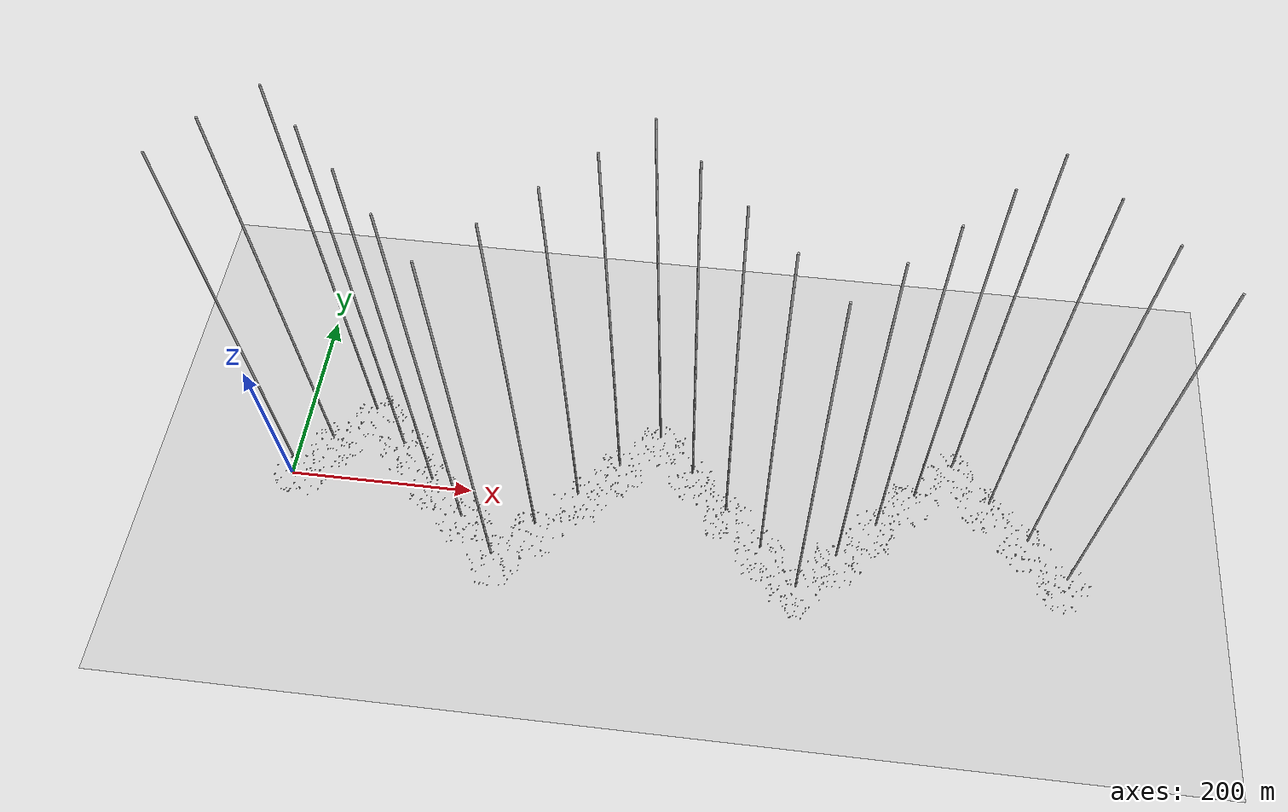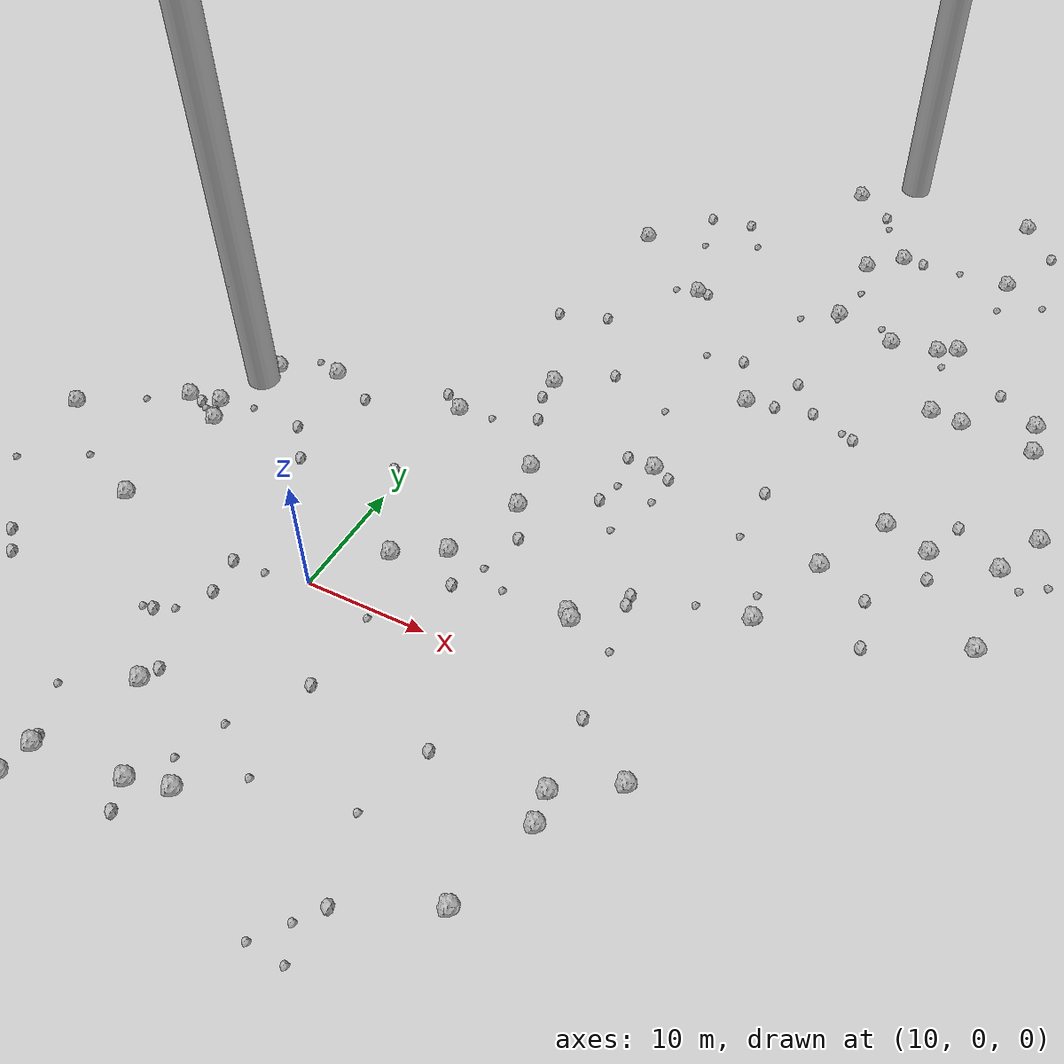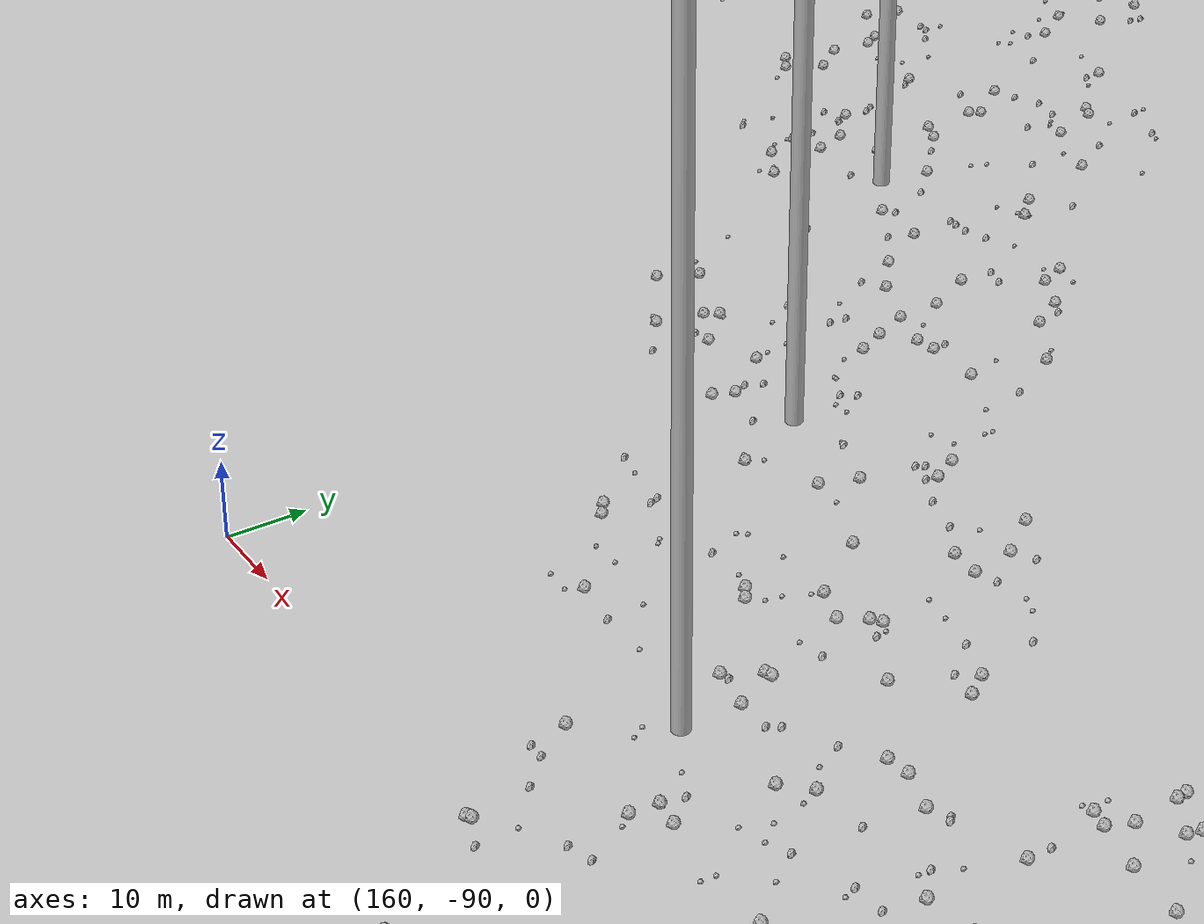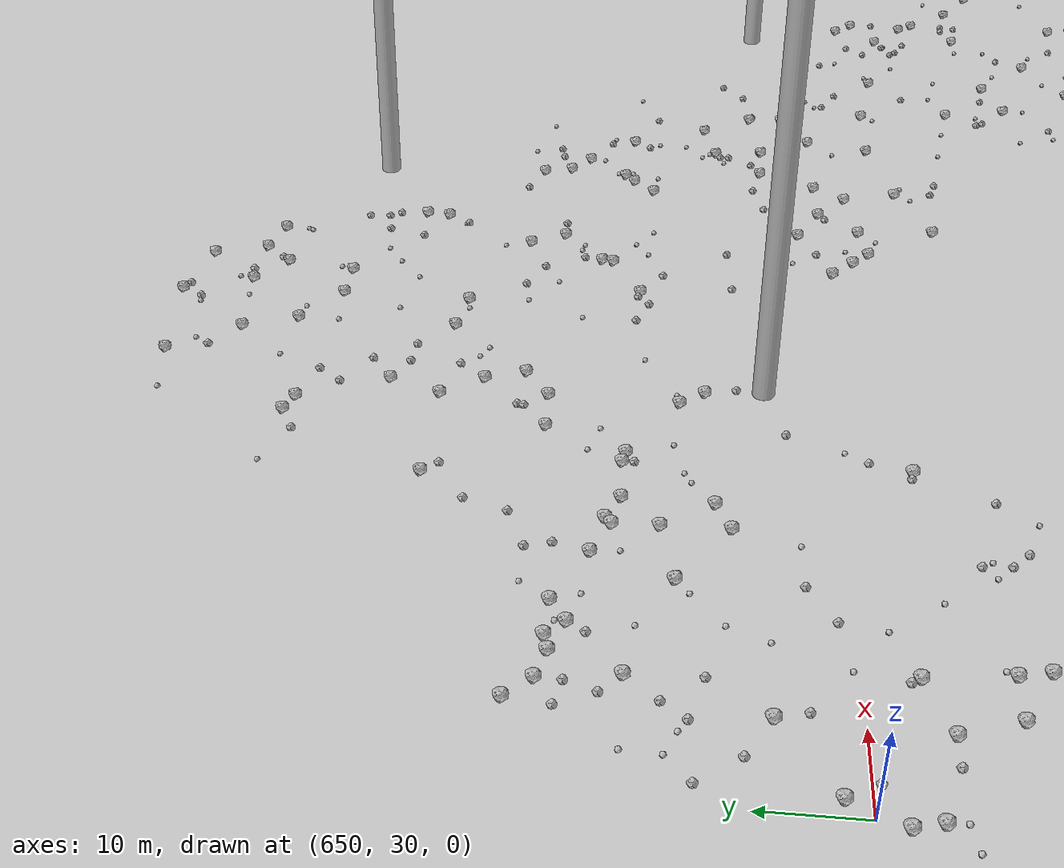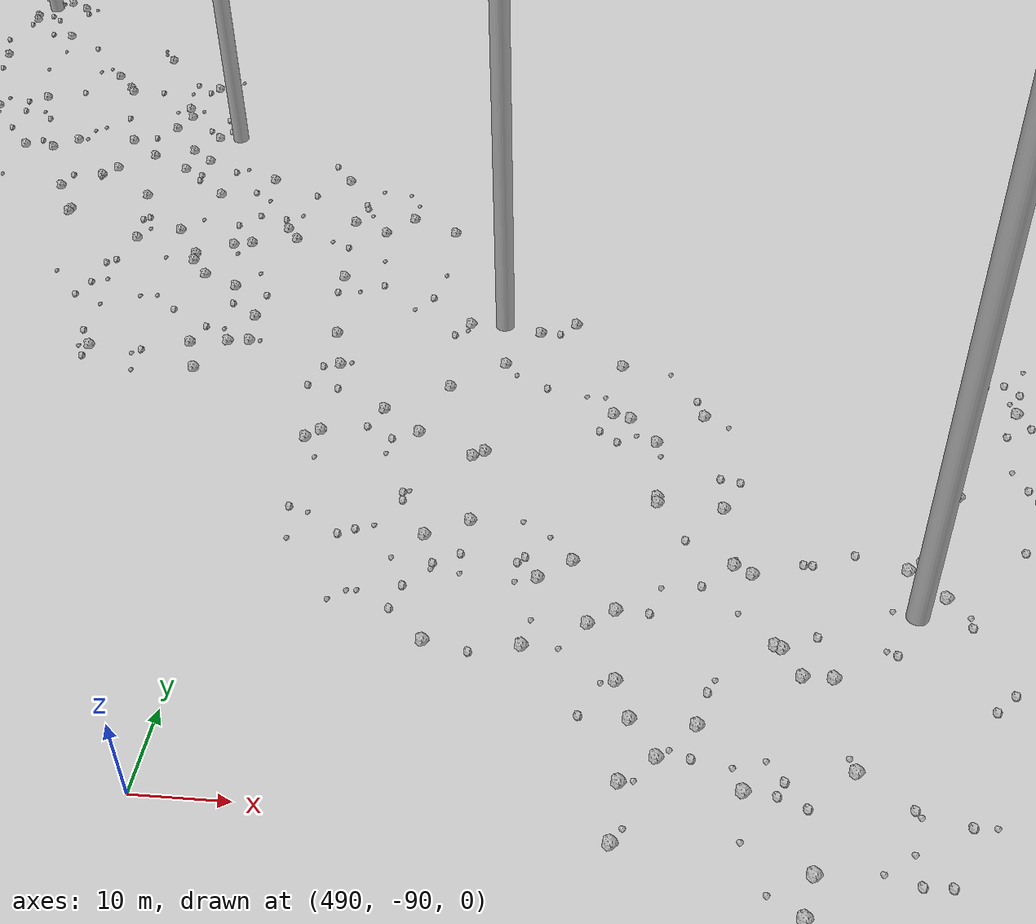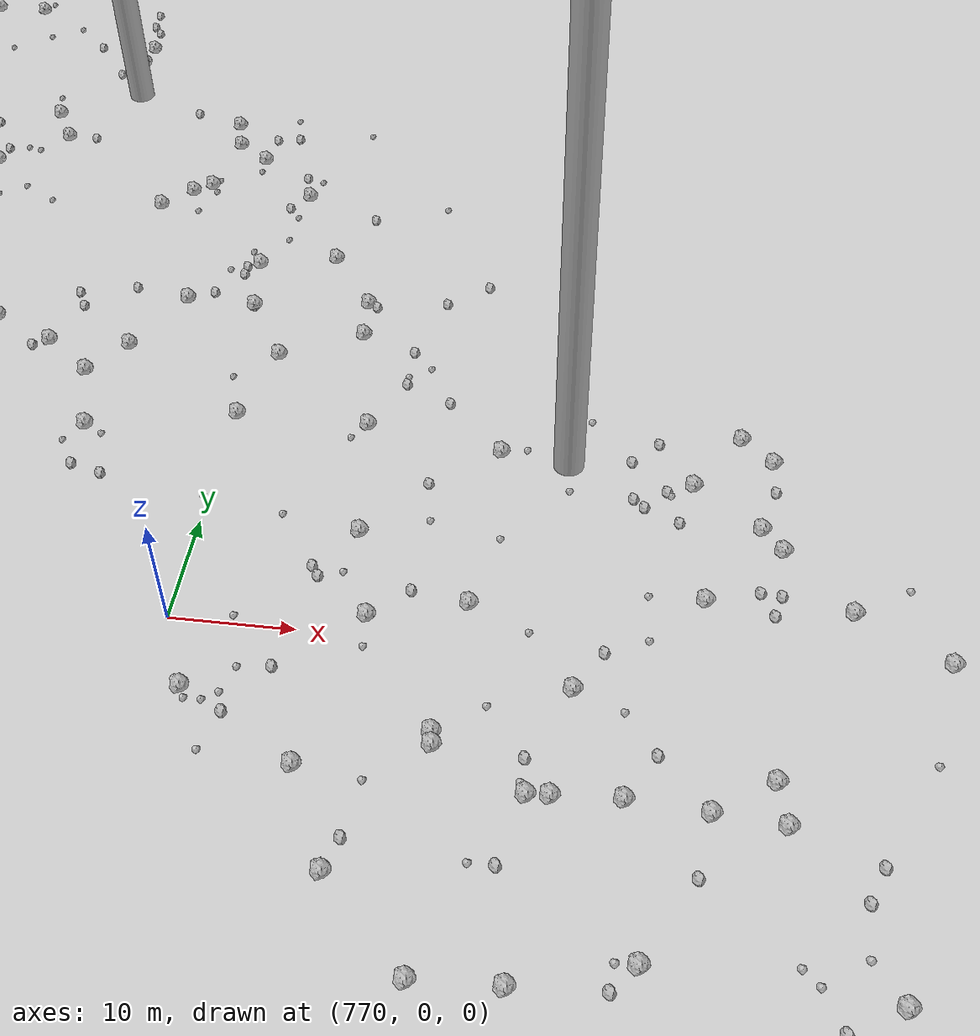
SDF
<sdf version="1.6">
 <world name="default">
  <include><uri>model://custom_ground</uri></include>
  <include><uri>model://sun</uri></include>
  <spherical_coordinates>
   <surface_model>EARTH_WGS84</surface_model>
   <latitude_deg>38.161479</latitude_deg>
   <longitude_deg>-122.454630</longitude_deg>
   <elevation>488.0</elevation>
   <heading_deg>90</heading_deg>
  </spherical_coordinates>
  <model name="rock1_0_0">
   <include><uri>model://rock1</uri><pose>-11.027764039563719 12.284014115505343 0.5 0 0 0</pose></include>
  </model>
  <model name="rock1_0_1">
   <include><uri>model://rock1</uri><pose>28.939537956805076 5.736446597086946 0.5 0 0 0</pose></include>
  </model>
  <model name="rock1_0_2">
   <include><uri>model://rock1</uri><pose>-1.5107407961260257 20.366758260181584 0.5 0 0 0</pose></include>
  </model>
  <model name="rock1_0_3">
   <include><uri>model://rock1</uri><pose>0.2570385839010747 -23.85550155937903 0.5 0 0 0</pose></include>
  </model>
  <model name="rock1_0_4">
   <include><uri>model://rock1</uri><pose>1.586014061621853 -23.04541576442167 0.5 0 0 0</pose></include>
  </model>
  <model name="rock1_0_5">
   <include><uri>model://rock1</uri><pose>-8.062970826868872 0.7424308620066782 0.5 0 0 0</pose></include>
  </model>
  <model name="rock1_0_6">
   <include><uri>model://rock1</uri><pose>13.891608856421989 5.073443191869288 0.5 0 0 0</pose></include>
  </model>
  <model name="rock1_0_7">
   <include><uri>model://rock1</uri><pose>2.0278214352170387 -20.346743775395076 0.5 0 0 0</pose></include>
  </model>
  <model name="rock1_0_8">
   <include><uri>model://rock1</uri><pose>38.588197003291874 -4.716279543927307 0.5 0 0 0</pose></include>
  </model>
  <model name="rock1_0_9">
   <include><uri>model://rock1</uri><pose>28.4831234992264 6.19119665853318 0.5 0 0 0</pose></include>
  </model>
  <model name="rock1_0_10">
   <include><uri>model://rock1</uri><pose>-14.068442878592693 -11.358586132357999 0.5 0 0 0</pose></include>
  </model>
  <model name="rock1_0_11">
   <include><uri>model://rock1</uri><pose>4.895437883553807 -12.873714850114805 0.5 0 0 0</pose></include>
  </model>
  <model name="rock1_0_12">
   <include><uri>model://rock1</uri><pose>-7.391547562215173 10.86112403371692 0.5 0 0 0</pose></include>
  </model>
  <model name="rock1_0_13">
   <include><uri>model://rock1</uri><pose>-19.40093982729339 -4.275042283149485 0.5 0 0 0</pose></include>
  </model>
  <model name="rock1_0_14">
   <include><uri>model://rock1</uri><pose>34.745237593558706 -10.069673632421463 0.5 0 0 0</pose></include>
  </model>
  <model name="rock1_0_15">
   <include><uri>model://rock1</uri><pose>10.15944948979963 21.32894314596298 0.5 0 0 0</pose></include>
  </model>
  <model name="rock1_0_16">
   <include><uri>model://rock1</uri><pose>9.331026613413734 -19.568326153727796 0.5 0 0 0</pose></include>
  </model>
  <model name="rock1_0_17">
   <include><uri>model://rock1</uri><pose>-8.274690872943726 12.860050784481224 0.5 0 0 0</pose></include>
  </model>
  <model name="rock1_0_18">
   <include><uri>model://rock1</uri><pose>17.632937537088516 7.346693989860569 0.5 0 0 0</pose></include>
  </model>
  <model name="rock1_0_19">
   <include><uri>model://rock1</uri><pose>12.554505665294208 -18.706540950473986 0.5 0 0 0</pose></include>
  </model>
  <model name="rock1_0_20">
   <include><uri>model://rock1</uri><pose>32.85350191048273 -17.44762869332425 0.5 0 0 0</pose></include>
  </model>
  <model name="rock1_0_21">
   <include><uri>model://rock1</uri><pose>18.788839518924974 18.110436376438862 0.5 0 0 0</pose></include>
  </model>
  <model name="rock1_0_22">
   <include><uri>model://rock1</uri><pose>-3.8858278749136304 -22.21808106653757 0.5 0 0 0</pose></include>
  </model>
  <model name="rock1_0_23">
   <include><uri>model://rock1</uri><pose>34.26534758210676 -7.543714053345834 0.5 0 0 0</pose></include>
  </model>
  <model name="rock1_0_24">
   <include><uri>model://rock1</uri><pose>-18.94947749458981 7.14842963456703 0.5 0 0 0</pose></include>
  </model>
  <model name="rock1_0_25">
   <include><uri>model://rock1</uri><pose>-6.4913171606933915 18.771355914047888 0.5 0 0 0</pose></include>
  </model>
  <model name="rock1_0_26">
   <include><uri>model://rock1</uri><pose>19.976429062862522 13.889876490020256 0.5 0 0 0</pose></include>
  </model>
  <model name="rock2_0_0">
   <include><uri>model://rock2</uri><pose>-11.63903249460002 -8.058631580797233 0.3 0 0 0</pose></include>
  </model>
  <model name="rock2_0_1">
   <include><uri>model://rock2</uri><pose>26.284740418298078 -20.804069318388834 0.3 0 0 0</pose></include>
  </model>
  <model name="rock2_0_2">
   <include><uri>model://rock2</uri><pose>19.61055265498777 4.568744306605829 0.3 0 0 0</pose></include>
  </model>
  <model name="rock2_0_3">
   <include><uri>model://rock2</uri><pose>25.33818112440329 17.43913012056167 0.3 0 0 0</pose></include>
  </model>
  <model name="rock2_0_4">
   <include><uri>model://rock2</uri><pose>2.449323907576993 18.68029120720989 0.3 0 0 0</pose></include>
  </model>
  <model name="rock2_0_5">
   <include><uri>model://rock2</uri><pose>-13.288587860979135 -6.361905748541496 0.3 0 0 0</pose></include>
  </model>
  <model name="rock2_0_6">
   <include><uri>model://rock2</uri><pose>8.351920678366273 22.51527897836027 0.3 0 0 0</pose></include>
  </model>
  <model name="rock2_0_7">
   <include><uri>model://rock2</uri><pose>-14.098320259304673 -14.89463491351524 0.3 0 0 0</pose></include>
  </model>
  <model name="rock2_0_8">
   <include><uri>model://rock2</uri><pose>31.785878052973445 9.83367118325826 0.3 0 0 0</pose></include>
  </model>
  <model name="rock2_0_9">
   <include><uri>model://rock2</uri><pose>4.370575834656371 -4.171433876113856 0.3 0 0 0</pose></include>
  </model>
  <model name="rock2_0_10">
   <include><uri>model://rock2</uri><pose>33.67975759322387 -1.407109420900671 0.3 0 0 0</pose></include>
  </model>
  <model name="rock2_0_11">
   <include><uri>model://rock2</uri><pose>21.712163400593596 10.89432187464 0.3 0 0 0</pose></include>
  </model>
  <model name="rock2_0_12">
   <include><uri>model://rock2</uri><pose>-0.6161595411897558 13.277080820130386 0.3 0 0 0</pose></include>
  </model>
  <model name="rock2_0_13">
   <include><uri>model://rock2</uri><pose>-16.02030685697866 -11.233019874052651 0.3 0 0 0</pose></include>
  </model>
  <model name="rock2_0_14">
   <include><uri>model://rock2</uri><pose>16.579087965963048 23.330777719990223 0.3 0 0 0</pose></include>
  </model>
  <model name="rock2_0_15">
   <include><uri>model://rock2</uri><pose>1.780808796740562 10.354297105642708 0.3 0 0 0</pose></include>
  </model>
  <model name="rock2_0_16">
   <include><uri>model://rock2</uri><pose>25.8109693475485 -8.493878163552672 0.3 0 0 0</pose></include>
  </model>
  <model name="rock2_0_17">
   <include><uri>model://rock2</uri><pose>9.210547826962387 12.78155190674105 0.3 0 0 0</pose></include>
  </model>
  <model name="rock2_0_18">
   <include><uri>model://rock2</uri><pose>10.167003569026363 -21.84647284312875 0.3 0 0 0</pose></include>
  </model>
  <model name="rock2_0_19">
   <include><uri>model://rock2</uri><pose>-9.685283023935751 12.105426964600298 0.3 0 0 0</pose></include>
  </model>
  <model name="rock2_0_20">
   <include><uri>model://rock2</uri><pose>3.8360450990637496 -1.0449101710525106 0.3 0 0 0</pose></include>
  </model>
  <model name="rock2_0_21">
   <include><uri>model://rock2</uri><pose>1.5150532432947088 -7.440881385105641 0.3 0 0 0</pose></include>
  </model>
  <model name="rock2_0_22">
   <include><uri>model://rock2</uri><pose>31.898649528236845 8.85688587566014 0.3 0 0 0</pose></include>
  </model>
  <model name="rock2_0_23">
   <include><uri>model://rock2</uri><pose>5.465736150114992 -11.508060313700554 0.3 0 0 0</pose></include>
  </model>
  <model name="rock2_0_24">
   <include><uri>model://rock2</uri><pose>15.717833623516668 -7.737938853698019 0.3 0 0 0</pose></include>
  </model>
  <model name="rock2_0_25">
   <include><uri>model://rock2</uri><pose>1.9358398595288726 -19.71800000034328 0.3 0 0 0</pose></include>
  </model>
  <model name="rock2_0_26">
   <include><uri>model://rock2</uri><pose>-2.054270555046152 -20.08413246740008 0.3 0 0 0</pose></include>
  </model>
  <model name="rock3_0_0">
   <include><uri>model://rock3</uri><pose>23.200025241243537 -24.910975696291654 0.2 0 0 0</pose></include>
  </model>
  <model name="rock3_0_1">
   <include><uri>model://rock3</uri><pose>11.056410516082465 -16.751649704671465 0.2 0 0 0</pose></include>
  </model>
  <model name="rock3_0_2">
   <include><uri>model://rock3</uri><pose>24.164926043356267 -14.557832058270426 0.2 0 0 0</pose></include>
  </model>
  <model name="rock3_0_3">
   <include><uri>model://rock3</uri><pose>12.365938836094259 -13.07369162155879 0.2 0 0 0</pose></include>
  </model>
  <model name="rock3_0_4">
   <include><uri>model://rock3</uri><pose>-0.05923128286390522 -15.756935803097889 0.2 0 0 0</pose></include>
  </model>
  <model name="rock3_0_5">
   <include><uri>model://rock3</uri><pose>32.68037519654864 4.502699760988804 0.2 0 0 0</pose></include>
  </model>
  <model name="rock3_0_6">
   <include><uri>model://rock3</uri><pose>-3.825713579086102 20.99950647799465 0.2 0 0 0</pose></include>
  </model>
  <model name="rock3_0_7">
   <include><uri>model://rock3</uri><pose>-14.151539511818758 10.235101651465442 0.2 0 0 0</pose></include>
  </model>
  <model name="rock3_0_8">
   <include><uri>model://rock3</uri><pose>20.853631124270485 7.1135003082286445 0.2 0 0 0</pose></include>
  </model>
  <model name="rock3_0_9">
   <include><uri>model://rock3</uri><pose>2.844878124975491 -6.678099283273799 0.2 0 0 0</pose></include>
  </model>
  <model name="rock3_0_10">
   <include><uri>model://rock3</uri><pose>-8.195287841889131 11.921336781768538 0.2 0 0 0</pose></include>
  </model>
  <model name="rock3_0_11">
   <include><uri>model://rock3</uri><pose>-7.785995474929695 -21.213525725990202 0.2 0 0 0</pose></include>
  </model>
  <model name="rock3_0_12">
   <include><uri>model://rock3</uri><pose>16.421818613718614 -15.72646589859537 0.2 0 0 0</pose></include>
  </model>
  <model name="rock3_0_13">
   <include><uri>model://rock3</uri><pose>-13.741673081180794 2.778088905468614 0.2 0 0 0</pose></include>
  </model>
  <model name="rock3_0_14">
   <include><uri>model://rock3</uri><pose>13.032524777201019 21.710868922137095 0.2 0 0 0</pose></include>
  </model>
  <model name="rock3_0_15">
   <include><uri>model://rock3</uri><pose>4.708462276070787 -12.600812759024674 0.2 0 0 0</pose></include>
  </model>
  <model name="rock3_0_16">
   <include><uri>model://rock3</uri><pose>23.14323596932821 5.874132451418582 0.2 0 0 0</pose></include>
  </model>
  <model name="rock3_0_17">
   <include><uri>model://rock3</uri><pose>-18.867238156881033 -0.16949232043270257 0.2 0 0 0</pose></include>
  </model>
  <model name="rock3_0_18">
   <include><uri>model://rock3</uri><pose>6.536064618410343 -0.8669301132803788 0.2 0 0 0</pose></include>
  </model>
  <model name="rock3_0_19">
   <include><uri>model://rock3</uri><pose>27.47742817390902 15.001201233086505 0.2 0 0 0</pose></include>
  </model>
  <model name="rock3_0_20">
   <include><uri>model://rock3</uri><pose>15.743139515950432 -0.942880011137742 0.2 0 0 0</pose></include>
  </model>
  <model name="rock3_0_21">
   <include><uri>model://rock3</uri><pose>24.918717175076978 -22.643668521874297 0.2 0 0 0</pose></include>
  </model>
  <model name="rock3_0_22">
   <include><uri>model://rock3</uri><pose>0.5685027084493086 -7.582909859739349 0.2 0 0 0</pose></include>
  </model>
  <model name="rock3_0_23">
   <include><uri>model://rock3</uri><pose>-8.9837895550506 11.64670463130684 0.2 0 0 0</pose></include>
  </model>
  <model name="rock3_0_24">
   <include><uri>model://rock3</uri><pose>-5.364373334694285 13.492634227869857 0.2 0 0 0</pose></include>
  </model>
  <model name="rock3_0_25">
   <include><uri>model://rock3</uri><pose>-13.691411601637336 -17.30010163864805 0.2 0 0 0</pose></include>
  </model>
  <model name="rock3_0_26">
   <include><uri>model://rock3</uri><pose>26.128649408401316 -25.04861598051007 0.2 0 0 0</pose></include>
  </model>
  <model name="rock1_1_0">
   <include><uri>model://rock1</uri><pose>47.93787149752842 39.15694850924403 0.5 0 0 0</pose></include>
  </model>
  <model name="rock1_1_1">
   <include><uri>model://rock1</uri><pose>29.463599092789366 67.31664059988562 0.5 0 0 0</pose></include>
  </model>
  <model name="rock1_1_2">
   <include><uri>model://rock1</uri><pose>44.963845256392005 48.220956951883096 0.5 0 0 0</pose></include>
  </model>
  <model name="rock1_1_3">
   <include><uri>model://rock1</uri><pose>55.641910495680364 16.661459743873724 0.5 0 0 0</pose></include>
  </model>
  <model name="rock1_1_4">
   <include><uri>model://rock1</uri><pose>36.53212439782863 59.00728522651723 0.5 0 0 0</pose></include>
  </model>
  <model name="rock1_1_5">
   <include><uri>model://rock1</uri><pose>55.14332537995043 24.81326238445375 0.5 0 0 0</pose></include>
  </model>
  <model name="rock1_1_6">
   <include><uri>model://rock1</uri><pose>21.319362941576046 45.31602036002703 0.5 0 0 0</pose></include>
  </model>
  <model name="rock1_1_7">
   <include><uri>model://rock1</uri><pose>27.636589750142438 22.582038185657396 0.5 0 0 0</pose></include>
  </model>
  <model name="rock1_1_8">
   <include><uri>model://rock1</uri><pose>40.55650955947914 11.920269110340193 0.5 0 0 0</pose></include>
  </model>
  <model name="rock1_1_9">
   <include><uri>model://rock1</uri><pose>55.93763435428642 44.806850994092414 0.5 0 0 0</pose></include>
  </model>
  <model name="rock1_1_10">
   <include><uri>model://rock1</uri><pose>43.0431048754412 18.960192602179024 0.5 0 0 0</pose></include>
  </model>
  <model name="rock1_1_11">
   <include><uri>model://rock1</uri><pose>33.831597847898536 56.28438614489316 0.5 0 0 0</pose></include>
  </model>
  <model name="rock1_1_12">
   <include><uri>model://rock1</uri><pose>54.13351601728975 38.48962958496904 0.5 0 0 0</pose></include>
  </model>
  <model name="rock1_1_13">
   <include><uri>model://rock1</uri><pose>31.06711539045206 33.447068193984364 0.5 0 0 0</pose></include>
  </model>
  <model name="rock1_1_14">
   <include><uri>model://rock1</uri><pose>46.31024835359884 59.475555129943025 0.5 0 0 0</pose></include>
  </model>
  <model name="rock1_1_15">
   <include><uri>model://rock1</uri><pose>53.54373605038541 41.60864477045743 0.5 0 0 0</pose></include>
  </model>
  <model name="rock1_1_16">
   <include><uri>model://rock1</uri><pose>15.520972790458952 28.09509066593683 0.5 0 0 0</pose></include>
  </model>
  <model name="rock1_1_17">
   <include><uri>model://rock1</uri><pose>46.12366546528277 25.253262000078184 0.5 0 0 0</pose></include>
  </model>
  <model name="rock1_1_18">
   <include><uri>model://rock1</uri><pose>43.41834254989864 47.288727963671136 0.5 0 0 0</pose></include>
  </model>
  <model name="rock1_1_19">
   <include><uri>model://rock1</uri><pose>60.58387675062642 27.852648122627205 0.5 0 0 0</pose></include>
  </model>
  <model name="rock1_1_20">
   <include><uri>model://rock1</uri><pose>45.65729797237813 69.38236852599675 0.5 0 0 0</pose></include>
  </model>
  <model name="rock1_1_21">
   <include><uri>model://rock1</uri><pose>49.89536697905866 24.010073545396594 0.5 0 0 0</pose></include>
  </model>
  <model name="rock1_1_22">
   <include><uri>model://rock1</uri><pose>39.438220172087675 46.51247677554031 0.5 0 0 0</pose></include>
  </model>
  <model name="rock1_1_23">
   <include><uri>model://rock1</uri><pose>45.29643320209466 39.40501971165099 0.5 0 0 0</pose></include>
  </model>
  <model name="rock1_1_24">
   <include><uri>model://rock1</uri><pose>13.511565687798644 51.04736807479747 0.5 0 0 0</pose></include>
  </model>
  <model name="rock1_1_25">
   <include><uri>model://rock1</uri><pose>34.01784801669322 48.15724955767447 0.5 0 0 0</pose></include>
  </model>
  <model name="rock1_1_26">
   <include><uri>model://rock1</uri><pose>57.01384284971979 29.090483529163723 0.5 0 0 0</pose></include>
  </model>
  <model name="rock2_1_0">
   <include><uri>model://rock2</uri><pose>25.258110569597697 22.75584588351117 0.3 0 0 0</pose></include>
  </model>
  <model name="rock2_1_1">
   <include><uri>model://rock2</uri><pose>69.5261759175434 36.10233627948918 0.3 0 0 0</pose></include>
  </model>
  <model name="rock2_1_2">
   <include><uri>model://rock2</uri><pose>22.303669893945454 45.423347689046054 0.3 0 0 0</pose></include>
  </model>
  <model name="rock2_1_3">
   <include><uri>model://rock2</uri><pose>57.257450536101025 38.77369353720558 0.3 0 0 0</pose></include>
  </model>
  <model name="rock2_1_4">
   <include><uri>model://rock2</uri><pose>48.34711857606229 13.067781005718492 0.3 0 0 0</pose></include>
  </model>
  <model name="rock2_1_5">
   <include><uri>model://rock2</uri><pose>51.18774802209775 27.580022293260953 0.3 0 0 0</pose></include>
  </model>
  <model name="rock2_1_6">
   <include><uri>model://rock2</uri><pose>28.913837425434114 38.118213481438815 0.3 0 0 0</pose></include>
  </model>
  <model name="rock2_1_7">
   <include><uri>model://rock2</uri><pose>32.95427605384201 64.79696000343681 0.3 0 0 0</pose></include>
  </model>
  <model name="rock2_1_8">
   <include><uri>model://rock2</uri><pose>29.185867435574043 21.991814900947766 0.3 0 0 0</pose></include>
  </model>
  <model name="rock2_1_9">
   <include><uri>model://rock2</uri><pose>67.50872051332395 33.714179035054336 0.3 0 0 0</pose></include>
  </model>
  <model name="rock2_1_10">
   <include><uri>model://rock2</uri><pose>15.58320913487265 25.936797954493137 0.3 0 0 0</pose></include>
  </model>
  <model name="rock2_1_11">
   <include><uri>model://rock2</uri><pose>19.842403994561625 31.25489734576512 0.3 0 0 0</pose></include>
  </model>
  <model name="rock2_1_12">
   <include><uri>model://rock2</uri><pose>49.93820372359043 44.16185005638058 0.3 0 0 0</pose></include>
  </model>
  <model name="rock2_1_13">
   <include><uri>model://rock2</uri><pose>50.59787757992681 21.47030822657274 0.3 0 0 0</pose></include>
  </model>
  <model name="rock2_1_14">
   <include><uri>model://rock2</uri><pose>54.00122508399077 38.57842821367872 0.3 0 0 0</pose></include>
  </model>
  <model name="rock2_1_15">
   <include><uri>model://rock2</uri><pose>40.641452011348264 33.12287367708445 0.3 0 0 0</pose></include>
  </model>
  <model name="rock2_1_16">
   <include><uri>model://rock2</uri><pose>47.20136200737882 17.329708789903883 0.3 0 0 0</pose></include>
  </model>
  <model name="rock2_1_17">
   <include><uri>model://rock2</uri><pose>36.568313230994825 24.16808130758624 0.3 0 0 0</pose></include>
  </model>
  <model name="rock2_1_18">
   <include><uri>model://rock2</uri><pose>11.539747561010191 36.59810670271962 0.3 0 0 0</pose></include>
  </model>
  <model name="rock2_1_19">
   <include><uri>model://rock2</uri><pose>33.48934479843195 33.89581869194538 0.3 0 0 0</pose></include>
  </model>
  <model name="rock2_1_20">
   <include><uri>model://rock2</uri><pose>15.711501392461273 38.006385453309974 0.3 0 0 0</pose></include>
  </model>
  <model name="rock2_1_21">
   <include><uri>model://rock2</uri><pose>38.42932044724726 59.12089979091903 0.3 0 0 0</pose></include>
  </model>
  <model name="rock2_1_22">
   <include><uri>model://rock2</uri><pose>21.63282353034208 57.441179285760825 0.3 0 0 0</pose></include>
  </model>
  <model name="rock2_1_23">
   <include><uri>model://rock2</uri><pose>36.64222030399797 34.62326656863516 0.3 0 0 0</pose></include>
  </model>
  <model name="rock2_1_24">
   <include><uri>model://rock2</uri><pose>34.188754807912744 37.55654810460783 0.3 0 0 0</pose></include>
  </model>
  <model name="rock2_1_25">
   <include><uri>model://rock2</uri><pose>17.868141154190553 56.730525324639025 0.3 0 0 0</pose></include>
  </model>
  <model name="rock2_1_26">
   <include><uri>model://rock2</uri><pose>48.93759744684688 65.52124544408031 0.3 0 0 0</pose></include>
  </model>
  <model name="rock3_1_0">
   <include><uri>model://rock3</uri><pose>18.89273699439014 52.42946370447703 0.2 0 0 0</pose></include>
  </model>
  <model name="rock3_1_1">
   <include><uri>model://rock3</uri><pose>58.77132447909009 24.806737465584227 0.2 0 0 0</pose></include>
  </model>
  <model name="rock3_1_2">
   <include><uri>model://rock3</uri><pose>67.47929482684297 44.25461767449642 0.2 0 0 0</pose></include>
  </model>
  <model name="rock3_1_3">
   <include><uri>model://rock3</uri><pose>34.07413068790483 47.60828752137151 0.2 0 0 0</pose></include>
  </model>
  <model name="rock3_1_4">
   <include><uri>model://rock3</uri><pose>50.02533197129935 57.71009327729891 0.2 0 0 0</pose></include>
  </model>
  <model name="rock3_1_5">
   <include><uri>model://rock3</uri><pose>25.839389063063773 19.518648333850464 0.2 0 0 0</pose></include>
  </model>
  <model name="rock3_1_6">
   <include><uri>model://rock3</uri><pose>53.482437643413625 42.710312555992665 0.2 0 0 0</pose></include>
  </model>
  <model name="rock3_1_7">
   <include><uri>model://rock3</uri><pose>33.65958367735742 63.230224582519874 0.2 0 0 0</pose></include>
  </model>
  <model name="rock3_1_8">
   <include><uri>model://rock3</uri><pose>25.610471405739432 37.540935897446744 0.2 0 0 0</pose></include>
  </model>
  <model name="rock3_1_9">
   <include><uri>model://rock3</uri><pose>19.310155670445276 44.89422649089674 0.2 0 0 0</pose></include>
  </model>
  <model name="rock3_1_10">
   <include><uri>model://rock3</uri><pose>36.55797750215512 19.00890173331014 0.2 0 0 0</pose></include>
  </model>
  <model name="rock3_1_11">
   <include><uri>model://rock3</uri><pose>25.473641898174062 29.23245182409636 0.2 0 0 0</pose></include>
  </model>
  <model name="rock3_1_12">
   <include><uri>model://rock3</uri><pose>23.43957888042477 54.54817778250699 0.2 0 0 0</pose></include>
  </model>
  <model name="rock3_1_13">
   <include><uri>model://rock3</uri><pose>56.921669623892434 23.51310733546935 0.2 0 0 0</pose></include>
  </model>
  <model name="rock3_1_14">
   <include><uri>model://rock3</uri><pose>62.97350601367094 28.818550887149023 0.2 0 0 0</pose></include>
  </model>
  <model name="rock3_1_15">
   <include><uri>model://rock3</uri><pose>39.555729465102914 33.52997754728622 0.2 0 0 0</pose></include>
  </model>
  <model name="rock3_1_16">
   <include><uri>model://rock3</uri><pose>38.03956455908339 48.14266576496267 0.2 0 0 0</pose></include>
  </model>
  <model name="rock3_1_17">
   <include><uri>model://rock3</uri><pose>29.000908241189762 19.1518611599833 0.2 0 0 0</pose></include>
  </model>
  <model name="rock3_1_18">
   <include><uri>model://rock3</uri><pose>39.99002272585656 14.168349255086678 0.2 0 0 0</pose></include>
  </model>
  <model name="rock3_1_19">
   <include><uri>model://rock3</uri><pose>46.43400577829699 55.54908671136731 0.2 0 0 0</pose></include>
  </model>
  <model name="rock3_1_20">
   <include><uri>model://rock3</uri><pose>41.869248602641946 59.400118952803055 0.2 0 0 0</pose></include>
  </model>
  <model name="rock3_1_21">
   <include><uri>model://rock3</uri><pose>36.35287174130217 11.219924408400718 0.2 0 0 0</pose></include>
  </model>
  <model name="rock3_1_22">
   <include><uri>model://rock3</uri><pose>34.659913664878644 52.23854414428511 0.2 0 0 0</pose></include>
  </model>
  <model name="rock3_1_23">
   <include><uri>model://rock3</uri><pose>44.315773741187876 45.56714831733537 0.2 0 0 0</pose></include>
  </model>
  <model name="rock3_1_24">
   <include><uri>model://rock3</uri><pose>60.255324847436256 44.273608195626494 0.2 0 0 0</pose></include>
  </model>
  <model name="rock3_1_25">
   <include><uri>model://rock3</uri><pose>31.043153625356023 46.18699480506264 0.2 0 0 0</pose></include>
  </model>
  <model name="rock3_1_26">
   <include><uri>model://rock3</uri><pose>60.93547802875774 51.34879760240223 0.2 0 0 0</pose></include>
  </model>
  <model name="rock1_2_0">
   <include><uri>model://rock1</uri><pose>65.10959780317407 85.64944737781002 0.5 0 0 0</pose></include>
  </model>
  <model name="rock1_2_1">
   <include><uri>model://rock1</uri><pose>60.437116150663336 70.0969715827402 0.5 0 0 0</pose></include>
  </model>
  <model name="rock1_2_2">
   <include><uri>model://rock1</uri><pose>89.30199497735592 77.25948061841048 0.5 0 0 0</pose></include>
  </model>
  <model name="rock1_2_3">
   <include><uri>model://rock1</uri><pose>66.89887861103752 91.449484165959 0.5 0 0 0</pose></include>
  </model>
  <model name="rock1_2_4">
   <include><uri>model://rock1</uri><pose>106.0374139106263 78.75601172982115 0.5 0 0 0</pose></include>
  </model>
  <model name="rock1_2_5">
   <include><uri>model://rock1</uri><pose>57.07714215069618 89.84547747229956 0.5 0 0 0</pose></include>
  </model>
  <model name="rock1_2_6">
   <include><uri>model://rock1</uri><pose>82.77211672784051 107.135291491609 0.5 0 0 0</pose></include>
  </model>
  <model name="rock1_2_7">
   <include><uri>model://rock1</uri><pose>101.41127250129199 74.5553821500523 0.5 0 0 0</pose></include>
  </model>
  <model name="rock1_2_8">
   <include><uri>model://rock1</uri><pose>96.47506714035283 98.07325984906326 0.5 0 0 0</pose></include>
  </model>
  <model name="rock1_2_9">
   <include><uri>model://rock1</uri><pose>59.45677492497249 62.76796165297408 0.5 0 0 0</pose></include>
  </model>
  <model name="rock1_2_10">
   <include><uri>model://rock1</uri><pose>86.19428930081054 108.81991641873663 0.5 0 0 0</pose></include>
  </model>
  <model name="rock1_2_11">
   <include><uri>model://rock1</uri><pose>104.49369682838432 86.42843351925472 0.5 0 0 0</pose></include>
  </model>
  <model name="rock1_2_12">
   <include><uri>model://rock1</uri><pose>105.00655641848411 69.31671601331965 0.5 0 0 0</pose></include>
  </model>
  <model name="rock1_2_13">
   <include><uri>model://rock1</uri><pose>80.14278459088538 96.63378002967241 0.5 0 0 0</pose></include>
  </model>
  <model name="rock1_2_14">
   <include><uri>model://rock1</uri><pose>66.50747413455223 55.82103978167909 0.5 0 0 0</pose></include>
  </model>
  <model name="rock1_2_15">
   <include><uri>model://rock1</uri><pose>58.2347544736688 64.0519644227429 0.5 0 0 0</pose></include>
  </model>
  <model name="rock1_2_16">
   <include><uri>model://rock1</uri><pose>75.90891554772467 99.02768621188693 0.5 0 0 0</pose></include>
  </model>
  <model name="rock1_2_17">
   <include><uri>model://rock1</uri><pose>54.47034581645066 89.79363469966289 0.5 0 0 0</pose></include>
  </model>
  <model name="rock1_2_18">
   <include><uri>model://rock1</uri><pose>87.40631627382018 55.349681240621564 0.5 0 0 0</pose></include>
  </model>
  <model name="rock1_2_19">
   <include><uri>model://rock1</uri><pose>70.9416720880153 72.28781266419392 0.5 0 0 0</pose></include>
  </model>
  <model name="rock1_2_20">
   <include><uri>model://rock1</uri><pose>86.05099744823761 50.73171562472149 0.5 0 0 0</pose></include>
  </model>
  <model name="rock1_2_21">
   <include><uri>model://rock1</uri><pose>85.09986219245889 98.01514237065379 0.5 0 0 0</pose></include>
  </model>
  <model name="rock1_2_22">
   <include><uri>model://rock1</uri><pose>81.20256831741864 106.05892328374539 0.5 0 0 0</pose></include>
  </model>
  <model name="rock1_2_23">
   <include><uri>model://rock1</uri><pose>87.35525904989981 98.83689669439744 0.5 0 0 0</pose></include>
  </model>
  <model name="rock1_2_24">
   <include><uri>model://rock1</uri><pose>74.40284487423165 69.10999913890848 0.5 0 0 0</pose></include>
  </model>
  <model name="rock1_2_25">
   <include><uri>model://rock1</uri><pose>82.92790051771905 81.36813609783735 0.5 0 0 0</pose></include>
  </model>
  <model name="rock1_2_26">
   <include><uri>model://rock1</uri><pose>88.15775423884637 104.1222702000239 0.5 0 0 0</pose></include>
  </model>
  <model name="rock2_2_0">
   <include><uri>model://rock2</uri><pose>65.87685847400157 78.72357481007276 0.3 0 0 0</pose></include>
  </model>
  <model name="rock2_2_1">
   <include><uri>model://rock2</uri><pose>56.7028687374927 95.14443197399244 0.3 0 0 0</pose></include>
  </model>
  <model name="rock2_2_2">
   <include><uri>model://rock2</uri><pose>87.17044136254941 103.58997278341815 0.3 0 0 0</pose></include>
  </model>
  <model name="rock2_2_3">
   <include><uri>model://rock2</uri><pose>88.22159224335395 101.41388524858604 0.3 0 0 0</pose></include>
  </model>
  <model name="rock2_2_4">
   <include><uri>model://rock2</uri><pose>93.16838155857467 55.4240378763768 0.3 0 0 0</pose></include>
  </model>
  <model name="rock2_2_5">
   <include><uri>model://rock2</uri><pose>81.11073699388544 95.97563125585935 0.3 0 0 0</pose></include>
  </model>
  <model name="rock2_2_6">
   <include><uri>model://rock2</uri><pose>66.91168413147719 99.76579991816456 0.3 0 0 0</pose></include>
  </model>
  <model name="rock2_2_7">
   <include><uri>model://rock2</uri><pose>58.92039971546052 71.89032207188927 0.3 0 0 0</pose></include>
  </model>
  <model name="rock2_2_8">
   <include><uri>model://rock2</uri><pose>76.90818331857074 57.128283852088884 0.3 0 0 0</pose></include>
  </model>
  <model name="rock2_2_9">
   <include><uri>model://rock2</uri><pose>90.96356815993023 75.2772883163035 0.3 0 0 0</pose></include>
  </model>
  <model name="rock2_2_10">
   <include><uri>model://rock2</uri><pose>56.54758992135773 84.35597097345347 0.3 0 0 0</pose></include>
  </model>
  <model name="rock2_2_11">
   <include><uri>model://rock2</uri><pose>75.49966027284802 67.51446411868758 0.3 0 0 0</pose></include>
  </model>
  <model name="rock2_2_12">
   <include><uri>model://rock2</uri><pose>85.2340835584254 55.863322759997295 0.3 0 0 0</pose></include>
  </model>
  <model name="rock2_2_13">
   <include><uri>model://rock2</uri><pose>52.33911123864366 70.47669952404195 0.3 0 0 0</pose></include>
  </model>
  <model name="rock2_2_14">
   <include><uri>model://rock2</uri><pose>99.62088776690516 83.80383133460069 0.3 0 0 0</pose></include>
  </model>
  <model name="rock2_2_15">
   <include><uri>model://rock2</uri><pose>94.6528058594688 55.3128822297061 0.3 0 0 0</pose></include>
  </model>
  <model name="rock2_2_16">
   <include><uri>model://rock2</uri><pose>108.39080271841158 84.4484430924571 0.3 0 0 0</pose></include>
  </model>
  <model name="rock2_2_17">
   <include><uri>model://rock2</uri><pose>89.11549519881385 100.22627670357267 0.3 0 0 0</pose></include>
  </model>
  <model name="rock2_2_18">
   <include><uri>model://rock2</uri><pose>104.2201926958722 66.79412783304934 0.3 0 0 0</pose></include>
  </model>
  <model name="rock2_2_19">
   <include><uri>model://rock2</uri><pose>74.74072258891691 85.67649245331057 0.3 0 0 0</pose></include>
  </model>
  <model name="rock2_2_20">
   <include><uri>model://rock2</uri><pose>52.15951249782736 82.2899142447537 0.3 0 0 0</pose></include>
  </model>
  <model name="rock2_2_21">
   <include><uri>model://rock2</uri><pose>52.394084244249946 79.40338382139126 0.3 0 0 0</pose></include>
  </model>
  <model name="rock2_2_22">
   <include><uri>model://rock2</uri><pose>101.52889426701097 93.03857574879531 0.3 0 0 0</pose></include>
  </model>
  <model name="rock2_2_23">
   <include><uri>model://rock2</uri><pose>77.27606003235177 66.05823240872354 0.3 0 0 0</pose></include>
  </model>
  <model name="rock2_2_24">
   <include><uri>model://rock2</uri><pose>84.92944536952928 87.98165475549956 0.3 0 0 0</pose></include>
  </model>
  <model name="rock2_2_25">
   <include><uri>model://rock2</uri><pose>108.08423003515023 82.79223874945279 0.3 0 0 0</pose></include>
  </model>
  <model name="rock2_2_26">
   <include><uri>model://rock2</uri><pose>62.40564309504918 72.32384031889482 0.3 0 0 0</pose></include>
  </model>
  <model name="rock3_2_0">
   <include><uri>model://rock3</uri><pose>70.53250366535713 57.67990670852657 0.2 0 0 0</pose></include>
  </model>
  <model name="rock3_2_1">
   <include><uri>model://rock3</uri><pose>94.4112975488417 58.03093435888964 0.2 0 0 0</pose></include>
  </model>
  <model name="rock3_2_2">
   <include><uri>model://rock3</uri><pose>94.05598639774821 95.19381075463608 0.2 0 0 0</pose></include>
  </model>
  <model name="rock3_2_3">
   <include><uri>model://rock3</uri><pose>101.68294604808807 89.58616837301486 0.2 0 0 0</pose></include>
  </model>
  <model name="rock3_2_4">
   <include><uri>model://rock3</uri><pose>86.52905939206454 71.50226411913852 0.2 0 0 0</pose></include>
  </model>
  <model name="rock3_2_5">
   <include><uri>model://rock3</uri><pose>96.84057969296839 85.34005167656413 0.2 0 0 0</pose></include>
  </model>
  <model name="rock3_2_6">
   <include><uri>model://rock3</uri><pose>83.5134226412101 102.09879655089269 0.2 0 0 0</pose></include>
  </model>
  <model name="rock3_2_7">
   <include><uri>model://rock3</uri><pose>80.84478185348704 102.60738582537462 0.2 0 0 0</pose></include>
  </model>
  <model name="rock3_2_8">
   <include><uri>model://rock3</uri><pose>88.17074591891961 88.59750558275928 0.2 0 0 0</pose></include>
  </model>
  <model name="rock3_2_9">
   <include><uri>model://rock3</uri><pose>104.57897235503046 63.24355014813025 0.2 0 0 0</pose></include>
  </model>
  <model name="rock3_2_10">
   <include><uri>model://rock3</uri><pose>59.331554385947584 83.78629534349956 0.2 0 0 0</pose></include>
  </model>
  <model name="rock3_2_11">
   <include><uri>model://rock3</uri><pose>68.7876192801186 53.965332759787266 0.2 0 0 0</pose></include>
  </model>
  <model name="rock3_2_12">
   <include><uri>model://rock3</uri><pose>100.38163122996747 71.71028850787303 0.2 0 0 0</pose></include>
  </model>
  <model name="rock3_2_13">
   <include><uri>model://rock3</uri><pose>58.1332787713245 81.8363607610967 0.2 0 0 0</pose></include>
  </model>
  <model name="rock3_2_14">
   <include><uri>model://rock3</uri><pose>53.49726857569454 68.31964093093906 0.2 0 0 0</pose></include>
  </model>
  <model name="rock3_2_15">
   <include><uri>model://rock3</uri><pose>100.42499724439776 76.06270273358142 0.2 0 0 0</pose></include>
  </model>
  <model name="rock3_2_16">
   <include><uri>model://rock3</uri><pose>86.52320405981698 102.48666625140834 0.2 0 0 0</pose></include>
  </model>
  <model name="rock3_2_17">
   <include><uri>model://rock3</uri><pose>79.73639898391033 107.08737927104966 0.2 0 0 0</pose></include>
  </model>
  <model name="rock3_2_18">
   <include><uri>model://rock3</uri><pose>101.72707175963032 65.84352037625297 0.2 0 0 0</pose></include>
  </model>
  <model name="rock3_2_19">
   <include><uri>model://rock3</uri><pose>72.81656236352761 62.49729534194474 0.2 0 0 0</pose></include>
  </model>
  <model name="rock3_2_20">
   <include><uri>model://rock3</uri><pose>103.6196258238628 61.792107163469396 0.2 0 0 0</pose></include>
  </model>
  <model name="rock3_2_21">
   <include><uri>model://rock3</uri><pose>103.34743514484782 86.61519280173343 0.2 0 0 0</pose></include>
  </model>
  <model name="rock3_2_22">
   <include><uri>model://rock3</uri><pose>60.60511208795933 68.18969725376361 0.2 0 0 0</pose></include>
  </model>
  <model name="rock3_2_23">
   <include><uri>model://rock3</uri><pose>57.75530543137944 94.79401232593386 0.2 0 0 0</pose></include>
  </model>
  <model name="rock3_2_24">
   <include><uri>model://rock3</uri><pose>80.63143150301363 99.51044257007473 0.2 0 0 0</pose></include>
  </model>
  <model name="rock3_2_25">
   <include><uri>model://rock3</uri><pose>55.79638239526985 81.2120417845307 0.2 0 0 0</pose></include>
  </model>
  <model name="rock3_2_26">
   <include><uri>model://rock3</uri><pose>95.85741489643087 76.4217936048879 0.2 0 0 0</pose></include>
  </model>
  <model name="rock1_3_0">
   <include><uri>model://rock1</uri><pose>116.28537620473503 51.53825608023416 0.5 0 0 0</pose></include>
  </model>
  <model name="rock1_3_1">
   <include><uri>model://rock1</uri><pose>91.60230635178841 32.498898438345265 0.5 0 0 0</pose></include>
  </model>
  <model name="rock1_3_2">
   <include><uri>model://rock1</uri><pose>117.66691400058004 20.71639104216043 0.5 0 0 0</pose></include>
  </model>
  <model name="rock1_3_3">
   <include><uri>model://rock1</uri><pose>131.03947576628494 29.018959666890684 0.5 0 0 0</pose></include>
  </model>
  <model name="rock1_3_4">
   <include><uri>model://rock1</uri><pose>92.65327758507308 47.49993025746714 0.5 0 0 0</pose></include>
  </model>
  <model name="rock1_3_5">
   <include><uri>model://rock1</uri><pose>131.5342156255245 51.5094979347317 0.5 0 0 0</pose></include>
  </model>
  <model name="rock1_3_6">
   <include><uri>model://rock1</uri><pose>93.90093363901543 45.41219713466337 0.5 0 0 0</pose></include>
  </model>
  <model name="rock1_3_7">
   <include><uri>model://rock1</uri><pose>106.65672897228507 43.592578947931884 0.5 0 0 0</pose></include>
  </model>
  <model name="rock1_3_8">
   <include><uri>model://rock1</uri><pose>120.60524642496637 45.89927820570991 0.5 0 0 0</pose></include>
  </model>
  <model name="rock1_3_9">
   <include><uri>model://rock1</uri><pose>147.90414217929091 32.72964611756611 0.5 0 0 0</pose></include>
  </model>
  <model name="rock1_3_10">
   <include><uri>model://rock1</uri><pose>120.34822962664164 37.034196610729 0.5 0 0 0</pose></include>
  </model>
  <model name="rock1_3_11">
   <include><uri>model://rock1</uri><pose>127.42810130454453 59.18759924328223 0.5 0 0 0</pose></include>
  </model>
  <model name="rock1_3_12">
   <include><uri>model://rock1</uri><pose>120.20332895734104 11.317751307935659 0.5 0 0 0</pose></include>
  </model>
  <model name="rock1_3_13">
   <include><uri>model://rock1</uri><pose>140.88733062586246 47.84026126929838 0.5 0 0 0</pose></include>
  </model>
  <model name="rock1_3_14">
   <include><uri>model://rock1</uri><pose>94.06065213613144 30.87538304762437 0.5 0 0 0</pose></include>
  </model>
  <model name="rock1_3_15">
   <include><uri>model://rock1</uri><pose>123.1992739275345 35.859858168211744 0.5 0 0 0</pose></include>
  </model>
  <model name="rock1_3_16">
   <include><uri>model://rock1</uri><pose>144.82196568619773 35.80567709487511 0.5 0 0 0</pose></include>
  </model>
  <model name="rock1_3_17">
   <include><uri>model://rock1</uri><pose>96.61480982755685 35.6483670844271 0.5 0 0 0</pose></include>
  </model>
  <model name="rock1_3_18">
   <include><uri>model://rock1</uri><pose>119.59462939649157 67.7116760956821 0.5 0 0 0</pose></include>
  </model>
  <model name="rock1_3_19">
   <include><uri>model://rock1</uri><pose>116.03383431451809 25.101469845974023 0.5 0 0 0</pose></include>
  </model>
  <model name="rock1_3_20">
   <include><uri>model://rock1</uri><pose>115.10502617078055 14.327681998353155 0.5 0 0 0</pose></include>
  </model>
  <model name="rock1_3_21">
   <include><uri>model://rock1</uri><pose>105.28348791012384 40.01384036942967 0.5 0 0 0</pose></include>
  </model>
  <model name="rock1_3_22">
   <include><uri>model://rock1</uri><pose>119.75478821147792 44.4494123972341 0.5 0 0 0</pose></include>
  </model>
  <model name="rock1_3_23">
   <include><uri>model://rock1</uri><pose>111.19316638594525 29.402517503617972 0.5 0 0 0</pose></include>
  </model>
  <model name="rock1_3_24">
   <include><uri>model://rock1</uri><pose>93.29021402472921 39.85191021436005 0.5 0 0 0</pose></include>
  </model>
  <model name="rock1_3_25">
   <include><uri>model://rock1</uri><pose>129.11733295804802 58.32107292369379 0.5 0 0 0</pose></include>
  </model>
  <model name="rock1_3_26">
   <include><uri>model://rock1</uri><pose>113.33916614024054 19.182595287429592 0.5 0 0 0</pose></include>
  </model>
  <model name="rock2_3_0">
   <include><uri>model://rock2</uri><pose>110.84101441772714 33.870612801398494 0.3 0 0 0</pose></include>
  </model>
  <model name="rock2_3_1">
   <include><uri>model://rock2</uri><pose>135.2137485992837 25.006695456909767 0.3 0 0 0</pose></include>
  </model>
  <model name="rock2_3_2">
   <include><uri>model://rock2</uri><pose>111.86298097838434 27.720840091432933 0.3 0 0 0</pose></include>
  </model>
  <model name="rock2_3_3">
   <include><uri>model://rock2</uri><pose>122.48639508802033 54.725991472034856 0.3 0 0 0</pose></include>
  </model>
  <model name="rock2_3_4">
   <include><uri>model://rock2</uri><pose>105.64473621553753 40.6664213426737 0.3 0 0 0</pose></include>
  </model>
  <model name="rock2_3_5">
   <include><uri>model://rock2</uri><pose>107.69608685124086 42.17720762497716 0.3 0 0 0</pose></include>
  </model>
  <model name="rock2_3_6">
   <include><uri>model://rock2</uri><pose>119.66390852256784 65.44948712118355 0.3 0 0 0</pose></include>
  </model>
  <model name="rock2_3_7">
   <include><uri>model://rock2</uri><pose>114.37900780009187 46.99627074405984 0.3 0 0 0</pose></include>
  </model>
  <model name="rock2_3_8">
   <include><uri>model://rock2</uri><pose>121.80675228394522 26.950739738519452 0.3 0 0 0</pose></include>
  </model>
  <model name="rock2_3_9">
   <include><uri>model://rock2</uri><pose>137.17347459122436 53.85318533236778 0.3 0 0 0</pose></include>
  </model>
  <model name="rock2_3_10">
   <include><uri>model://rock2</uri><pose>111.09741388131394 62.459225973333346 0.3 0 0 0</pose></include>
  </model>
  <model name="rock2_3_11">
   <include><uri>model://rock2</uri><pose>111.54562668344592 32.69678859644122 0.3 0 0 0</pose></include>
  </model>
  <model name="rock2_3_12">
   <include><uri>model://rock2</uri><pose>127.55314046494692 48.829510665158 0.3 0 0 0</pose></include>
  </model>
  <model name="rock2_3_13">
   <include><uri>model://rock2</uri><pose>138.18554125093706 62.33317560640666 0.3 0 0 0</pose></include>
  </model>
  <model name="rock2_3_14">
   <include><uri>model://rock2</uri><pose>118.99659296367508 12.048944135985174 0.3 0 0 0</pose></include>
  </model>
  <model name="rock2_3_15">
   <include><uri>model://rock2</uri><pose>126.2330026447691 33.257911207513445 0.3 0 0 0</pose></include>
  </model>
  <model name="rock2_3_16">
   <include><uri>model://rock2</uri><pose>96.98944028026808 53.48311897242134 0.3 0 0 0</pose></include>
  </model>
  <model name="rock2_3_17">
   <include><uri>model://rock2</uri><pose>132.04003779503515 64.18252346838955 0.3 0 0 0</pose></include>
  </model>
  <model name="rock2_3_18">
   <include><uri>model://rock2</uri><pose>113.08726611575011 22.467431861906057 0.3 0 0 0</pose></include>
  </model>
  <model name="rock2_3_19">
   <include><uri>model://rock2</uri><pose>105.94603255560726 15.657430206577033 0.3 0 0 0</pose></include>
  </model>
  <model name="rock2_3_20">
   <include><uri>model://rock2</uri><pose>149.11944146391278 39.80848104127486 0.3 0 0 0</pose></include>
  </model>
  <model name="rock2_3_21">
   <include><uri>model://rock2</uri><pose>126.15222018091325 19.851032081032656 0.3 0 0 0</pose></include>
  </model>
  <model name="rock2_3_22">
   <include><uri>model://rock2</uri><pose>112.20168227039896 27.639774761723107 0.3 0 0 0</pose></include>
  </model>
  <model name="rock2_3_23">
   <include><uri>model://rock2</uri><pose>119.1972728872248 52.9493626434325 0.3 0 0 0</pose></include>
  </model>
  <model name="rock2_3_24">
   <include><uri>model://rock2</uri><pose>126.2551268611216 54.14685904997121 0.3 0 0 0</pose></include>
  </model>
  <model name="rock2_3_25">
   <include><uri>model://rock2</uri><pose>108.59632730458537 27.552679020155363 0.3 0 0 0</pose></include>
  </model>
  <model name="rock2_3_26">
   <include><uri>model://rock2</uri><pose>136.74690592398423 42.61947915587093 0.3 0 0 0</pose></include>
  </model>
  <model name="rock3_3_0">
   <include><uri>model://rock3</uri><pose>96.80776355655271 46.606549477095385 0.2 0 0 0</pose></include>
  </model>
  <model name="rock3_3_1">
   <include><uri>model://rock3</uri><pose>132.36483003481385 35.40093000680568 0.2 0 0 0</pose></include>
  </model>
  <model name="rock3_3_2">
   <include><uri>model://rock3</uri><pose>148.01443606606347 33.33924472775729 0.2 0 0 0</pose></include>
  </model>
  <model name="rock3_3_3">
   <include><uri>model://rock3</uri><pose>131.5977499280175 66.07835123318466 0.2 0 0 0</pose></include>
  </model>
  <model name="rock3_3_4">
   <include><uri>model://rock3</uri><pose>113.5597070164303 69.25715183538128 0.2 0 0 0</pose></include>
  </model>
  <model name="rock3_3_5">
   <include><uri>model://rock3</uri><pose>132.45772866009904 59.31737774483584 0.2 0 0 0</pose></include>
  </model>
  <model name="rock3_3_6">
   <include><uri>model://rock3</uri><pose>112.50335318642583 18.62396846705321 0.2 0 0 0</pose></include>
  </model>
  <model name="rock3_3_7">
   <include><uri>model://rock3</uri><pose>92.44360245945427 40.877088587361676 0.2 0 0 0</pose></include>
  </model>
  <model name="rock3_3_8">
   <include><uri>model://rock3</uri><pose>146.55603303544024 32.559717829472824 0.2 0 0 0</pose></include>
  </model>
  <model name="rock3_3_9">
   <include><uri>model://rock3</uri><pose>104.67068260074474 16.6444423002904 0.2 0 0 0</pose></include>
  </model>
  <model name="rock3_3_10">
   <include><uri>model://rock3</uri><pose>139.55061404801344 61.85557512044389 0.2 0 0 0</pose></include>
  </model>
  <model name="rock3_3_11">
   <include><uri>model://rock3</uri><pose>106.02957595257325 20.54174188014388 0.2 0 0 0</pose></include>
  </model>
  <model name="rock3_3_12">
   <include><uri>model://rock3</uri><pose>98.34908904393909 43.97282106539462 0.2 0 0 0</pose></include>
  </model>
  <model name="rock3_3_13">
   <include><uri>model://rock3</uri><pose>136.26650521181392 48.27529660488784 0.2 0 0 0</pose></include>
  </model>
  <model name="rock3_3_14">
   <include><uri>model://rock3</uri><pose>101.88360080818063 50.45244299061262 0.2 0 0 0</pose></include>
  </model>
  <model name="rock3_3_15">
   <include><uri>model://rock3</uri><pose>143.8225753610631 31.14916662307853 0.2 0 0 0</pose></include>
  </model>
  <model name="rock3_3_16">
   <include><uri>model://rock3</uri><pose>127.60744645314213 52.77706647590898 0.2 0 0 0</pose></include>
  </model>
  <model name="rock3_3_17">
   <include><uri>model://rock3</uri><pose>118.3007113139235 10.166064332379438 0.2 0 0 0</pose></include>
  </model>
  <model name="rock3_3_18">
   <include><uri>model://rock3</uri><pose>103.72187468497118 26.86392603846922 0.2 0 0 0</pose></include>
  </model>
  <model name="rock3_3_19">
   <include><uri>model://rock3</uri><pose>146.50617306080176 53.772011073285064 0.2 0 0 0</pose></include>
  </model>
  <model name="rock3_3_20">
   <include><uri>model://rock3</uri><pose>121.49968577920575 64.26769658247963 0.2 0 0 0</pose></include>
  </model>
  <model name="rock3_3_21">
   <include><uri>model://rock3</uri><pose>146.38108781909887 33.783608393078765 0.2 0 0 0</pose></include>
  </model>
  <model name="rock3_3_22">
   <include><uri>model://rock3</uri><pose>112.8959689465821 16.242377567460675 0.2 0 0 0</pose></include>
  </model>
  <model name="rock3_3_23">
   <include><uri>model://rock3</uri><pose>133.2067071442839 37.46526272469052 0.2 0 0 0</pose></include>
  </model>
  <model name="rock3_3_24">
   <include><uri>model://rock3</uri><pose>128.52786214871864 51.84864956248295 0.2 0 0 0</pose></include>
  </model>
  <model name="rock3_3_25">
   <include><uri>model://rock3</uri><pose>95.85934282031575 28.142648912674147 0.2 0 0 0</pose></include>
  </model>
  <model name="rock3_3_26">
   <include><uri>model://rock3</uri><pose>101.41018438094413 46.15672001604836 0.2 0 0 0</pose></include>
  </model>
  <model name="rock1_4_0">
   <include><uri>model://rock1</uri><pose>147.0674830680751 -17.375551859019186 0.5 0 0 0</pose></include>
  </model>
  <model name="rock1_4_1">
   <include><uri>model://rock1</uri><pose>144.39606296280635 17.21055728773664 0.5 0 0 0</pose></include>
  </model>
  <model name="rock1_4_2">
   <include><uri>model://rock1</uri><pose>161.9014451396677 27.671803686783647 0.5 0 0 0</pose></include>
  </model>
  <model name="rock1_4_3">
   <include><uri>model://rock1</uri><pose>159.78125069055594 -17.819125813699216 0.5 0 0 0</pose></include>
  </model>
  <model name="rock1_4_4">
   <include><uri>model://rock1</uri><pose>153.8431406348599 5.995148151546594 0.5 0 0 0</pose></include>
  </model>
  <model name="rock1_4_5">
   <include><uri>model://rock1</uri><pose>165.07922976996792 -24.391854824739678 0.5 0 0 0</pose></include>
  </model>
  <model name="rock1_4_6">
   <include><uri>model://rock1</uri><pose>160.73632446136975 8.895897903749308 0.5 0 0 0</pose></include>
  </model>
  <model name="rock1_4_7">
   <include><uri>model://rock1</uri><pose>157.571719281543 15.1276106743681 0.5 0 0 0</pose></include>
  </model>
  <model name="rock1_4_8">
   <include><uri>model://rock1</uri><pose>136.86505409898515 17.433918996822804 0.5 0 0 0</pose></include>
  </model>
  <model name="rock1_4_9">
   <include><uri>model://rock1</uri><pose>148.66260154521066 10.076867200688248 0.5 0 0 0</pose></include>
  </model>
  <model name="rock1_4_10">
   <include><uri>model://rock1</uri><pose>138.30250275407735 -12.307395177436298 0.5 0 0 0</pose></include>
  </model>
  <model name="rock1_4_11">
   <include><uri>model://rock1</uri><pose>164.9502824702331 -5.40070888241172 0.5 0 0 0</pose></include>
  </model>
  <model name="rock1_4_12">
   <include><uri>model://rock1</uri><pose>168.4870544607413 21.785209659730512 0.5 0 0 0</pose></include>
  </model>
  <model name="rock1_4_13">
   <include><uri>model://rock1</uri><pose>179.11630342564973 12.197729951762554 0.5 0 0 0</pose></include>
  </model>
  <model name="rock1_4_14">
   <include><uri>model://rock1</uri><pose>135.8852939170743 -17.298368125754685 0.5 0 0 0</pose></include>
  </model>
  <model name="rock1_4_15">
   <include><uri>model://rock1</uri><pose>169.56977307058756 2.0009012152619547 0.5 0 0 0</pose></include>
  </model>
  <model name="rock1_4_16">
   <include><uri>model://rock1</uri><pose>166.8154902377156 1.5269019924992975 0.5 0 0 0</pose></include>
  </model>
  <model name="rock1_4_17">
   <include><uri>model://rock1</uri><pose>163.4075849666638 24.13744210626863 0.5 0 0 0</pose></include>
  </model>
  <model name="rock1_4_18">
   <include><uri>model://rock1</uri><pose>163.08665567424575 -1.5961805889170044 0.5 0 0 0</pose></include>
  </model>
  <model name="rock1_4_19">
   <include><uri>model://rock1</uri><pose>148.18596287586473 -15.670323701940925 0.5 0 0 0</pose></include>
  </model>
  <model name="rock1_4_20">
   <include><uri>model://rock1</uri><pose>161.01367971602394 3.0918382306947123 0.5 0 0 0</pose></include>
  </model>
  <model name="rock1_4_21">
   <include><uri>model://rock1</uri><pose>152.89598413078983 -20.39394947304007 0.5 0 0 0</pose></include>
  </model>
  <model name="rock1_4_22">
   <include><uri>model://rock1</uri><pose>171.36789003700912 17.100787966846937 0.5 0 0 0</pose></include>
  </model>
  <model name="rock1_4_23">
   <include><uri>model://rock1</uri><pose>135.6618390060308 5.879668338756041 0.5 0 0 0</pose></include>
  </model>
  <model name="rock1_4_24">
   <include><uri>model://rock1</uri><pose>163.99663927817105 -27.07834976501506 0.5 0 0 0</pose></include>
  </model>
  <model name="rock1_4_25">
   <include><uri>model://rock1</uri><pose>177.0374446153645 2.222976229361457 0.5 0 0 0</pose></include>
  </model>
  <model name="rock1_4_26">
   <include><uri>model://rock1</uri><pose>145.68034593687716 -23.539537113631624 0.5 0 0 0</pose></include>
  </model>
  <model name="rock2_4_0">
   <include><uri>model://rock2</uri><pose>172.1954054470694 -13.883103693870467 0.3 0 0 0</pose></include>
  </model>
  <model name="rock2_4_1">
   <include><uri>model://rock2</uri><pose>173.4316280345114 -12.151729078920603 0.3 0 0 0</pose></include>
  </model>
  <model name="rock2_4_2">
   <include><uri>model://rock2</uri><pose>142.98594568581046 14.02716615842914 0.3 0 0 0</pose></include>
  </model>
  <model name="rock2_4_3">
   <include><uri>model://rock2</uri><pose>155.87650145345307 -25.34034024640902 0.3 0 0 0</pose></include>
  </model>
  <model name="rock2_4_4">
   <include><uri>model://rock2</uri><pose>137.3409745215545 -14.133627864435605 0.3 0 0 0</pose></include>
  </model>
  <model name="rock2_4_5">
   <include><uri>model://rock2</uri><pose>150.77510417150867 -7.098907610529803 0.3 0 0 0</pose></include>
  </model>
  <model name="rock2_4_6">
   <include><uri>model://rock2</uri><pose>148.94181731933352 -4.669592588886779 0.3 0 0 0</pose></include>
  </model>
  <model name="rock2_4_7">
   <include><uri>model://rock2</uri><pose>150.05032179848354 24.739941511377985 0.3 0 0 0</pose></include>
  </model>
  <model name="rock2_4_8">
   <include><uri>model://rock2</uri><pose>171.51066945834287 -26.10072570948914 0.3 0 0 0</pose></include>
  </model>
  <model name="rock2_4_9">
   <include><uri>model://rock2</uri><pose>164.09102499568334 -22.385279414928988 0.3 0 0 0</pose></include>
  </model>
  <model name="rock2_4_10">
   <include><uri>model://rock2</uri><pose>147.05683177040413 23.632679523322395 0.3 0 0 0</pose></include>
  </model>
  <model name="rock2_4_11">
   <include><uri>model://rock2</uri><pose>150.43676995776156 -20.75864395563207 0.3 0 0 0</pose></include>
  </model>
  <model name="rock2_4_12">
   <include><uri>model://rock2</uri><pose>139.5012535422548 -15.839651767890325 0.3 0 0 0</pose></include>
  </model>
  <model name="rock2_4_13">
   <include><uri>model://rock2</uri><pose>157.4599079618833 -2.7737240933326603 0.3 0 0 0</pose></include>
  </model>
  <model name="rock2_4_14">
   <include><uri>model://rock2</uri><pose>160.2926449195725 19.137584657204016 0.3 0 0 0</pose></include>
  </model>
  <model name="rock2_4_15">
   <include><uri>model://rock2</uri><pose>150.93445149234503 4.206655265275046 0.3 0 0 0</pose></include>
  </model>
  <model name="rock2_4_16">
   <include><uri>model://rock2</uri><pose>145.01560134021972 23.599164459368147 0.3 0 0 0</pose></include>
  </model>
  <model name="rock2_4_17">
   <include><uri>model://rock2</uri><pose>138.02197699289476 18.811722659369735 0.3 0 0 0</pose></include>
  </model>
  <model name="rock2_4_18">
   <include><uri>model://rock2</uri><pose>159.51600461581805 -17.483610789611102 0.3 0 0 0</pose></include>
  </model>
  <model name="rock2_4_19">
   <include><uri>model://rock2</uri><pose>170.41936668853964 20.81775482646477 0.3 0 0 0</pose></include>
  </model>
  <model name="rock2_4_20">
   <include><uri>model://rock2</uri><pose>151.14144690868306 -27.492615614378305 0.3 0 0 0</pose></include>
  </model>
  <model name="rock2_4_21">
   <include><uri>model://rock2</uri><pose>183.22364920613188 4.942587818171141 0.3 0 0 0</pose></include>
  </model>
  <model name="rock2_4_22">
   <include><uri>model://rock2</uri><pose>157.71383531792108 19.79407685330311 0.3 0 0 0</pose></include>
  </model>
  <model name="rock2_4_23">
   <include><uri>model://rock2</uri><pose>143.79592009658708 23.586674537689156 0.3 0 0 0</pose></include>
  </model>
  <model name="rock2_4_24">
   <include><uri>model://rock2</uri><pose>169.2259903796069 4.026520835143039 0.3 0 0 0</pose></include>
  </model>
  <model name="rock2_4_25">
   <include><uri>model://rock2</uri><pose>165.07118485244413 -20.274958332708906 0.3 0 0 0</pose></include>
  </model>
  <model name="rock2_4_26">
   <include><uri>model://rock2</uri><pose>157.21761984345653 -4.989342763349505 0.3 0 0 0</pose></include>
  </model>
  <model name="rock3_4_0">
   <include><uri>model://rock3</uri><pose>163.7070932750353 4.62213335935251 0.2 0 0 0</pose></include>
  </model>
  <model name="rock3_4_1">
   <include><uri>model://rock3</uri><pose>148.71044089930604 -15.49953273201967 0.2 0 0 0</pose></include>
  </model>
  <model name="rock3_4_2">
   <include><uri>model://rock3</uri><pose>188.47003448357202 -4.285389510926695 0.2 0 0 0</pose></include>
  </model>
  <model name="rock3_4_3">
   <include><uri>model://rock3</uri><pose>165.17604269396503 27.264097975629554 0.2 0 0 0</pose></include>
  </model>
  <model name="rock3_4_4">
   <include><uri>model://rock3</uri><pose>188.53250098516455 -3.1892516283567716 0.2 0 0 0</pose></include>
  </model>
  <model name="rock3_4_5">
   <include><uri>model://rock3</uri><pose>134.94659827979436 -10.76829346432676 0.2 0 0 0</pose></include>
  </model>
  <model name="rock3_4_6">
   <include><uri>model://rock3</uri><pose>158.92925793039862 -15.6053969899835 0.2 0 0 0</pose></include>
  </model>
  <model name="rock3_4_7">
   <include><uri>model://rock3</uri><pose>131.53897777277976 -3.5630061752713154 0.2 0 0 0</pose></include>
  </model>
  <model name="rock3_4_8">
   <include><uri>model://rock3</uri><pose>177.20089010020155 14.37609822350597 0.2 0 0 0</pose></include>
  </model>
  <model name="rock3_4_9">
   <include><uri>model://rock3</uri><pose>175.60472741268248 -15.34112796005784 0.2 0 0 0</pose></include>
  </model>
  <model name="rock3_4_10">
   <include><uri>model://rock3</uri><pose>168.55874441881053 -11.973472869698984 0.2 0 0 0</pose></include>
  </model>
  <model name="rock3_4_11">
   <include><uri>model://rock3</uri><pose>185.17506527921861 -9.7860407979598 0.2 0 0 0</pose></include>
  </model>
  <model name="rock3_4_12">
   <include><uri>model://rock3</uri><pose>138.77184591259604 2.5256020968519195 0.2 0 0 0</pose></include>
  </model>
  <model name="rock3_4_13">
   <include><uri>model://rock3</uri><pose>158.40564630348092 -12.467516474845183 0.2 0 0 0</pose></include>
  </model>
  <model name="rock3_4_14">
   <include><uri>model://rock3</uri><pose>188.22465843083367 -8.675609537688615 0.2 0 0 0</pose></include>
  </model>
  <model name="rock3_4_15">
   <include><uri>model://rock3</uri><pose>168.21840756931059 -12.010136547949717 0.2 0 0 0</pose></include>
  </model>
  <model name="rock3_4_16">
   <include><uri>model://rock3</uri><pose>153.09449930383136 -11.009049069423313 0.2 0 0 0</pose></include>
  </model>
  <model name="rock3_4_17">
   <include><uri>model://rock3</uri><pose>160.47775054325814 26.1591620464256 0.2 0 0 0</pose></include>
  </model>
  <model name="rock3_4_18">
   <include><uri>model://rock3</uri><pose>160.3120063706984 3.8107762227182675 0.2 0 0 0</pose></include>
  </model>
  <model name="rock3_4_19">
   <include><uri>model://rock3</uri><pose>136.157445234065 -12.993530941085723 0.2 0 0 0</pose></include>
  </model>
  <model name="rock3_4_20">
   <include><uri>model://rock3</uri><pose>153.74152748851677 -1.1911025281488001 0.2 0 0 0</pose></include>
  </model>
  <model name="rock3_4_21">
   <include><uri>model://rock3</uri><pose>175.5872535990249 7.079126447678576 0.2 0 0 0</pose></include>
  </model>
  <model name="rock3_4_22">
   <include><uri>model://rock3</uri><pose>165.35615682249727 -8.59340269433904 0.2 0 0 0</pose></include>
  </model>
  <model name="rock3_4_23">
   <include><uri>model://rock3</uri><pose>143.80500082056466 -22.878376405132563 0.2 0 0 0</pose></include>
  </model>
  <model name="rock3_4_24">
   <include><uri>model://rock3</uri><pose>153.51956063680828 26.710936085390408 0.2 0 0 0</pose></include>
  </model>
  <model name="rock3_4_25">
   <include><uri>model://rock3</uri><pose>184.11447374572387 -0.8401824275971173 0.2 0 0 0</pose></include>
  </model>
  <model name="rock3_4_26">
   <include><uri>model://rock3</uri><pose>173.55324114118406 -15.514949186233535 0.2 0 0 0</pose></include>
  </model>
  <model name="rock1_5_0">
   <include><uri>model://rock1</uri><pose>214.63141812868923 -53.10437739477577 0.5 0 0 0</pose></include>
  </model>
  <model name="rock1_5_1">
   <include><uri>model://rock1</uri><pose>191.49632404263937 -11.353654601782864 0.5 0 0 0</pose></include>
  </model>
  <model name="rock1_5_2">
   <include><uri>model://rock1</uri><pose>179.17684949490172 -51.92613273577642 0.5 0 0 0</pose></include>
  </model>
  <model name="rock1_5_3">
   <include><uri>model://rock1</uri><pose>212.5937171056829 -38.02042708051533 0.5 0 0 0</pose></include>
  </model>
  <model name="rock1_5_4">
   <include><uri>model://rock1</uri><pose>201.98229409951142 -47.310887243632834 0.5 0 0 0</pose></include>
  </model>
  <model name="rock1_5_5">
   <include><uri>model://rock1</uri><pose>211.45424978823792 -22.851594110703296 0.5 0 0 0</pose></include>
  </model>
  <model name="rock1_5_6">
   <include><uri>model://rock1</uri><pose>196.11391381745693 -52.37273547471517 0.5 0 0 0</pose></include>
  </model>
  <model name="rock1_5_7">
   <include><uri>model://rock1</uri><pose>210.51266442947 -40.983284735162115 0.5 0 0 0</pose></include>
  </model>
  <model name="rock1_5_8">
   <include><uri>model://rock1</uri><pose>205.72469193616578 -39.357892706094475 0.5 0 0 0</pose></include>
  </model>
  <model name="rock1_5_9">
   <include><uri>model://rock1</uri><pose>229.56309123355473 -36.77468979208192 0.5 0 0 0</pose></include>
  </model>
  <model name="rock1_5_10">
   <include><uri>model://rock1</uri><pose>200.2549362614645 -46.169820867743645 0.5 0 0 0</pose></include>
  </model>
  <model name="rock1_5_11">
   <include><uri>model://rock1</uri><pose>210.27265596011702 -17.022772515393207 0.5 0 0 0</pose></include>
  </model>
  <model name="rock1_5_12">
   <include><uri>model://rock1</uri><pose>212.2673032604253 -57.33475530756409 0.5 0 0 0</pose></include>
  </model>
  <model name="rock1_5_13">
   <include><uri>model://rock1</uri><pose>222.85441982043739 -42.92242672679803 0.5 0 0 0</pose></include>
  </model>
  <model name="rock1_5_14">
   <include><uri>model://rock1</uri><pose>178.54294792276187 -31.878120390185217 0.5 0 0 0</pose></include>
  </model>
  <model name="rock1_5_15">
   <include><uri>model://rock1</uri><pose>188.85116506447872 -22.653915004148942 0.5 0 0 0</pose></include>
  </model>
  <model name="rock1_5_16">
   <include><uri>model://rock1</uri><pose>217.98729902538946 -58.339907783843245 0.5 0 0 0</pose></include>
  </model>
  <model name="rock1_5_17">
   <include><uri>model://rock1</uri><pose>227.40610555467129 -33.86022008502623 0.5 0 0 0</pose></include>
  </model>
  <model name="rock1_5_18">
   <include><uri>model://rock1</uri><pose>213.8170191410121 -37.091452565639955 0.5 0 0 0</pose></include>
  </model>
  <model name="rock1_5_19">
   <include><uri>model://rock1</uri><pose>199.4842088691365 -31.106973789140483 0.5 0 0 0</pose></include>
  </model>
  <model name="rock1_5_20">
   <include><uri>model://rock1</uri><pose>206.1573702368131 -11.726300770299389 0.5 0 0 0</pose></include>
  </model>
  <model name="rock1_5_21">
   <include><uri>model://rock1</uri><pose>193.4172582776047 -14.754969301373933 0.5 0 0 0</pose></include>
  </model>
  <model name="rock1_5_22">
   <include><uri>model://rock1</uri><pose>215.53363371099618 -52.858594844781436 0.5 0 0 0</pose></include>
  </model>
  <model name="rock1_5_23">
   <include><uri>model://rock1</uri><pose>207.30956126931346 -22.599309927449937 0.5 0 0 0</pose></include>
  </model>
  <model name="rock1_5_24">
   <include><uri>model://rock1</uri><pose>187.23497289875937 -27.432835124417288 0.5 0 0 0</pose></include>
  </model>
  <model name="rock1_5_25">
   <include><uri>model://rock1</uri><pose>177.40119634544698 -50.64227776586115 0.5 0 0 0</pose></include>
  </model>
  <model name="rock1_5_26">
   <include><uri>model://rock1</uri><pose>190.82525412598793 -61.26598135348567 0.5 0 0 0</pose></include>
  </model>
  <model name="rock2_5_0">
   <include><uri>model://rock2</uri><pose>198.03946820091835 -52.62217376807934 0.3 0 0 0</pose></include>
  </model>
  <model name="rock2_5_1">
   <include><uri>model://rock2</uri><pose>212.96078972567074 -15.367070227483893 0.3 0 0 0</pose></include>
  </model>
  <model name="rock2_5_2">
   <include><uri>model://rock2</uri><pose>180.0818901125973 -45.83536095107591 0.3 0 0 0</pose></include>
  </model>
  <model name="rock2_5_3">
   <include><uri>model://rock2</uri><pose>189.99049698194293 -15.523954521330353 0.3 0 0 0</pose></include>
  </model>
  <model name="rock2_5_4">
   <include><uri>model://rock2</uri><pose>177.53906340633614 -31.391432955581713 0.3 0 0 0</pose></include>
  </model>
  <model name="rock2_5_5">
   <include><uri>model://rock2</uri><pose>213.3889529540319 -56.94532225292141 0.3 0 0 0</pose></include>
  </model>
  <model name="rock2_5_6">
   <include><uri>model://rock2</uri><pose>202.37931321821054 -55.864738706916796 0.3 0 0 0</pose></include>
  </model>
  <model name="rock2_5_7">
   <include><uri>model://rock2</uri><pose>196.66542517093762 -51.87835963357619 0.3 0 0 0</pose></include>
  </model>
  <model name="rock2_5_8">
   <include><uri>model://rock2</uri><pose>215.37876426971857 -46.18404617915747 0.3 0 0 0</pose></include>
  </model>
  <model name="rock2_5_9">
   <include><uri>model://rock2</uri><pose>177.60717328658296 -40.53689145695551 0.3 0 0 0</pose></include>
  </model>
  <model name="rock2_5_10">
   <include><uri>model://rock2</uri><pose>215.5084995664702 -39.11187556352678 0.3 0 0 0</pose></include>
  </model>
  <model name="rock2_5_11">
   <include><uri>model://rock2</uri><pose>190.59732082575758 -14.494405304880082 0.3 0 0 0</pose></include>
  </model>
  <model name="rock2_5_12">
   <include><uri>model://rock2</uri><pose>225.30048263581287 -25.34546280784081 0.3 0 0 0</pose></include>
  </model>
  <model name="rock2_5_13">
   <include><uri>model://rock2</uri><pose>202.43305195488776 -19.688907232085462 0.3 0 0 0</pose></include>
  </model>
  <model name="rock2_5_14">
   <include><uri>model://rock2</uri><pose>197.1350916827872 -18.227042430273556 0.3 0 0 0</pose></include>
  </model>
  <model name="rock2_5_15">
   <include><uri>model://rock2</uri><pose>170.1865080917598 -43.331261925814786 0.3 0 0 0</pose></include>
  </model>
  <model name="rock2_5_16">
   <include><uri>model://rock2</uri><pose>225.6307393566634 -36.11442419687642 0.3 0 0 0</pose></include>
  </model>
  <model name="rock2_5_17">
   <include><uri>model://rock2</uri><pose>179.6425880627988 -44.7226599468119 0.3 0 0 0</pose></include>
  </model>
  <model name="rock2_5_18">
   <include><uri>model://rock2</uri><pose>221.84288054211785 -31.778157097005284 0.3 0 0 0</pose></include>
  </model>
  <model name="rock2_5_19">
   <include><uri>model://rock2</uri><pose>197.21887688298744 -62.15188212354049 0.3 0 0 0</pose></include>
  </model>
  <model name="rock2_5_20">
   <include><uri>model://rock2</uri><pose>192.97642440454257 -16.172072221650204 0.3 0 0 0</pose></include>
  </model>
  <model name="rock2_5_21">
   <include><uri>model://rock2</uri><pose>223.42646294708365 -56.86057384228987 0.3 0 0 0</pose></include>
  </model>
  <model name="rock2_5_22">
   <include><uri>model://rock2</uri><pose>192.45568048880358 -45.44485315937749 0.3 0 0 0</pose></include>
  </model>
  <model name="rock2_5_23">
   <include><uri>model://rock2</uri><pose>201.35100598147747 -47.1565578965168 0.3 0 0 0</pose></include>
  </model>
  <model name="rock2_5_24">
   <include><uri>model://rock2</uri><pose>222.53247458946774 -58.27630657900022 0.3 0 0 0</pose></include>
  </model>
  <model name="rock2_5_25">
   <include><uri>model://rock2</uri><pose>214.14181399920926 -21.75869919626146 0.3 0 0 0</pose></include>
  </model>
  <model name="rock2_5_26">
   <include><uri>model://rock2</uri><pose>181.66203928227765 -19.966656777775015 0.3 0 0 0</pose></include>
  </model>
  <model name="rock3_5_0">
   <include><uri>model://rock3</uri><pose>173.53990897954145 -44.014064362825046 0.2 0 0 0</pose></include>
  </model>
  <model name="rock3_5_1">
   <include><uri>model://rock3</uri><pose>204.9015875245259 -40.50231615394785 0.2 0 0 0</pose></include>
  </model>
  <model name="rock3_5_2">
   <include><uri>model://rock3</uri><pose>197.48637651914657 -45.22525080829871 0.2 0 0 0</pose></include>
  </model>
  <model name="rock3_5_3">
   <include><uri>model://rock3</uri><pose>196.68614770424236 -57.263089999516424 0.2 0 0 0</pose></include>
  </model>
  <model name="rock3_5_4">
   <include><uri>model://rock3</uri><pose>215.0659175830411 -37.62659716888914 0.2 0 0 0</pose></include>
  </model>
  <model name="rock3_5_5">
   <include><uri>model://rock3</uri><pose>203.5348631596179 -43.4909777796129 0.2 0 0 0</pose></include>
  </model>
  <model name="rock3_5_6">
   <include><uri>model://rock3</uri><pose>187.429799986655 -49.5092893807277 0.2 0 0 0</pose></include>
  </model>
  <model name="rock3_5_7">
   <include><uri>model://rock3</uri><pose>189.51775026512664 -63.09569797510085 0.2 0 0 0</pose></include>
  </model>
  <model name="rock3_5_8">
   <include><uri>model://rock3</uri><pose>197.2003733082271 -39.04882464262365 0.2 0 0 0</pose></include>
  </model>
  <model name="rock3_5_9">
   <include><uri>model://rock3</uri><pose>188.02347627053112 -55.60683375189061 0.2 0 0 0</pose></include>
  </model>
  <model name="rock3_5_10">
   <include><uri>model://rock3</uri><pose>180.04086866729148 -42.37603883524643 0.2 0 0 0</pose></include>
  </model>
  <model name="rock3_5_11">
   <include><uri>model://rock3</uri><pose>212.72328682131985 -30.127419582827116 0.2 0 0 0</pose></include>
  </model>
  <model name="rock3_5_12">
   <include><uri>model://rock3</uri><pose>179.25678009385987 -29.682422666210556 0.2 0 0 0</pose></include>
  </model>
  <model name="rock3_5_13">
   <include><uri>model://rock3</uri><pose>218.28228272884357 -20.95192852386915 0.2 0 0 0</pose></include>
  </model>
  <model name="rock3_5_14">
   <include><uri>model://rock3</uri><pose>180.90598632041713 -19.8119960559131 0.2 0 0 0</pose></include>
  </model>
  <model name="rock3_5_15">
   <include><uri>model://rock3</uri><pose>203.63836825065937 -62.075985559280504 0.2 0 0 0</pose></include>
  </model>
  <model name="rock3_5_16">
   <include><uri>model://rock3</uri><pose>216.54310609380383 -30.704976255654508 0.2 0 0 0</pose></include>
  </model>
  <model name="rock3_5_17">
   <include><uri>model://rock3</uri><pose>190.43285793043103 -40.94543995096433 0.2 0 0 0</pose></include>
  </model>
  <model name="rock3_5_18">
   <include><uri>model://rock3</uri><pose>220.46269472479887 -21.769403193382907 0.2 0 0 0</pose></include>
  </model>
  <model name="rock3_5_19">
   <include><uri>model://rock3</uri><pose>211.7439233938179 -46.72635830331408 0.2 0 0 0</pose></include>
  </model>
  <model name="rock3_5_20">
   <include><uri>model://rock3</uri><pose>191.24990537703087 -39.888558592957864 0.2 0 0 0</pose></include>
  </model>
  <model name="rock3_5_21">
   <include><uri>model://rock3</uri><pose>186.1328922070079 -62.85208263481061 0.2 0 0 0</pose></include>
  </model>
  <model name="rock3_5_22">
   <include><uri>model://rock3</uri><pose>186.75765566399892 -48.89285456536853 0.2 0 0 0</pose></include>
  </model>
  <model name="rock3_5_23">
   <include><uri>model://rock3</uri><pose>191.21205699468166 -27.635979356991605 0.2 0 0 0</pose></include>
  </model>
  <model name="rock3_5_24">
   <include><uri>model://rock3</uri><pose>203.172868124459 -45.49044996803373 0.2 0 0 0</pose></include>
  </model>
  <model name="rock3_5_25">
   <include><uri>model://rock3</uri><pose>184.14255637564958 -55.747131443725 0.2 0 0 0</pose></include>
  </model>
  <model name="rock3_5_26">
   <include><uri>model://rock3</uri><pose>204.61643754375518 -17.104642566508815 0.2 0 0 0</pose></include>
  </model>
  <model name="rock1_6_0">
   <include><uri>model://rock1</uri><pose>248.30401650322096 -82.82080237227815 0.5 0 0 0</pose></include>
  </model>
  <model name="rock1_6_1">
   <include><uri>model://rock1</uri><pose>248.33783407296727 -76.11441931142767 0.5 0 0 0</pose></include>
  </model>
  <model name="rock1_6_2">
   <include><uri>model://rock1</uri><pose>254.31262965429292 -95.111226507239 0.5 0 0 0</pose></include>
  </model>
  <model name="rock1_6_3">
   <include><uri>model://rock1</uri><pose>260.2453609967653 -88.7805226323983 0.5 0 0 0</pose></include>
  </model>
  <model name="rock1_6_4">
   <include><uri>model://rock1</uri><pose>251.1385720280672 -83.47324911714074 0.5 0 0 0</pose></include>
  </model>
  <model name="rock1_6_5">
   <include><uri>model://rock1</uri><pose>252.7924981082429 -89.54358813124733 0.5 0 0 0</pose></include>
  </model>
  <model name="rock1_6_6">
   <include><uri>model://rock1</uri><pose>230.08203657014067 -107.39288661079658 0.5 0 0 0</pose></include>
  </model>
  <model name="rock1_6_7">
   <include><uri>model://rock1</uri><pose>227.3192206474969 -78.06953993258598 0.5 0 0 0</pose></include>
  </model>
  <model name="rock1_6_8">
   <include><uri>model://rock1</uri><pose>234.20300932517864 -59.87800443672303 0.5 0 0 0</pose></include>
  </model>
  <model name="rock1_6_9">
   <include><uri>model://rock1</uri><pose>211.13912305936657 -75.79892753447612 0.5 0 0 0</pose></include>
  </model>
  <model name="rock1_6_10">
   <include><uri>model://rock1</uri><pose>231.26834399893056 -62.900107307798955 0.5 0 0 0</pose></include>
  </model>
  <model name="rock1_6_11">
   <include><uri>model://rock1</uri><pose>236.99321063815347 -50.39311213029702 0.5 0 0 0</pose></include>
  </model>
  <model name="rock1_6_12">
   <include><uri>model://rock1</uri><pose>267.36367747507944 -87.79021824138837 0.5 0 0 0</pose></include>
  </model>
  <model name="rock1_6_13">
   <include><uri>model://rock1</uri><pose>218.8637166125052 -92.09792248516537 0.5 0 0 0</pose></include>
  </model>
  <model name="rock1_6_14">
   <include><uri>model://rock1</uri><pose>266.37069216513135 -71.24994095546148 0.5 0 0 0</pose></include>
  </model>
  <model name="rock1_6_15">
   <include><uri>model://rock1</uri><pose>242.5149434725381 -52.15194874274455 0.5 0 0 0</pose></include>
  </model>
  <model name="rock1_6_16">
   <include><uri>model://rock1</uri><pose>231.055568011373 -75.08510727280142 0.5 0 0 0</pose></include>
  </model>
  <model name="rock1_6_17">
   <include><uri>model://rock1</uri><pose>233.84898516529668 -50.770132979309565 0.5 0 0 0</pose></include>
  </model>
  <model name="rock1_6_18">
   <include><uri>model://rock1</uri><pose>252.88121264662811 -85.74388398261942 0.5 0 0 0</pose></include>
  </model>
  <model name="rock1_6_19">
   <include><uri>model://rock1</uri><pose>267.17750211873636 -73.25994619367385 0.5 0 0 0</pose></include>
  </model>
  <model name="rock1_6_20">
   <include><uri>model://rock1</uri><pose>258.3768406152867 -98.81297522337614 0.5 0 0 0</pose></include>
  </model>
  <model name="rock1_6_21">
   <include><uri>model://rock1</uri><pose>219.46587430113382 -91.78105975127504 0.5 0 0 0</pose></include>
  </model>
  <model name="rock1_6_22">
   <include><uri>model://rock1</uri><pose>267.01277321927574 -81.77829998060945 0.5 0 0 0</pose></include>
  </model>
  <model name="rock1_6_23">
   <include><uri>model://rock1</uri><pose>238.5498912400265 -107.77349469807659 0.5 0 0 0</pose></include>
  </model>
  <model name="rock1_6_24">
   <include><uri>model://rock1</uri><pose>263.3124612014824 -66.48148879709987 0.5 0 0 0</pose></include>
  </model>
  <model name="rock1_6_25">
   <include><uri>model://rock1</uri><pose>227.54815687813493 -74.52312976025888 0.5 0 0 0</pose></include>
  </model>
  <model name="rock1_6_26">
   <include><uri>model://rock1</uri><pose>253.97475104512458 -60.41693877072016 0.5 0 0 0</pose></include>
  </model>
  <model name="rock2_6_0">
   <include><uri>model://rock2</uri><pose>228.26210312224865 -85.75532574654733 0.3 0 0 0</pose></include>
  </model>
  <model name="rock2_6_1">
   <include><uri>model://rock2</uri><pose>264.4634860706205 -84.14864947167845 0.3 0 0 0</pose></include>
  </model>
  <model name="rock2_6_2">
   <include><uri>model://rock2</uri><pose>229.27935406619451 -53.79527242218069 0.3 0 0 0</pose></include>
  </model>
  <model name="rock2_6_3">
   <include><uri>model://rock2</uri><pose>230.8861807614295 -105.4563610994106 0.3 0 0 0</pose></include>
  </model>
  <model name="rock2_6_4">
   <include><uri>model://rock2</uri><pose>223.4074519460577 -93.61691909497522 0.3 0 0 0</pose></include>
  </model>
  <model name="rock2_6_5">
   <include><uri>model://rock2</uri><pose>244.90645001518243 -50.82195246482563 0.3 0 0 0</pose></include>
  </model>
  <model name="rock2_6_6">
   <include><uri>model://rock2</uri><pose>245.69871241394372 -87.17241509291513 0.3 0 0 0</pose></include>
  </model>
  <model name="rock2_6_7">
   <include><uri>model://rock2</uri><pose>241.09868818072448 -67.60441472850131 0.3 0 0 0</pose></include>
  </model>
  <model name="rock2_6_8">
   <include><uri>model://rock2</uri><pose>250.1240630666501 -78.28373600019664 0.3 0 0 0</pose></include>
  </model>
  <model name="rock2_6_9">
   <include><uri>model://rock2</uri><pose>250.52439383757502 -57.39415925380918 0.3 0 0 0</pose></include>
  </model>
  <model name="rock2_6_10">
   <include><uri>model://rock2</uri><pose>239.4382747959383 -97.64432157851684 0.3 0 0 0</pose></include>
  </model>
  <model name="rock2_6_11">
   <include><uri>model://rock2</uri><pose>248.77492430869677 -65.2698168752556 0.3 0 0 0</pose></include>
  </model>
  <model name="rock2_6_12">
   <include><uri>model://rock2</uri><pose>253.95099894346112 -94.91161630254359 0.3 0 0 0</pose></include>
  </model>
  <model name="rock2_6_13">
   <include><uri>model://rock2</uri><pose>212.19088094423822 -80.58432253411922 0.3 0 0 0</pose></include>
  </model>
  <model name="rock2_6_14">
   <include><uri>model://rock2</uri><pose>251.05555958695982 -106.26186901879468 0.3 0 0 0</pose></include>
  </model>
  <model name="rock2_6_15">
   <include><uri>model://rock2</uri><pose>268.5580008647068 -73.4242308426079 0.3 0 0 0</pose></include>
  </model>
  <model name="rock2_6_16">
   <include><uri>model://rock2</uri><pose>253.06646137951384 -65.07328780464884 0.3 0 0 0</pose></include>
  </model>
  <model name="rock2_6_17">
   <include><uri>model://rock2</uri><pose>241.46265016748322 -59.233124002488864 0.3 0 0 0</pose></include>
  </model>
  <model name="rock2_6_18">
   <include><uri>model://rock2</uri><pose>256.4507337895554 -104.28137832188816 0.3 0 0 0</pose></include>
  </model>
  <model name="rock2_6_19">
   <include><uri>model://rock2</uri><pose>229.6439783152203 -98.96266989273697 0.3 0 0 0</pose></include>
  </model>
  <model name="rock2_6_20">
   <include><uri>model://rock2</uri><pose>227.96784055536995 -71.6090468316399 0.3 0 0 0</pose></include>
  </model>
  <model name="rock2_6_21">
   <include><uri>model://rock2</uri><pose>267.71143354161865 -87.09186147481672 0.3 0 0 0</pose></include>
  </model>
  <model name="rock2_6_22">
   <include><uri>model://rock2</uri><pose>214.31158145372711 -80.65295770735722 0.3 0 0 0</pose></include>
  </model>
  <model name="rock2_6_23">
   <include><uri>model://rock2</uri><pose>225.0638754273413 -105.65599098654602 0.3 0 0 0</pose></include>
  </model>
  <model name="rock2_6_24">
   <include><uri>model://rock2</uri><pose>218.07391383498125 -84.18905479683431 0.3 0 0 0</pose></include>
  </model>
  <model name="rock2_6_25">
   <include><uri>model://rock2</uri><pose>245.38442392882592 -51.24822854320282 0.3 0 0 0</pose></include>
  </model>
  <model name="rock2_6_26">
   <include><uri>model://rock2</uri><pose>231.44820136976168 -84.90682101295894 0.3 0 0 0</pose></include>
  </model>
  <model name="rock3_6_0">
   <include><uri>model://rock3</uri><pose>252.10163662529504 -82.590920061957 0.2 0 0 0</pose></include>
  </model>
  <model name="rock3_6_1">
   <include><uri>model://rock3</uri><pose>230.95737599837287 -57.31592107193516 0.2 0 0 0</pose></include>
  </model>
  <model name="rock3_6_2">
   <include><uri>model://rock3</uri><pose>251.9331617992795 -54.47879082038914 0.2 0 0 0</pose></include>
  </model>
  <model name="rock3_6_3">
   <include><uri>model://rock3</uri><pose>224.18880212977726 -69.77402071544458 0.2 0 0 0</pose></include>
  </model>
  <model name="rock3_6_4">
   <include><uri>model://rock3</uri><pose>216.58631678518358 -70.8012985473334 0.2 0 0 0</pose></include>
  </model>
  <model name="rock3_6_5">
   <include><uri>model://rock3</uri><pose>264.01511686464534 -65.76086493155883 0.2 0 0 0</pose></include>
  </model>
  <model name="rock3_6_6">
   <include><uri>model://rock3</uri><pose>223.05546639559742 -88.46640855487847 0.2 0 0 0</pose></include>
  </model>
  <model name="rock3_6_7">
   <include><uri>model://rock3</uri><pose>251.50285767661998 -87.6395598699167 0.2 0 0 0</pose></include>
  </model>
  <model name="rock3_6_8">
   <include><uri>model://rock3</uri><pose>239.75263186670014 -77.53601966251114 0.2 0 0 0</pose></include>
  </model>
  <model name="rock3_6_9">
   <include><uri>model://rock3</uri><pose>228.40307423432506 -79.51937994692646 0.2 0 0 0</pose></include>
  </model>
  <model name="rock3_6_10">
   <include><uri>model://rock3</uri><pose>235.0267405735258 -62.05021899123185 0.2 0 0 0</pose></include>
  </model>
  <model name="rock3_6_11">
   <include><uri>model://rock3</uri><pose>268.776145853294 -82.96921857980465 0.2 0 0 0</pose></include>
  </model>
  <model name="rock3_6_12">
   <include><uri>model://rock3</uri><pose>234.74149628616976 -69.74844139492491 0.2 0 0 0</pose></include>
  </model>
  <model name="rock3_6_13">
   <include><uri>model://rock3</uri><pose>265.1995369985979 -66.90739737932483 0.2 0 0 0</pose></include>
  </model>
  <model name="rock3_6_14">
   <include><uri>model://rock3</uri><pose>250.33624759814478 -58.835843960323366 0.2 0 0 0</pose></include>
  </model>
  <model name="rock3_6_15">
   <include><uri>model://rock3</uri><pose>239.8185364738795 -75.73546357016681 0.2 0 0 0</pose></include>
  </model>
  <model name="rock3_6_16">
   <include><uri>model://rock3</uri><pose>248.47554840824537 -79.91033394908351 0.2 0 0 0</pose></include>
  </model>
  <model name="rock3_6_17">
   <include><uri>model://rock3</uri><pose>259.19140656226375 -70.48257582010928 0.2 0 0 0</pose></include>
  </model>
  <model name="rock3_6_18">
   <include><uri>model://rock3</uri><pose>236.0967841913167 -66.39312374257226 0.2 0 0 0</pose></include>
  </model>
  <model name="rock3_6_19">
   <include><uri>model://rock3</uri><pose>238.11558709727606 -68.80737865640927 0.2 0 0 0</pose></include>
  </model>
  <model name="rock3_6_20">
   <include><uri>model://rock3</uri><pose>243.7575882379799 -71.26977141022752 0.2 0 0 0</pose></include>
  </model>
  <model name="rock3_6_21">
   <include><uri>model://rock3</uri><pose>262.51886919108483 -91.88429355560572 0.2 0 0 0</pose></include>
  </model>
  <model name="rock3_6_22">
   <include><uri>model://rock3</uri><pose>242.40462546344753 -102.6320923502877 0.2 0 0 0</pose></include>
  </model>
  <model name="rock3_6_23">
   <include><uri>model://rock3</uri><pose>234.39919390482214 -106.07072990779706 0.2 0 0 0</pose></include>
  </model>
  <model name="rock3_6_24">
   <include><uri>model://rock3</uri><pose>215.50296207330234 -69.12305756821242 0.2 0 0 0</pose></include>
  </model>
  <model name="rock3_6_25">
   <include><uri>model://rock3</uri><pose>249.29031461760655 -66.8506661134785 0.2 0 0 0</pose></include>
  </model>
  <model name="rock3_6_26">
   <include><uri>model://rock3</uri><pose>253.91914278934928 -94.87932957523091 0.2 0 0 0</pose></include>
  </model>
  <model name="rock1_7_0">
   <include><uri>model://rock1</uri><pose>283.1144535310208 -68.85922733675172 0.5 0 0 0</pose></include>
  </model>
  <model name="rock1_7_1">
   <include><uri>model://rock1</uri><pose>255.60239806213738 -35.79389254838718 0.5 0 0 0</pose></include>
  </model>
  <model name="rock1_7_2">
   <include><uri>model://rock1</uri><pose>262.30159156806155 -20.581640255339536 0.5 0 0 0</pose></include>
  </model>
  <model name="rock1_7_3">
   <include><uri>model://rock1</uri><pose>254.39432736713556 -48.43893263477801 0.5 0 0 0</pose></include>
  </model>
  <model name="rock1_7_4">
   <include><uri>model://rock1</uri><pose>267.97811841545604 -63.70832840824678 0.5 0 0 0</pose></include>
  </model>
  <model name="rock1_7_5">
   <include><uri>model://rock1</uri><pose>296.60659837516744 -25.330108575345143 0.5 0 0 0</pose></include>
  </model>
  <model name="rock1_7_6">
   <include><uri>model://rock1</uri><pose>268.50879670285144 -41.14373732764479 0.5 0 0 0</pose></include>
  </model>
  <model name="rock1_7_7">
   <include><uri>model://rock1</uri><pose>286.66123561788135 -19.120510421314812 0.5 0 0 0</pose></include>
  </model>
  <model name="rock1_7_8">
   <include><uri>model://rock1</uri><pose>291.2205441677789 -30.75761246388373 0.5 0 0 0</pose></include>
  </model>
  <model name="rock1_7_9">
   <include><uri>model://rock1</uri><pose>260.88403282093054 -40.29371683397815 0.5 0 0 0</pose></include>
  </model>
  <model name="rock1_7_10">
   <include><uri>model://rock1</uri><pose>254.36406595839532 -38.77089278183762 0.5 0 0 0</pose></include>
  </model>
  <model name="rock1_7_11">
   <include><uri>model://rock1</uri><pose>270.3722960231394 -21.27125801128951 0.5 0 0 0</pose></include>
  </model>
  <model name="rock1_7_12">
   <include><uri>model://rock1</uri><pose>274.37373780770235 -26.781307393742196 0.5 0 0 0</pose></include>
  </model>
  <model name="rock1_7_13">
   <include><uri>model://rock1</uri><pose>304.76892595653425 -25.961738133511844 0.5 0 0 0</pose></include>
  </model>
  <model name="rock1_7_14">
   <include><uri>model://rock1</uri><pose>263.631797929137 -30.304613066657545 0.5 0 0 0</pose></include>
  </model>
  <model name="rock1_7_15">
   <include><uri>model://rock1</uri><pose>251.971559451409 -38.19736041740666 0.5 0 0 0</pose></include>
  </model>
  <model name="rock1_7_16">
   <include><uri>model://rock1</uri><pose>275.4956615961951 -61.96627322206896 0.5 0 0 0</pose></include>
  </model>
  <model name="rock1_7_17">
   <include><uri>model://rock1</uri><pose>273.52538579602077 -28.028899502105716 0.5 0 0 0</pose></include>
  </model>
  <model name="rock1_7_18">
   <include><uri>model://rock1</uri><pose>259.7592112251613 -32.620509536331724 0.5 0 0 0</pose></include>
  </model>
  <model name="rock1_7_19">
   <include><uri>model://rock1</uri><pose>277.6956444661179 -17.48684864187424 0.5 0 0 0</pose></include>
  </model>
  <model name="rock1_7_20">
   <include><uri>model://rock1</uri><pose>254.80178936305367 -29.720515407961166 0.5 0 0 0</pose></include>
  </model>
  <model name="rock1_7_21">
   <include><uri>model://rock1</uri><pose>288.3402552523023 -62.59398002321029 0.5 0 0 0</pose></include>
  </model>
  <model name="rock1_7_22">
   <include><uri>model://rock1</uri><pose>308.7383959210138 -42.09007824720383 0.5 0 0 0</pose></include>
  </model>
  <model name="rock1_7_23">
   <include><uri>model://rock1</uri><pose>254.58567577579583 -28.344122151069 0.5 0 0 0</pose></include>
  </model>
  <model name="rock1_7_24">
   <include><uri>model://rock1</uri><pose>282.69476183360075 -33.37154004411136 0.5 0 0 0</pose></include>
  </model>
  <model name="rock1_7_25">
   <include><uri>model://rock1</uri><pose>257.2478268411784 -22.723374164607726 0.5 0 0 0</pose></include>
  </model>
  <model name="rock1_7_26">
   <include><uri>model://rock1</uri><pose>260.20074405131834 -30.845143212976232 0.5 0 0 0</pose></include>
  </model>
  <model name="rock2_7_0">
   <include><uri>model://rock2</uri><pose>294.76002587559526 -23.28024994037839 0.3 0 0 0</pose></include>
  </model>
  <model name="rock2_7_1">
   <include><uri>model://rock2</uri><pose>255.34408528832776 -23.58965214028852 0.3 0 0 0</pose></include>
  </model>
  <model name="rock2_7_2">
   <include><uri>model://rock2</uri><pose>307.74367421949086 -34.89234930453751 0.3 0 0 0</pose></include>
  </model>
  <model name="rock2_7_3">
   <include><uri>model://rock2</uri><pose>278.6271691753625 -57.488341301445274 0.3 0 0 0</pose></include>
  </model>
  <model name="rock2_7_4">
   <include><uri>model://rock2</uri><pose>273.53919203507706 -16.028116914917327 0.3 0 0 0</pose></include>
  </model>
  <model name="rock2_7_5">
   <include><uri>model://rock2</uri><pose>270.5400725885835 -66.87764045687518 0.3 0 0 0</pose></include>
  </model>
  <model name="rock2_7_6">
   <include><uri>model://rock2</uri><pose>297.02223978285895 -63.242396824195744 0.3 0 0 0</pose></include>
  </model>
  <model name="rock2_7_7">
   <include><uri>model://rock2</uri><pose>293.52335171896544 -33.51588774180555 0.3 0 0 0</pose></include>
  </model>
  <model name="rock2_7_8">
   <include><uri>model://rock2</uri><pose>286.74409794972047 -50.99317386009493 0.3 0 0 0</pose></include>
  </model>
  <model name="rock2_7_9">
   <include><uri>model://rock2</uri><pose>277.62667086061856 -57.17363658111665 0.3 0 0 0</pose></include>
  </model>
  <model name="rock2_7_10">
   <include><uri>model://rock2</uri><pose>308.3340417673335 -39.74681678486851 0.3 0 0 0</pose></include>
  </model>
  <model name="rock2_7_11">
   <include><uri>model://rock2</uri><pose>271.8132369001528 -23.016335569469163 0.3 0 0 0</pose></include>
  </model>
  <model name="rock2_7_12">
   <include><uri>model://rock2</uri><pose>287.5033823095795 -61.63814209911392 0.3 0 0 0</pose></include>
  </model>
  <model name="rock2_7_13">
   <include><uri>model://rock2</uri><pose>271.26131989906617 -41.86539969923024 0.3 0 0 0</pose></include>
  </model>
  <model name="rock2_7_14">
   <include><uri>model://rock2</uri><pose>258.9247131291546 -26.26928131704176 0.3 0 0 0</pose></include>
  </model>
  <model name="rock2_7_15">
   <include><uri>model://rock2</uri><pose>288.62873982469614 -26.635361517977515 0.3 0 0 0</pose></include>
  </model>
  <model name="rock2_7_16">
   <include><uri>model://rock2</uri><pose>274.18862923988036 -44.020424856795856 0.3 0 0 0</pose></include>
  </model>
  <model name="rock2_7_17">
   <include><uri>model://rock2</uri><pose>268.61351301626695 -53.03150362984964 0.3 0 0 0</pose></include>
  </model>
  <model name="rock2_7_18">
   <include><uri>model://rock2</uri><pose>299.0746271000914 -45.83851771208022 0.3 0 0 0</pose></include>
  </model>
  <model name="rock2_7_19">
   <include><uri>model://rock2</uri><pose>259.9099617970759 -59.01918072735464 0.3 0 0 0</pose></include>
  </model>
  <model name="rock2_7_20">
   <include><uri>model://rock2</uri><pose>290.5129466667254 -35.71483627815144 0.3 0 0 0</pose></include>
  </model>
  <model name="rock2_7_21">
   <include><uri>model://rock2</uri><pose>291.69384377216295 -61.75836909735409 0.3 0 0 0</pose></include>
  </model>
  <model name="rock2_7_22">
   <include><uri>model://rock2</uri><pose>290.16754323176 -67.71349837602006 0.3 0 0 0</pose></include>
  </model>
  <model name="rock2_7_23">
   <include><uri>model://rock2</uri><pose>272.61115404781845 -68.5326215417906 0.3 0 0 0</pose></include>
  </model>
  <model name="rock2_7_24">
   <include><uri>model://rock2</uri><pose>290.1862499217425 -23.062878183708946 0.3 0 0 0</pose></include>
  </model>
  <model name="rock2_7_25">
   <include><uri>model://rock2</uri><pose>269.87000619416926 -26.14213087654184 0.3 0 0 0</pose></include>
  </model>
  <model name="rock2_7_26">
   <include><uri>model://rock2</uri><pose>254.16463025059858 -45.23580544916399 0.3 0 0 0</pose></include>
  </model>
  <model name="rock3_7_0">
   <include><uri>model://rock3</uri><pose>285.4213254262189 -41.206468779163394 0.2 0 0 0</pose></include>
  </model>
  <model name="rock3_7_1">
   <include><uri>model://rock3</uri><pose>276.57940729295683 -31.302718320262294 0.2 0 0 0</pose></include>
  </model>
  <model name="rock3_7_2">
   <include><uri>model://rock3</uri><pose>292.70547002348354 -47.05271830812727 0.2 0 0 0</pose></include>
  </model>
  <model name="rock3_7_3">
   <include><uri>model://rock3</uri><pose>269.8678755354122 -24.08754211914983 0.2 0 0 0</pose></include>
  </model>
  <model name="rock3_7_4">
   <include><uri>model://rock3</uri><pose>259.85189393918256 -27.969305199811735 0.2 0 0 0</pose></include>
  </model>
  <model name="rock3_7_5">
   <include><uri>model://rock3</uri><pose>303.4014468192227 -24.752643734677953 0.2 0 0 0</pose></include>
  </model>
  <model name="rock3_7_6">
   <include><uri>model://rock3</uri><pose>287.6972344292374 -45.80847200018261 0.2 0 0 0</pose></include>
  </model>
  <model name="rock3_7_7">
   <include><uri>model://rock3</uri><pose>298.09660788628753 -22.08160345023625 0.2 0 0 0</pose></include>
  </model>
  <model name="rock3_7_8">
   <include><uri>model://rock3</uri><pose>297.7650200620948 -18.109755270819115 0.2 0 0 0</pose></include>
  </model>
  <model name="rock3_7_9">
   <include><uri>model://rock3</uri><pose>287.8555336607741 -45.74165488895334 0.2 0 0 0</pose></include>
  </model>
  <model name="rock3_7_10">
   <include><uri>model://rock3</uri><pose>265.7736565768724 -59.8523894803467 0.2 0 0 0</pose></include>
  </model>
  <model name="rock3_7_11">
   <include><uri>model://rock3</uri><pose>298.2958114290385 -63.620673634981834 0.2 0 0 0</pose></include>
  </model>
  <model name="rock3_7_12">
   <include><uri>model://rock3</uri><pose>261.28260819769946 -19.305379441895866 0.2 0 0 0</pose></include>
  </model>
  <model name="rock3_7_13">
   <include><uri>model://rock3</uri><pose>298.9893997263678 -41.99504705075233 0.2 0 0 0</pose></include>
  </model>
  <model name="rock3_7_14">
   <include><uri>model://rock3</uri><pose>251.05528110692256 -35.686161638132546 0.2 0 0 0</pose></include>
  </model>
  <model name="rock3_7_15">
   <include><uri>model://rock3</uri><pose>281.0869561232115 -46.00801986336092 0.2 0 0 0</pose></include>
  </model>
  <model name="rock3_7_16">
   <include><uri>model://rock3</uri><pose>283.1152631003791 -15.050834548885348 0.2 0 0 0</pose></include>
  </model>
  <model name="rock3_7_17">
   <include><uri>model://rock3</uri><pose>293.6511982186602 -63.57140445789887 0.2 0 0 0</pose></include>
  </model>
  <model name="rock3_7_18">
   <include><uri>model://rock3</uri><pose>305.4607580756356 -50.621434053665254 0.2 0 0 0</pose></include>
  </model>
  <model name="rock3_7_19">
   <include><uri>model://rock3</uri><pose>270.8020821909288 -23.92391742580901 0.2 0 0 0</pose></include>
  </model>
  <model name="rock3_7_20">
   <include><uri>model://rock3</uri><pose>268.0507573106896 -50.90097708870718 0.2 0 0 0</pose></include>
  </model>
  <model name="rock3_7_21">
   <include><uri>model://rock3</uri><pose>283.86552231395507 -22.151041862585366 0.2 0 0 0</pose></include>
  </model>
  <model name="rock3_7_22">
   <include><uri>model://rock3</uri><pose>250.3260029809358 -38.41047929003021 0.2 0 0 0</pose></include>
  </model>
  <model name="rock3_7_23">
   <include><uri>model://rock3</uri><pose>263.00379105282303 -34.78307650951516 0.2 0 0 0</pose></include>
  </model>
  <model name="rock3_7_24">
   <include><uri>model://rock3</uri><pose>298.1782322431197 -43.36636425904262 0.2 0 0 0</pose></include>
  </model>
  <model name="rock3_7_25">
   <include><uri>model://rock3</uri><pose>284.3215220205635 -23.284696892792788 0.2 0 0 0</pose></include>
  </model>
  <model name="rock3_7_26">
   <include><uri>model://rock3</uri><pose>289.4256788737188 -47.312058178015775 0.2 0 0 0</pose></include>
  </model>
  <model name="rock1_8_0">
   <include><uri>model://rock1</uri><pose>320.1508331491026 -26.804965847833383 0.5 0 0 0</pose></include>
  </model>
  <model name="rock1_8_1">
   <include><uri>model://rock1</uri><pose>327.05936173691885 25.49295500459801 0.5 0 0 0</pose></include>
  </model>
  <model name="rock1_8_2">
   <include><uri>model://rock1</uri><pose>318.5628555340274 -12.480099972838964 0.5 0 0 0</pose></include>
  </model>
  <model name="rock1_8_3">
   <include><uri>model://rock1</uri><pose>342.88388505553377 17.59995666465698 0.5 0 0 0</pose></include>
  </model>
  <model name="rock1_8_4">
   <include><uri>model://rock1</uri><pose>322.66863771487397 -8.83384322440704 0.5 0 0 0</pose></include>
  </model>
  <model name="rock1_8_5">
   <include><uri>model://rock1</uri><pose>314.1631802002892 19.7682250837776 0.5 0 0 0</pose></include>
  </model>
  <model name="rock1_8_6">
   <include><uri>model://rock1</uri><pose>303.14264042649114 -21.34070766251555 0.5 0 0 0</pose></include>
  </model>
  <model name="rock1_8_7">
   <include><uri>model://rock1</uri><pose>321.6617830988292 -18.217715208716744 0.5 0 0 0</pose></include>
  </model>
  <model name="rock1_8_8">
   <include><uri>model://rock1</uri><pose>316.3275817836876 29.680242379638983 0.5 0 0 0</pose></include>
  </model>
  <model name="rock1_8_9">
   <include><uri>model://rock1</uri><pose>329.1472708223596 -8.06895074225492 0.5 0 0 0</pose></include>
  </model>
  <model name="rock1_8_10">
   <include><uri>model://rock1</uri><pose>338.01702652363736 -16.03980161955799 0.5 0 0 0</pose></include>
  </model>
  <model name="rock1_8_11">
   <include><uri>model://rock1</uri><pose>349.38435256784953 -0.7447941741183115 0.5 0 0 0</pose></include>
  </model>
  <model name="rock1_8_12">
   <include><uri>model://rock1</uri><pose>331.86881406220175 14.353442546970513 0.5 0 0 0</pose></include>
  </model>
  <model name="rock1_8_13">
   <include><uri>model://rock1</uri><pose>316.64439144300206 -19.716525295064145 0.5 0 0 0</pose></include>
  </model>
  <model name="rock1_8_14">
   <include><uri>model://rock1</uri><pose>318.36380540806863 20.467240650891156 0.5 0 0 0</pose></include>
  </model>
  <model name="rock1_8_15">
   <include><uri>model://rock1</uri><pose>303.4393363916308 7.925876112871052 0.5 0 0 0</pose></include>
  </model>
  <model name="rock1_8_16">
   <include><uri>model://rock1</uri><pose>291.44219152979906 6.026678638697163 0.5 0 0 0</pose></include>
  </model>
  <model name="rock1_8_17">
   <include><uri>model://rock1</uri><pose>338.4349975858825 12.200204200702458 0.5 0 0 0</pose></include>
  </model>
  <model name="rock1_8_18">
   <include><uri>model://rock1</uri><pose>305.0145234223227 -12.408899602197987 0.5 0 0 0</pose></include>
  </model>
  <model name="rock1_8_19">
   <include><uri>model://rock1</uri><pose>313.0082146155559 -22.540969090038104 0.5 0 0 0</pose></include>
  </model>
  <model name="rock1_8_20">
   <include><uri>model://rock1</uri><pose>340.41555738985625 9.640579666153478 0.5 0 0 0</pose></include>
  </model>
  <model name="rock1_8_21">
   <include><uri>model://rock1</uri><pose>340.8424394312726 -1.1342954771057912 0.5 0 0 0</pose></include>
  </model>
  <model name="rock1_8_22">
   <include><uri>model://rock1</uri><pose>337.11598264261613 23.834785117694906 0.5 0 0 0</pose></include>
  </model>
  <model name="rock1_8_23">
   <include><uri>model://rock1</uri><pose>310.4063510532729 24.506023583648144 0.5 0 0 0</pose></include>
  </model>
  <model name="rock1_8_24">
   <include><uri>model://rock1</uri><pose>310.6767327272717 15.92588487522908 0.5 0 0 0</pose></include>
  </model>
  <model name="rock1_8_25">
   <include><uri>model://rock1</uri><pose>329.15053913451544 7.383368122527031 0.5 0 0 0</pose></include>
  </model>
  <model name="rock1_8_26">
   <include><uri>model://rock1</uri><pose>329.3791503437571 -7.337042772648566 0.5 0 0 0</pose></include>
  </model>
  <model name="rock2_8_0">
   <include><uri>model://rock2</uri><pose>340.00785977602555 20.64666105052339 0.3 0 0 0</pose></include>
  </model>
  <model name="rock2_8_1">
   <include><uri>model://rock2</uri><pose>328.4699316995727 18.646385403277392 0.3 0 0 0</pose></include>
  </model>
  <model name="rock2_8_2">
   <include><uri>model://rock2</uri><pose>300.12752891575883 2.051960754120131 0.3 0 0 0</pose></include>
  </model>
  <model name="rock2_8_3">
   <include><uri>model://rock2</uri><pose>335.55331735962557 14.483607648952194 0.3 0 0 0</pose></include>
  </model>
  <model name="rock2_8_4">
   <include><uri>model://rock2</uri><pose>323.8407674517559 -8.532382481737809 0.3 0 0 0</pose></include>
  </model>
  <model name="rock2_8_5">
   <include><uri>model://rock2</uri><pose>331.7732284368522 4.345132785911694 0.3 0 0 0</pose></include>
  </model>
  <model name="rock2_8_6">
   <include><uri>model://rock2</uri><pose>317.56154347963167 -15.71075891140013 0.3 0 0 0</pose></include>
  </model>
  <model name="rock2_8_7">
   <include><uri>model://rock2</uri><pose>315.73931828525014 -6.223306929499383 0.3 0 0 0</pose></include>
  </model>
  <model name="rock2_8_8">
   <include><uri>model://rock2</uri><pose>297.9655947756536 11.638700081733532 0.3 0 0 0</pose></include>
  </model>
  <model name="rock2_8_9">
   <include><uri>model://rock2</uri><pose>301.0550215558005 -9.91904947738519 0.3 0 0 0</pose></include>
  </model>
  <model name="rock2_8_10">
   <include><uri>model://rock2</uri><pose>301.17333688219003 -16.925531339951334 0.3 0 0 0</pose></include>
  </model>
  <model name="rock2_8_11">
   <include><uri>model://rock2</uri><pose>293.26057500602633 12.813080838866874 0.3 0 0 0</pose></include>
  </model>
  <model name="rock2_8_12">
   <include><uri>model://rock2</uri><pose>336.40261802417666 4.937409219284177 0.3 0 0 0</pose></include>
  </model>
  <model name="rock2_8_13">
   <include><uri>model://rock2</uri><pose>317.3154724472233 -11.83226878032524 0.3 0 0 0</pose></include>
  </model>
  <model name="rock2_8_14">
   <include><uri>model://rock2</uri><pose>326.82358799406694 -18.486772696881587 0.3 0 0 0</pose></include>
  </model>
  <model name="rock2_8_15">
   <include><uri>model://rock2</uri><pose>335.22337859129414 -15.841988349138852 0.3 0 0 0</pose></include>
  </model>
  <model name="rock2_8_16">
   <include><uri>model://rock2</uri><pose>325.4699644150676 -2.8634347140086938 0.3 0 0 0</pose></include>
  </model>
  <model name="rock2_8_17">
   <include><uri>model://rock2</uri><pose>327.15276259725636 10.972650239110152 0.3 0 0 0</pose></include>
  </model>
  <model name="rock2_8_18">
   <include><uri>model://rock2</uri><pose>327.4573480972204 -0.7724961024823571 0.3 0 0 0</pose></include>
  </model>
  <model name="rock2_8_19">
   <include><uri>model://rock2</uri><pose>303.72019003568226 -13.855053668971639 0.3 0 0 0</pose></include>
  </model>
  <model name="rock2_8_20">
   <include><uri>model://rock2</uri><pose>311.97302818730986 -18.79684447317981 0.3 0 0 0</pose></include>
  </model>
  <model name="rock2_8_21">
   <include><uri>model://rock2</uri><pose>324.31677616103764 -3.611929075559921 0.3 0 0 0</pose></include>
  </model>
  <model name="rock2_8_22">
   <include><uri>model://rock2</uri><pose>337.5670808618947 -8.585324985313846 0.3 0 0 0</pose></include>
  </model>
  <model name="rock2_8_23">
   <include><uri>model://rock2</uri><pose>323.52809719384584 12.470189574788478 0.3 0 0 0</pose></include>
  </model>
  <model name="rock2_8_24">
   <include><uri>model://rock2</uri><pose>327.3495964018653 -16.35149000229726 0.3 0 0 0</pose></include>
  </model>
  <model name="rock2_8_25">
   <include><uri>model://rock2</uri><pose>327.42461874496746 -16.3212054544501 0.3 0 0 0</pose></include>
  </model>
  <model name="rock2_8_26">
   <include><uri>model://rock2</uri><pose>345.69055093497786 -6.605399574456108 0.3 0 0 0</pose></include>
  </model>
  <model name="rock3_8_0">
   <include><uri>model://rock3</uri><pose>324.00139639423446 16.463742382985778 0.2 0 0 0</pose></include>
  </model>
  <model name="rock3_8_1">
   <include><uri>model://rock3</uri><pose>319.20935096547356 -24.48392189689505 0.2 0 0 0</pose></include>
  </model>
  <model name="rock3_8_2">
   <include><uri>model://rock3</uri><pose>290.7971992633839 -0.0367000034173941 0.2 0 0 0</pose></include>
  </model>
  <model name="rock3_8_3">
   <include><uri>model://rock3</uri><pose>333.77957778814414 16.504439074589897 0.2 0 0 0</pose></include>
  </model>
  <model name="rock3_8_4">
   <include><uri>model://rock3</uri><pose>348.06521421630606 -9.829251065749652 0.2 0 0 0</pose></include>
  </model>
  <model name="rock3_8_5">
   <include><uri>model://rock3</uri><pose>344.62602593011854 -1.8945570316759692 0.2 0 0 0</pose></include>
  </model>
  <model name="rock3_8_6">
   <include><uri>model://rock3</uri><pose>336.5763877288499 7.712788347519563 0.2 0 0 0</pose></include>
  </model>
  <model name="rock3_8_7">
   <include><uri>model://rock3</uri><pose>324.17580289444777 1.20708661384435 0.2 0 0 0</pose></include>
  </model>
  <model name="rock3_8_8">
   <include><uri>model://rock3</uri><pose>332.6565566725608 -5.486599890742404 0.2 0 0 0</pose></include>
  </model>
  <model name="rock3_8_9">
   <include><uri>model://rock3</uri><pose>322.4466151395016 21.69724983550158 0.2 0 0 0</pose></include>
  </model>
  <model name="rock3_8_10">
   <include><uri>model://rock3</uri><pose>341.9403932295139 1.8242900143878025 0.2 0 0 0</pose></include>
  </model>
  <model name="rock3_8_11">
   <include><uri>model://rock3</uri><pose>322.53353198887777 23.178464155706386 0.2 0 0 0</pose></include>
  </model>
  <model name="rock3_8_12">
   <include><uri>model://rock3</uri><pose>304.2864964673763 -13.93401318222756 0.2 0 0 0</pose></include>
  </model>
  <model name="rock3_8_13">
   <include><uri>model://rock3</uri><pose>320.7768172273567 -8.67370853611257 0.2 0 0 0</pose></include>
  </model>
  <model name="rock3_8_14">
   <include><uri>model://rock3</uri><pose>330.1884929299158 11.241346031854185 0.2 0 0 0</pose></include>
  </model>
  <model name="rock3_8_15">
   <include><uri>model://rock3</uri><pose>317.60578889330895 -15.970667598523022 0.2 0 0 0</pose></include>
  </model>
  <model name="rock3_8_16">
   <include><uri>model://rock3</uri><pose>332.64229756997196 -5.170212800149365 0.2 0 0 0</pose></include>
  </model>
  <model name="rock3_8_17">
   <include><uri>model://rock3</uri><pose>315.8101433609106 19.24752727339027 0.2 0 0 0</pose></include>
  </model>
  <model name="rock3_8_18">
   <include><uri>model://rock3</uri><pose>294.9122183480566 7.146934527035015 0.2 0 0 0</pose></include>
  </model>
  <model name="rock3_8_19">
   <include><uri>model://rock3</uri><pose>339.5073399442179 -21.784760375251416 0.2 0 0 0</pose></include>
  </model>
  <model name="rock3_8_20">
   <include><uri>model://rock3</uri><pose>298.6958290358036 11.911359956977684 0.2 0 0 0</pose></include>
  </model>
  <model name="rock3_8_21">
   <include><uri>model://rock3</uri><pose>311.56977562060086 -17.470974238673875 0.2 0 0 0</pose></include>
  </model>
  <model name="rock3_8_22">
   <include><uri>model://rock3</uri><pose>306.56345356579754 -12.995975507628117 0.2 0 0 0</pose></include>
  </model>
  <model name="rock3_8_23">
   <include><uri>model://rock3</uri><pose>312.68605395756396 -8.972536855628164 0.2 0 0 0</pose></include>
  </model>
  <model name="rock3_8_24">
   <include><uri>model://rock3</uri><pose>313.2511716856404 23.747239605272924 0.2 0 0 0</pose></include>
  </model>
  <model name="rock3_8_25">
   <include><uri>model://rock3</uri><pose>311.92095557755795 5.617449584176015 0.2 0 0 0</pose></include>
  </model>
  <model name="rock3_8_26">
   <include><uri>model://rock3</uri><pose>302.84194645271396 13.342915634521887 0.2 0 0 0</pose></include>
  </model>
  <model name="rock1_9_0">
   <include><uri>model://rock1</uri><pose>353.36338594789254 25.308029928852516 0.5 0 0 0</pose></include>
  </model>
  <model name="rock1_9_1">
   <include><uri>model://rock1</uri><pose>339.9799335847546 55.88455971176058 0.5 0 0 0</pose></include>
  </model>
  <model name="rock1_9_2">
   <include><uri>model://rock1</uri><pose>338.896998382683 57.41130826723655 0.5 0 0 0</pose></include>
  </model>
  <model name="rock1_9_3">
   <include><uri>model://rock1</uri><pose>354.9116711114687 69.40400605043234 0.5 0 0 0</pose></include>
  </model>
  <model name="rock1_9_4">
   <include><uri>model://rock1</uri><pose>352.03386243659105 68.03498966074096 0.5 0 0 0</pose></include>
  </model>
  <model name="rock1_9_5">
   <include><uri>model://rock1</uri><pose>366.47303014953593 39.83937719790953 0.5 0 0 0</pose></include>
  </model>
  <model name="rock1_9_6">
   <include><uri>model://rock1</uri><pose>357.59175065643865 17.289175933096555 0.5 0 0 0</pose></include>
  </model>
  <model name="rock1_9_7">
   <include><uri>model://rock1</uri><pose>372.05686678162186 44.18857889962388 0.5 0 0 0</pose></include>
  </model>
  <model name="rock1_9_8">
   <include><uri>model://rock1</uri><pose>368.18689755017476 51.4586920807998 0.5 0 0 0</pose></include>
  </model>
  <model name="rock1_9_9">
   <include><uri>model://rock1</uri><pose>372.9150491598387 51.553204372915886 0.5 0 0 0</pose></include>
  </model>
  <model name="rock1_9_10">
   <include><uri>model://rock1</uri><pose>345.82381341620527 36.28872337901503 0.5 0 0 0</pose></include>
  </model>
  <model name="rock1_9_11">
   <include><uri>model://rock1</uri><pose>338.02501843870454 57.442040687261965 0.5 0 0 0</pose></include>
  </model>
  <model name="rock1_9_12">
   <include><uri>model://rock1</uri><pose>369.9307676251169 60.043369588691554 0.5 0 0 0</pose></include>
  </model>
  <model name="rock1_9_13">
   <include><uri>model://rock1</uri><pose>354.82481329412104 44.07969896399976 0.5 0 0 0</pose></include>
  </model>
  <model name="rock1_9_14">
   <include><uri>model://rock1</uri><pose>351.6529760423994 22.932184184742045 0.5 0 0 0</pose></include>
  </model>
  <model name="rock1_9_15">
   <include><uri>model://rock1</uri><pose>377.1905039877665 38.69607215088159 0.5 0 0 0</pose></include>
  </model>
  <model name="rock1_9_16">
   <include><uri>model://rock1</uri><pose>358.5977017834187 28.31783014210767 0.5 0 0 0</pose></include>
  </model>
  <model name="rock1_9_17">
   <include><uri>model://rock1</uri><pose>345.8308997100431 59.63688300006163 0.5 0 0 0</pose></include>
  </model>
  <model name="rock1_9_18">
   <include><uri>model://rock1</uri><pose>356.0182750686435 28.200336489342565 0.5 0 0 0</pose></include>
  </model>
  <model name="rock1_9_19">
   <include><uri>model://rock1</uri><pose>347.36822104825796 58.47739366179358 0.5 0 0 0</pose></include>
  </model>
  <model name="rock1_9_20">
   <include><uri>model://rock1</uri><pose>348.275631641916 51.32916530053818 0.5 0 0 0</pose></include>
  </model>
  <model name="rock1_9_21">
   <include><uri>model://rock1</uri><pose>376.1909780469945 45.56546483410455 0.5 0 0 0</pose></include>
  </model>
  <model name="rock1_9_22">
   <include><uri>model://rock1</uri><pose>364.9432278263125 14.074695668128728 0.5 0 0 0</pose></include>
  </model>
  <model name="rock1_9_23">
   <include><uri>model://rock1</uri><pose>352.59614491627195 46.31026971305303 0.5 0 0 0</pose></include>
  </model>
  <model name="rock1_9_24">
   <include><uri>model://rock1</uri><pose>377.1436084239061 25.539487137980082 0.5 0 0 0</pose></include>
  </model>
  <model name="rock1_9_25">
   <include><uri>model://rock1</uri><pose>344.9290868745285 46.7824002183275 0.5 0 0 0</pose></include>
  </model>
  <model name="rock1_9_26">
   <include><uri>model://rock1</uri><pose>358.64651710996844 37.22582690447989 0.5 0 0 0</pose></include>
  </model>
  <model name="rock2_9_0">
   <include><uri>model://rock2</uri><pose>374.78230387602815 26.306682481913253 0.3 0 0 0</pose></include>
  </model>
  <model name="rock2_9_1">
   <include><uri>model://rock2</uri><pose>344.8286075989159 56.647179419560736 0.3 0 0 0</pose></include>
  </model>
  <model name="rock2_9_2">
   <include><uri>model://rock2</uri><pose>366.74030518530753 63.33822165725047 0.3 0 0 0</pose></include>
  </model>
  <model name="rock2_9_3">
   <include><uri>model://rock2</uri><pose>360.06890146178114 64.86581724871249 0.3 0 0 0</pose></include>
  </model>
  <model name="rock2_9_4">
   <include><uri>model://rock2</uri><pose>366.79376143538695 12.02212591885859 0.3 0 0 0</pose></include>
  </model>
  <model name="rock2_9_5">
   <include><uri>model://rock2</uri><pose>340.41694238793536 61.970323073789494 0.3 0 0 0</pose></include>
  </model>
  <model name="rock2_9_6">
   <include><uri>model://rock2</uri><pose>366.8329404225452 67.07230573640788 0.3 0 0 0</pose></include>
  </model>
  <model name="rock2_9_7">
   <include><uri>model://rock2</uri><pose>361.23135453457536 15.81586158241336 0.3 0 0 0</pose></include>
  </model>
  <model name="rock2_9_8">
   <include><uri>model://rock2</uri><pose>362.31467404338053 19.627827894424573 0.3 0 0 0</pose></include>
  </model>
  <model name="rock2_9_9">
   <include><uri>model://rock2</uri><pose>353.66291925383416 63.12262566767672 0.3 0 0 0</pose></include>
  </model>
  <model name="rock2_9_10">
   <include><uri>model://rock2</uri><pose>345.14753519182597 29.564470678185444 0.3 0 0 0</pose></include>
  </model>
  <model name="rock2_9_11">
   <include><uri>model://rock2</uri><pose>375.3757486879733 33.542095396752686 0.3 0 0 0</pose></include>
  </model>
  <model name="rock2_9_12">
   <include><uri>model://rock2</uri><pose>370.46657900564304 27.212206944257392 0.3 0 0 0</pose></include>
  </model>
  <model name="rock2_9_13">
   <include><uri>model://rock2</uri><pose>344.3790151843544 55.16800981308854 0.3 0 0 0</pose></include>
  </model>
  <model name="rock2_9_14">
   <include><uri>model://rock2</uri><pose>344.45665735835655 34.057711125822266 0.3 0 0 0</pose></include>
  </model>
  <model name="rock2_9_15">
   <include><uri>model://rock2</uri><pose>382.3254657875361 40.73577463585278 0.3 0 0 0</pose></include>
  </model>
  <model name="rock2_9_16">
   <include><uri>model://rock2</uri><pose>339.3328813143614 60.73139137323381 0.3 0 0 0</pose></include>
  </model>
  <model name="rock2_9_17">
   <include><uri>model://rock2</uri><pose>369.4568993156319 19.869649572916074 0.3 0 0 0</pose></include>
  </model>
  <model name="rock2_9_18">
   <include><uri>model://rock2</uri><pose>380.63555170602314 26.24181640555583 0.3 0 0 0</pose></include>
  </model>
  <model name="rock2_9_19">
   <include><uri>model://rock2</uri><pose>382.1479480205394 46.78353670466039 0.3 0 0 0</pose></include>
  </model>
  <model name="rock2_9_20">
   <include><uri>model://rock2</uri><pose>351.4679882313202 47.18539146434568 0.3 0 0 0</pose></include>
  </model>
  <model name="rock2_9_21">
   <include><uri>model://rock2</uri><pose>362.79996580115113 21.220659435208773 0.3 0 0 0</pose></include>
  </model>
  <model name="rock2_9_22">
   <include><uri>model://rock2</uri><pose>385.3811200078693 24.151202965894107 0.3 0 0 0</pose></include>
  </model>
  <model name="rock2_9_23">
   <include><uri>model://rock2</uri><pose>359.77866929723314 12.435075152915843 0.3 0 0 0</pose></include>
  </model>
  <model name="rock2_9_24">
   <include><uri>model://rock2</uri><pose>359.33066320336724 15.665927586055794 0.3 0 0 0</pose></include>
  </model>
  <model name="rock2_9_25">
   <include><uri>model://rock2</uri><pose>358.63416100029013 24.835571048884475 0.3 0 0 0</pose></include>
  </model>
  <model name="rock2_9_26">
   <include><uri>model://rock2</uri><pose>336.0289011969269 23.51613341734965 0.3 0 0 0</pose></include>
  </model>
  <model name="rock3_9_0">
   <include><uri>model://rock3</uri><pose>336.3584962285527 22.884905255186112 0.2 0 0 0</pose></include>
  </model>
  <model name="rock3_9_1">
   <include><uri>model://rock3</uri><pose>349.9301550150823 43.59725835535813 0.2 0 0 0</pose></include>
  </model>
  <model name="rock3_9_2">
   <include><uri>model://rock3</uri><pose>388.4173692015004 30.987112242443 0.2 0 0 0</pose></include>
  </model>
  <model name="rock3_9_3">
   <include><uri>model://rock3</uri><pose>378.91276650627026 55.17447758978337 0.2 0 0 0</pose></include>
  </model>
  <model name="rock3_9_4">
   <include><uri>model://rock3</uri><pose>380.93894177837524 38.64396338113025 0.2 0 0 0</pose></include>
  </model>
  <model name="rock3_9_5">
   <include><uri>model://rock3</uri><pose>370.58524839720104 24.705878764299598 0.2 0 0 0</pose></include>
  </model>
  <model name="rock3_9_6">
   <include><uri>model://rock3</uri><pose>355.56708623484565 15.496518550868213 0.2 0 0 0</pose></include>
  </model>
  <model name="rock3_9_7">
   <include><uri>model://rock3</uri><pose>343.32444761233194 36.761180305570704 0.2 0 0 0</pose></include>
  </model>
  <model name="rock3_9_8">
   <include><uri>model://rock3</uri><pose>353.6879339669666 18.380284612417455 0.2 0 0 0</pose></include>
  </model>
  <model name="rock3_9_9">
   <include><uri>model://rock3</uri><pose>368.15218508215116 28.386226442693477 0.2 0 0 0</pose></include>
  </model>
  <model name="rock3_9_10">
   <include><uri>model://rock3</uri><pose>377.68424058176936 36.063247707267806 0.2 0 0 0</pose></include>
  </model>
  <model name="rock3_9_11">
   <include><uri>model://rock3</uri><pose>378.95345231385767 50.13342896849277 0.2 0 0 0</pose></include>
  </model>
  <model name="rock3_9_12">
   <include><uri>model://rock3</uri><pose>384.4908202761517 31.95886261030679 0.2 0 0 0</pose></include>
  </model>
  <model name="rock3_9_13">
   <include><uri>model://rock3</uri><pose>333.1957929502171 38.77346902882317 0.2 0 0 0</pose></include>
  </model>
  <model name="rock3_9_14">
   <include><uri>model://rock3</uri><pose>359.5787585097672 59.521207958425386 0.2 0 0 0</pose></include>
  </model>
  <model name="rock3_9_15">
   <include><uri>model://rock3</uri><pose>369.863175622076 17.195501866426117 0.2 0 0 0</pose></include>
  </model>
  <model name="rock3_9_16">
   <include><uri>model://rock3</uri><pose>350.598573758531 54.9288020172409 0.2 0 0 0</pose></include>
  </model>
  <model name="rock3_9_17">
   <include><uri>model://rock3</uri><pose>363.86782726397985 62.540525018160544 0.2 0 0 0</pose></include>
  </model>
  <model name="rock3_9_18">
   <include><uri>model://rock3</uri><pose>352.2558063065981 19.671865110658786 0.2 0 0 0</pose></include>
  </model>
  <model name="rock3_9_19">
   <include><uri>model://rock3</uri><pose>348.4539853632812 14.175709247848964 0.2 0 0 0</pose></include>
  </model>
  <model name="rock3_9_20">
   <include><uri>model://rock3</uri><pose>340.609149986551 33.68533281330215 0.2 0 0 0</pose></include>
  </model>
  <model name="rock3_9_21">
   <include><uri>model://rock3</uri><pose>350.03186513345634 47.90849741748172 0.2 0 0 0</pose></include>
  </model>
  <model name="rock3_9_22">
   <include><uri>model://rock3</uri><pose>378.5842913733411 36.10258605530729 0.2 0 0 0</pose></include>
  </model>
  <model name="rock3_9_23">
   <include><uri>model://rock3</uri><pose>338.0409280413695 41.406202969464616 0.2 0 0 0</pose></include>
  </model>
  <model name="rock3_9_24">
   <include><uri>model://rock3</uri><pose>362.41984265598626 62.28837196084574 0.2 0 0 0</pose></include>
  </model>
  <model name="rock3_9_25">
   <include><uri>model://rock3</uri><pose>330.8560429321355 41.55442619943076 0.2 0 0 0</pose></include>
  </model>
  <model name="rock3_9_26">
   <include><uri>model://rock3</uri><pose>332.6685717608094 36.80488179103035 0.2 0 0 0</pose></include>
  </model>
  <model name="rock1_10_0">
   <include><uri>model://rock1</uri><pose>391.5251995875222 96.4106194779078 0.5 0 0 0</pose></include>
  </model>
  <model name="rock1_10_1">
   <include><uri>model://rock1</uri><pose>416.7879954615663 80.7640020628866 0.5 0 0 0</pose></include>
  </model>
  <model name="rock1_10_2">
   <include><uri>model://rock1</uri><pose>424.22287202926617 86.5053225152827 0.5 0 0 0</pose></include>
  </model>
  <model name="rock1_10_3">
   <include><uri>model://rock1</uri><pose>403.52147219691926 104.67032983230658 0.5 0 0 0</pose></include>
  </model>
  <model name="rock1_10_4">
   <include><uri>model://rock1</uri><pose>390.64822875410385 97.21339373619054 0.5 0 0 0</pose></include>
  </model>
  <model name="rock1_10_5">
   <include><uri>model://rock1</uri><pose>414.87843861325916 59.430126801688964 0.5 0 0 0</pose></include>
  </model>
  <model name="rock1_10_6">
   <include><uri>model://rock1</uri><pose>386.5728133892536 74.11116866327555 0.5 0 0 0</pose></include>
  </model>
  <model name="rock1_10_7">
   <include><uri>model://rock1</uri><pose>416.26976880697663 82.6565476896615 0.5 0 0 0</pose></include>
  </model>
  <model name="rock1_10_8">
   <include><uri>model://rock1</uri><pose>410.8477471726257 68.62213355880559 0.5 0 0 0</pose></include>
  </model>
  <model name="rock1_10_9">
   <include><uri>model://rock1</uri><pose>400.1855482830025 74.72451203366167 0.5 0 0 0</pose></include>
  </model>
  <model name="rock1_10_10">
   <include><uri>model://rock1</uri><pose>425.84495136240736 73.83318841970365 0.5 0 0 0</pose></include>
  </model>
  <model name="rock1_10_11">
   <include><uri>model://rock1</uri><pose>388.40842212366687 94.02280837054897 0.5 0 0 0</pose></include>
  </model>
  <model name="rock1_10_12">
   <include><uri>model://rock1</uri><pose>401.02332576664503 55.94754770999111 0.5 0 0 0</pose></include>
  </model>
  <model name="rock1_10_13">
   <include><uri>model://rock1</uri><pose>378.83770179663577 86.03206157746789 0.5 0 0 0</pose></include>
  </model>
  <model name="rock1_10_14">
   <include><uri>model://rock1</uri><pose>407.74984357636737 102.63558523000316 0.5 0 0 0</pose></include>
  </model>
  <model name="rock1_10_15">
   <include><uri>model://rock1</uri><pose>409.01060149994123 59.25631680567751 0.5 0 0 0</pose></include>
  </model>
  <model name="rock1_10_16">
   <include><uri>model://rock1</uri><pose>383.6302069818182 77.47860427371687 0.5 0 0 0</pose></include>
  </model>
  <model name="rock1_10_17">
   <include><uri>model://rock1</uri><pose>417.2861823031142 65.11605403592566 0.5 0 0 0</pose></include>
  </model>
  <model name="rock1_10_18">
   <include><uri>model://rock1</uri><pose>382.2660453319332 101.02706567879434 0.5 0 0 0</pose></include>
  </model>
  <model name="rock1_10_19">
   <include><uri>model://rock1</uri><pose>415.45945122345336 90.72222419652725 0.5 0 0 0</pose></include>
  </model>
  <model name="rock1_10_20">
   <include><uri>model://rock1</uri><pose>376.52069980909505 66.54832480826452 0.5 0 0 0</pose></include>
  </model>
  <model name="rock1_10_21">
   <include><uri>model://rock1</uri><pose>378.80102551035105 88.28194675682226 0.5 0 0 0</pose></include>
  </model>
  <model name="rock1_10_22">
   <include><uri>model://rock1</uri><pose>420.742647400468 88.82595207209414 0.5 0 0 0</pose></include>
  </model>
  <model name="rock1_10_23">
   <include><uri>model://rock1</uri><pose>389.63308357380026 89.5486152795072 0.5 0 0 0</pose></include>
  </model>
  <model name="rock1_10_24">
   <include><uri>model://rock1</uri><pose>418.69708938743537 87.78587124956235 0.5 0 0 0</pose></include>
  </model>
  <model name="rock1_10_25">
   <include><uri>model://rock1</uri><pose>425.7625610501256 92.71396024624235 0.5 0 0 0</pose></include>
  </model>
  <model name="rock1_10_26">
   <include><uri>model://rock1</uri><pose>399.00500393688765 54.339744947491624 0.5 0 0 0</pose></include>
  </model>
  <model name="rock2_10_0">
   <include><uri>model://rock2</uri><pose>416.6083939794706 78.47947138946546 0.3 0 0 0</pose></include>
  </model>
  <model name="rock2_10_1">
   <include><uri>model://rock2</uri><pose>403.9916608987003 84.52258417930227 0.3 0 0 0</pose></include>
  </model>
  <model name="rock2_10_2">
   <include><uri>model://rock2</uri><pose>370.7619084473138 81.06072374704993 0.3 0 0 0</pose></include>
  </model>
  <model name="rock2_10_3">
   <include><uri>model://rock2</uri><pose>408.0663159886735 72.63565224652527 0.3 0 0 0</pose></include>
  </model>
  <model name="rock2_10_4">
   <include><uri>model://rock2</uri><pose>391.7968885092807 78.87630508213904 0.3 0 0 0</pose></include>
  </model>
  <model name="rock2_10_5">
   <include><uri>model://rock2</uri><pose>395.24717686302057 81.6014277147495 0.3 0 0 0</pose></include>
  </model>
  <model name="rock2_10_6">
   <include><uri>model://rock2</uri><pose>390.9532304982955 68.22465847914525 0.3 0 0 0</pose></include>
  </model>
  <model name="rock2_10_7">
   <include><uri>model://rock2</uri><pose>380.3694137344265 93.26959993086906 0.3 0 0 0</pose></include>
  </model>
  <model name="rock2_10_8">
   <include><uri>model://rock2</uri><pose>389.8385813311337 100.47453708824469 0.3 0 0 0</pose></include>
  </model>
  <model name="rock2_10_9">
   <include><uri>model://rock2</uri><pose>416.2461268207204 61.22182508917809 0.3 0 0 0</pose></include>
  </model>
  <model name="rock2_10_10">
   <include><uri>model://rock2</uri><pose>422.1889166485658 74.44219740626303 0.3 0 0 0</pose></include>
  </model>
  <model name="rock2_10_11">
   <include><uri>model://rock2</uri><pose>394.1397943001332 100.97040692652337 0.3 0 0 0</pose></include>
  </model>
  <model name="rock2_10_12">
   <include><uri>model://rock2</uri><pose>371.208108562185 77.27439725055115 0.3 0 0 0</pose></include>
  </model>
  <model name="rock2_10_13">
   <include><uri>model://rock2</uri><pose>392.5023188900711 72.02264235680143 0.3 0 0 0</pose></include>
  </model>
  <model name="rock2_10_14">
   <include><uri>model://rock2</uri><pose>401.2880203136935 67.65834095444012 0.3 0 0 0</pose></include>
  </model>
  <model name="rock2_10_15">
   <include><uri>model://rock2</uri><pose>394.960273523176 66.44951520993683 0.3 0 0 0</pose></include>
  </model>
  <model name="rock2_10_16">
   <include><uri>model://rock2</uri><pose>374.6943725523889 77.0593603294301 0.3 0 0 0</pose></include>
  </model>
  <model name="rock2_10_17">
   <include><uri>model://rock2</uri><pose>419.09380774799115 82.61379835197309 0.3 0 0 0</pose></include>
  </model>
  <model name="rock2_10_18">
   <include><uri>model://rock2</uri><pose>409.20068300306156 99.90563683520654 0.3 0 0 0</pose></include>
  </model>
  <model name="rock2_10_19">
   <include><uri>model://rock2</uri><pose>397.0270669075534 109.80591816568787 0.3 0 0 0</pose></include>
  </model>
  <model name="rock2_10_20">
   <include><uri>model://rock2</uri><pose>373.4298223784887 86.73027618938409 0.3 0 0 0</pose></include>
  </model>
  <model name="rock2_10_21">
   <include><uri>model://rock2</uri><pose>382.3495776379006 91.67448676004982 0.3 0 0 0</pose></include>
  </model>
  <model name="rock2_10_22">
   <include><uri>model://rock2</uri><pose>414.88427003553454 71.52262377949096 0.3 0 0 0</pose></include>
  </model>
  <model name="rock2_10_23">
   <include><uri>model://rock2</uri><pose>425.383368887025 84.40172264985038 0.3 0 0 0</pose></include>
  </model>
  <model name="rock2_10_24">
   <include><uri>model://rock2</uri><pose>403.74881748422 96.3891647886178 0.3 0 0 0</pose></include>
  </model>
  <model name="rock2_10_25">
   <include><uri>model://rock2</uri><pose>421.003096240785 80.7958377911028 0.3 0 0 0</pose></include>
  </model>
  <model name="rock2_10_26">
   <include><uri>model://rock2</uri><pose>392.44143923117 99.09774456846144 0.3 0 0 0</pose></include>
  </model>
  <model name="rock3_10_0">
   <include><uri>model://rock3</uri><pose>382.55719463476555 72.63319714654513 0.2 0 0 0</pose></include>
  </model>
  <model name="rock3_10_1">
   <include><uri>model://rock3</uri><pose>412.9452191795149 64.30623582611929 0.2 0 0 0</pose></include>
  </model>
  <model name="rock3_10_2">
   <include><uri>model://rock3</uri><pose>389.27938086197736 60.383467723907245 0.2 0 0 0</pose></include>
  </model>
  <model name="rock3_10_3">
   <include><uri>model://rock3</uri><pose>384.14438411487293 97.34096553870614 0.2 0 0 0</pose></include>
  </model>
  <model name="rock3_10_4">
   <include><uri>model://rock3</uri><pose>427.0281061202055 67.49299742920903 0.2 0 0 0</pose></include>
  </model>
  <model name="rock3_10_5">
   <include><uri>model://rock3</uri><pose>398.79199444506156 56.99509319355898 0.2 0 0 0</pose></include>
  </model>
  <model name="rock3_10_6">
   <include><uri>model://rock3</uri><pose>389.9473906895905 71.8897762468811 0.2 0 0 0</pose></include>
  </model>
  <model name="rock3_10_7">
   <include><uri>model://rock3</uri><pose>408.4890742742346 71.31714857292947 0.2 0 0 0</pose></include>
  </model>
  <model name="rock3_10_8">
   <include><uri>model://rock3</uri><pose>399.1736002030159 92.1523216771302 0.2 0 0 0</pose></include>
  </model>
  <model name="rock3_10_9">
   <include><uri>model://rock3</uri><pose>379.9447334544146 96.78614206634172 0.2 0 0 0</pose></include>
  </model>
  <model name="rock3_10_10">
   <include><uri>model://rock3</uri><pose>417.6203996068988 88.03305619570719 0.2 0 0 0</pose></include>
  </model>
  <model name="rock3_10_11">
   <include><uri>model://rock3</uri><pose>403.55279342340083 80.97165178132573 0.2 0 0 0</pose></include>
  </model>
  <model name="rock3_10_12">
   <include><uri>model://rock3</uri><pose>394.97912875440846 109.07856036561179 0.2 0 0 0</pose></include>
  </model>
  <model name="rock3_10_13">
   <include><uri>model://rock3</uri><pose>387.28753545919517 69.37474228086253 0.2 0 0 0</pose></include>
  </model>
  <model name="rock3_10_14">
   <include><uri>model://rock3</uri><pose>413.0312150219135 97.507354363253 0.2 0 0 0</pose></include>
  </model>
  <model name="rock3_10_15">
   <include><uri>model://rock3</uri><pose>419.07554457812194 88.72455051628788 0.2 0 0 0</pose></include>
  </model>
  <model name="rock3_10_16">
   <include><uri>model://rock3</uri><pose>426.3182530553361 86.48611793695468 0.2 0 0 0</pose></include>
  </model>
  <model name="rock3_10_17">
   <include><uri>model://rock3</uri><pose>374.9055823020979 75.68662653381104 0.2 0 0 0</pose></include>
  </model>
  <model name="rock3_10_18">
   <include><uri>model://rock3</uri><pose>404.84383246258017 100.42004385271902 0.2 0 0 0</pose></include>
  </model>
  <model name="rock3_10_19">
   <include><uri>model://rock3</uri><pose>403.1894186191512 76.3441907722235 0.2 0 0 0</pose></include>
  </model>
  <model name="rock3_10_20">
   <include><uri>model://rock3</uri><pose>382.19265907627215 77.70029942361317 0.2 0 0 0</pose></include>
  </model>
  <model name="rock3_10_21">
   <include><uri>model://rock3</uri><pose>392.73322401161585 77.50780135455366 0.2 0 0 0</pose></include>
  </model>
  <model name="rock3_10_22">
   <include><uri>model://rock3</uri><pose>422.95544687025995 97.41651870531177 0.2 0 0 0</pose></include>
  </model>
  <model name="rock3_10_23">
   <include><uri>model://rock3</uri><pose>418.5921375052186 94.27642390199586 0.2 0 0 0</pose></include>
  </model>
  <model name="rock3_10_24">
   <include><uri>model://rock3</uri><pose>414.1178321435522 93.36538283680193 0.2 0 0 0</pose></include>
  </model>
  <model name="rock3_10_25">
   <include><uri>model://rock3</uri><pose>395.6040874576013 89.02987611888932 0.2 0 0 0</pose></include>
  </model>
  <model name="rock3_10_26">
   <include><uri>model://rock3</uri><pose>382.9807948054671 68.35595590168376 0.2 0 0 0</pose></include>
  </model>
  <model name="rock1_11_0">
   <include><uri>model://rock1</uri><pose>415.1876417164589 34.1192213786435 0.5 0 0 0</pose></include>
  </model>
  <model name="rock1_11_1">
   <include><uri>model://rock1</uri><pose>459.2685256391077 54.61821481615933 0.5 0 0 0</pose></include>
  </model>
  <model name="rock1_11_2">
   <include><uri>model://rock1</uri><pose>456.1692095691349 39.63045815150532 0.5 0 0 0</pose></include>
  </model>
  <model name="rock1_11_3">
   <include><uri>model://rock1</uri><pose>430.642753716619 48.896101515402044 0.5 0 0 0</pose></include>
  </model>
  <model name="rock1_11_4">
   <include><uri>model://rock1</uri><pose>413.75141239036685 42.484855022372386 0.5 0 0 0</pose></include>
  </model>
  <model name="rock1_11_5">
   <include><uri>model://rock1</uri><pose>447.88945707122116 65.166192908509 0.5 0 0 0</pose></include>
  </model>
  <model name="rock1_11_6">
   <include><uri>model://rock1</uri><pose>444.6314331417515 52.29611093062282 0.5 0 0 0</pose></include>
  </model>
  <model name="rock1_11_7">
   <include><uri>model://rock1</uri><pose>423.4701673931815 45.20601996642581 0.5 0 0 0</pose></include>
  </model>
  <model name="rock1_11_8">
   <include><uri>model://rock1</uri><pose>461.2195909934841 32.27719188928573 0.5 0 0 0</pose></include>
  </model>
  <model name="rock1_11_9">
   <include><uri>model://rock1</uri><pose>437.9525456798074 31.55363478243747 0.5 0 0 0</pose></include>
  </model>
  <model name="rock1_11_10">
   <include><uri>model://rock1</uri><pose>447.7826305699281 12.648593169391773 0.5 0 0 0</pose></include>
  </model>
  <model name="rock1_11_11">
   <include><uri>model://rock1</uri><pose>456.3981873047844 46.72444086968023 0.5 0 0 0</pose></include>
  </model>
  <model name="rock1_11_12">
   <include><uri>model://rock1</uri><pose>447.6490744923882 11.902382599335418 0.5 0 0 0</pose></include>
  </model>
  <model name="rock1_11_13">
   <include><uri>model://rock1</uri><pose>441.31126604272646 34.203324172431266 0.5 0 0 0</pose></include>
  </model>
  <model name="rock1_11_14">
   <include><uri>model://rock1</uri><pose>464.14152886557997 36.8242060768755 0.5 0 0 0</pose></include>
  </model>
  <model name="rock1_11_15">
   <include><uri>model://rock1</uri><pose>455.41229271336624 30.091842228945744 0.5 0 0 0</pose></include>
  </model>
  <model name="rock1_11_16">
   <include><uri>model://rock1</uri><pose>440.4141500080235 57.96641046485972 0.5 0 0 0</pose></include>
  </model>
  <model name="rock1_11_17">
   <include><uri>model://rock1</uri><pose>464.6723391433021 29.170912709740907 0.5 0 0 0</pose></include>
  </model>
  <model name="rock1_11_18">
   <include><uri>model://rock1</uri><pose>428.20093115041834 19.309922951086477 0.5 0 0 0</pose></include>
  </model>
  <model name="rock1_11_19">
   <include><uri>model://rock1</uri><pose>443.75852273180897 19.40509539509143 0.5 0 0 0</pose></include>
  </model>
  <model name="rock1_11_20">
   <include><uri>model://rock1</uri><pose>448.9924538748947 23.28885139211848 0.5 0 0 0</pose></include>
  </model>
  <model name="rock1_11_21">
   <include><uri>model://rock1</uri><pose>443.7954777085896 53.69065043450677 0.5 0 0 0</pose></include>
  </model>
  <model name="rock1_11_22">
   <include><uri>model://rock1</uri><pose>461.5579864190363 26.16792682987096 0.5 0 0 0</pose></include>
  </model>
  <model name="rock1_11_23">
   <include><uri>model://rock1</uri><pose>450.7690810564229 25.701447264461283 0.5 0 0 0</pose></include>
  </model>
  <model name="rock1_11_24">
   <include><uri>model://rock1</uri><pose>450.3873270121913 34.7910673154574 0.5 0 0 0</pose></include>
  </model>
  <model name="rock1_11_25">
   <include><uri>model://rock1</uri><pose>433.19244363410826 32.05031544000431 0.5 0 0 0</pose></include>
  </model>
  <model name="rock1_11_26">
   <include><uri>model://rock1</uri><pose>457.5552551526281 43.803014357404784 0.5 0 0 0</pose></include>
  </model>
  <model name="rock2_11_0">
   <include><uri>model://rock2</uri><pose>421.8296906085383 27.69687514692861 0.3 0 0 0</pose></include>
  </model>
  <model name="rock2_11_1">
   <include><uri>model://rock2</uri><pose>458.03355721988453 53.16592617785191 0.3 0 0 0</pose></include>
  </model>
  <model name="rock2_11_2">
   <include><uri>model://rock2</uri><pose>436.44668620642614 51.25594905698674 0.3 0 0 0</pose></include>
  </model>
  <model name="rock2_11_3">
   <include><uri>model://rock2</uri><pose>432.50898337991424 69.0323102566613 0.3 0 0 0</pose></include>
  </model>
  <model name="rock2_11_4">
   <include><uri>model://rock2</uri><pose>465.46181838699266 39.41467543667315 0.3 0 0 0</pose></include>
  </model>
  <model name="rock2_11_5">
   <include><uri>model://rock2</uri><pose>415.983543836858 51.320737876459795 0.3 0 0 0</pose></include>
  </model>
  <model name="rock2_11_6">
   <include><uri>model://rock2</uri><pose>428.68248211216144 37.63102917395722 0.3 0 0 0</pose></include>
  </model>
  <model name="rock2_11_7">
   <include><uri>model://rock2</uri><pose>464.67509553846685 23.058809324158464 0.3 0 0 0</pose></include>
  </model>
  <model name="rock2_11_8">
   <include><uri>model://rock2</uri><pose>416.68840068070693 27.812387763918085 0.3 0 0 0</pose></include>
  </model>
  <model name="rock2_11_9">
   <include><uri>model://rock2</uri><pose>435.49412057880807 33.68187070922339 0.3 0 0 0</pose></include>
  </model>
  <model name="rock2_11_10">
   <include><uri>model://rock2</uri><pose>462.10251280688095 39.281817470074344 0.3 0 0 0</pose></include>
  </model>
  <model name="rock2_11_11">
   <include><uri>model://rock2</uri><pose>418.2573228875256 59.711004577961624 0.3 0 0 0</pose></include>
  </model>
  <model name="rock2_11_12">
   <include><uri>model://rock2</uri><pose>447.16329201199534 42.60733620774944 0.3 0 0 0</pose></include>
  </model>
  <model name="rock2_11_13">
   <include><uri>model://rock2</uri><pose>444.48338648773097 22.960795377582368 0.3 0 0 0</pose></include>
  </model>
  <model name="rock2_11_14">
   <include><uri>model://rock2</uri><pose>449.01424748153624 22.901650012455853 0.3 0 0 0</pose></include>
  </model>
  <model name="rock2_11_15">
   <include><uri>model://rock2</uri><pose>427.96789512507394 47.168707308832694 0.3 0 0 0</pose></include>
  </model>
  <model name="rock2_11_16">
   <include><uri>model://rock2</uri><pose>449.9137135295106 52.42971159199991 0.3 0 0 0</pose></include>
  </model>
  <model name="rock2_11_17">
   <include><uri>model://rock2</uri><pose>425.9647738001153 30.011239544746758 0.3 0 0 0</pose></include>
  </model>
  <model name="rock2_11_18">
   <include><uri>model://rock2</uri><pose>453.82258777953354 36.073404859201545 0.3 0 0 0</pose></include>
  </model>
  <model name="rock2_11_19">
   <include><uri>model://rock2</uri><pose>432.1597977230358 16.198525664974092 0.3 0 0 0</pose></include>
  </model>
  <model name="rock2_11_20">
   <include><uri>model://rock2</uri><pose>464.5095582286373 24.74115948655665 0.3 0 0 0</pose></include>
  </model>
  <model name="rock2_11_21">
   <include><uri>model://rock2</uri><pose>414.4681959503802 54.119788452840616 0.3 0 0 0</pose></include>
  </model>
  <model name="rock2_11_22">
   <include><uri>model://rock2</uri><pose>418.04035880430644 30.133865944996035 0.3 0 0 0</pose></include>
  </model>
  <model name="rock2_11_23">
   <include><uri>model://rock2</uri><pose>433.8426478822537 41.298379362875906 0.3 0 0 0</pose></include>
  </model>
  <model name="rock2_11_24">
   <include><uri>model://rock2</uri><pose>464.0398043990271 43.27930909127474 0.3 0 0 0</pose></include>
  </model>
  <model name="rock2_11_25">
   <include><uri>model://rock2</uri><pose>428.73649915737116 43.721136459218016 0.3 0 0 0</pose></include>
  </model>
  <model name="rock2_11_26">
   <include><uri>model://rock2</uri><pose>455.1927194452895 55.84549626195783 0.3 0 0 0</pose></include>
  </model>
  <model name="rock3_11_0">
   <include><uri>model://rock3</uri><pose>442.77657097319343 37.88633896383999 0.2 0 0 0</pose></include>
  </model>
  <model name="rock3_11_1">
   <include><uri>model://rock3</uri><pose>458.6835744680137 46.333373910855244 0.2 0 0 0</pose></include>
  </model>
  <model name="rock3_11_2">
   <include><uri>model://rock3</uri><pose>445.2321270001983 69.26078596268727 0.2 0 0 0</pose></include>
  </model>
  <model name="rock3_11_3">
   <include><uri>model://rock3</uri><pose>411.91654035071076 41.13110279838334 0.2 0 0 0</pose></include>
  </model>
  <model name="rock3_11_4">
   <include><uri>model://rock3</uri><pose>425.92397449895077 22.2581047976341 0.2 0 0 0</pose></include>
  </model>
  <model name="rock3_11_5">
   <include><uri>model://rock3</uri><pose>442.4629798404202 34.9346156293563 0.2 0 0 0</pose></include>
  </model>
  <model name="rock3_11_6">
   <include><uri>model://rock3</uri><pose>444.17794252037265 39.13742766913749 0.2 0 0 0</pose></include>
  </model>
  <model name="rock3_11_7">
   <include><uri>model://rock3</uri><pose>424.09723596762495 43.277755765095215 0.2 0 0 0</pose></include>
  </model>
  <model name="rock3_11_8">
   <include><uri>model://rock3</uri><pose>421.9770925877609 41.102258742591175 0.2 0 0 0</pose></include>
  </model>
  <model name="rock3_11_9">
   <include><uri>model://rock3</uri><pose>419.14394153684265 34.34696280763313 0.2 0 0 0</pose></include>
  </model>
  <model name="rock3_11_10">
   <include><uri>model://rock3</uri><pose>426.33762939861833 29.50118493143808 0.2 0 0 0</pose></include>
  </model>
  <model name="rock3_11_11">
   <include><uri>model://rock3</uri><pose>436.2608945133106 59.74874065308718 0.2 0 0 0</pose></include>
  </model>
  <model name="rock3_11_12">
   <include><uri>model://rock3</uri><pose>423.9861008729649 48.32023599404642 0.2 0 0 0</pose></include>
  </model>
  <model name="rock3_11_13">
   <include><uri>model://rock3</uri><pose>431.95091259020654 43.750456777244686 0.2 0 0 0</pose></include>
  </model>
  <model name="rock3_11_14">
   <include><uri>model://rock3</uri><pose>454.4080317737431 45.67047250623958 0.2 0 0 0</pose></include>
  </model>
  <model name="rock3_11_15">
   <include><uri>model://rock3</uri><pose>454.9611781642599 52.62288003043001 0.2 0 0 0</pose></include>
  </model>
  <model name="rock3_11_16">
   <include><uri>model://rock3</uri><pose>426.4703388028411 21.608139757922835 0.2 0 0 0</pose></include>
  </model>
  <model name="rock3_11_17">
   <include><uri>model://rock3</uri><pose>432.98754816181844 22.511152555018725 0.2 0 0 0</pose></include>
  </model>
  <model name="rock3_11_18">
   <include><uri>model://rock3</uri><pose>437.81013641366343 61.02813556189913 0.2 0 0 0</pose></include>
  </model>
  <model name="rock3_11_19">
   <include><uri>model://rock3</uri><pose>422.5304079033523 45.79023239254118 0.2 0 0 0</pose></include>
  </model>
  <model name="rock3_11_20">
   <include><uri>model://rock3</uri><pose>426.58462280302643 59.949661901295315 0.2 0 0 0</pose></include>
  </model>
  <model name="rock3_11_21">
   <include><uri>model://rock3</uri><pose>411.06301268259995 38.513773174791275 0.2 0 0 0</pose></include>
  </model>
  <model name="rock3_11_22">
   <include><uri>model://rock3</uri><pose>462.66344938890376 57.591580161138225 0.2 0 0 0</pose></include>
  </model>
  <model name="rock3_11_23">
   <include><uri>model://rock3</uri><pose>419.49212442405144 31.051375746753358 0.2 0 0 0</pose></include>
  </model>
  <model name="rock3_11_24">
   <include><uri>model://rock3</uri><pose>445.78537266863015 67.85216518986272 0.2 0 0 0</pose></include>
  </model>
  <model name="rock3_11_25">
   <include><uri>model://rock3</uri><pose>423.05302039578794 32.02923714675077 0.2 0 0 0</pose></include>
  </model>
  <model name="rock3_11_26">
   <include><uri>model://rock3</uri><pose>460.8286638401535 33.36564092455926 0.2 0 0 0</pose></include>
  </model>
  <model name="rock1_12_0">
   <include><uri>model://rock1</uri><pose>496.31159398633 -22.56101212918682 0.5 0 0 0</pose></include>
  </model>
  <model name="rock1_12_1">
   <include><uri>model://rock1</uri><pose>470.3214162495326 0.1730105100010384 0.5 0 0 0</pose></include>
  </model>
  <model name="rock1_12_2">
   <include><uri>model://rock1</uri><pose>476.466059839728 24.032788680327172 0.5 0 0 0</pose></include>
  </model>
  <model name="rock1_12_3">
   <include><uri>model://rock1</uri><pose>491.44679269513915 12.579677481341015 0.5 0 0 0</pose></include>
  </model>
  <model name="rock1_12_4">
   <include><uri>model://rock1</uri><pose>496.5093911087795 10.020875581328731 0.5 0 0 0</pose></include>
  </model>
  <model name="rock1_12_5">
   <include><uri>model://rock1</uri><pose>483.2073910281699 -18.458064012037983 0.5 0 0 0</pose></include>
  </model>
  <model name="rock1_12_6">
   <include><uri>model://rock1</uri><pose>472.97671015322743 -3.2949262813366147 0.5 0 0 0</pose></include>
  </model>
  <model name="rock1_12_7">
   <include><uri>model://rock1</uri><pose>506.6718662869788 10.878483149397816 0.5 0 0 0</pose></include>
  </model>
  <model name="rock1_12_8">
   <include><uri>model://rock1</uri><pose>466.0957998393806 8.093082641664132 0.5 0 0 0</pose></include>
  </model>
  <model name="rock1_12_9">
   <include><uri>model://rock1</uri><pose>470.1453754690549 1.9301721870704682 0.5 0 0 0</pose></include>
  </model>
  <model name="rock1_12_10">
   <include><uri>model://rock1</uri><pose>482.60199965383913 -12.887771151621905 0.5 0 0 0</pose></include>
  </model>
  <model name="rock1_12_11">
   <include><uri>model://rock1</uri><pose>460.3491245058319 5.4236430795422095 0.5 0 0 0</pose></include>
  </model>
  <model name="rock1_12_12">
   <include><uri>model://rock1</uri><pose>480.40301161024433 -18.832055906082427 0.5 0 0 0</pose></include>
  </model>
  <model name="rock1_12_13">
   <include><uri>model://rock1</uri><pose>492.70935220854363 -2.197286655546012 0.5 0 0 0</pose></include>
  </model>
  <model name="rock1_12_14">
   <include><uri>model://rock1</uri><pose>469.22687392220155 18.928952980880844 0.5 0 0 0</pose></include>
  </model>
  <model name="rock1_12_15">
   <include><uri>model://rock1</uri><pose>488.2858483173584 24.65253887257539 0.5 0 0 0</pose></include>
  </model>
  <model name="rock1_12_16">
   <include><uri>model://rock1</uri><pose>462.4689590347814 -21.39614944198815 0.5 0 0 0</pose></include>
  </model>
  <model name="rock1_12_17">
   <include><uri>model://rock1</uri><pose>478.0432311368502 -5.889266173019735 0.5 0 0 0</pose></include>
  </model>
  <model name="rock1_12_18">
   <include><uri>model://rock1</uri><pose>500.07108584311595 14.21438587680585 0.5 0 0 0</pose></include>
  </model>
  <model name="rock1_12_19">
   <include><uri>model://rock1</uri><pose>477.55570216408057 -25.025790752302314 0.5 0 0 0</pose></include>
  </model>
  <model name="rock1_12_20">
   <include><uri>model://rock1</uri><pose>483.7370026870956 7.225466946134226 0.5 0 0 0</pose></include>
  </model>
  <model name="rock1_12_21">
   <include><uri>model://rock1</uri><pose>474.95646750515795 4.85120907086597 0.5 0 0 0</pose></include>
  </model>
  <model name="rock1_12_22">
   <include><uri>model://rock1</uri><pose>481.8898019177863 9.870167693330465 0.5 0 0 0</pose></include>
  </model>
  <model name="rock1_12_23">
   <include><uri>model://rock1</uri><pose>477.4898261625525 5.515220877543172 0.5 0 0 0</pose></include>
  </model>
  <model name="rock1_12_24">
   <include><uri>model://rock1</uri><pose>494.48208531006463 -15.80450538545172 0.5 0 0 0</pose></include>
  </model>
  <model name="rock1_12_25">
   <include><uri>model://rock1</uri><pose>458.0699275270441 17.585481837045123 0.5 0 0 0</pose></include>
  </model>
  <model name="rock1_12_26">
   <include><uri>model://rock1</uri><pose>475.5277342813487 -19.596115045439163 0.5 0 0 0</pose></include>
  </model>
  <model name="rock2_12_0">
   <include><uri>model://rock2</uri><pose>459.18493575856394 -0.4889090744967248 0.3 0 0 0</pose></include>
  </model>
  <model name="rock2_12_1">
   <include><uri>model://rock2</uri><pose>469.72479109060833 26.11455181031789 0.3 0 0 0</pose></include>
  </model>
  <model name="rock2_12_2">
   <include><uri>model://rock2</uri><pose>459.5881289766822 10.718303222644217 0.3 0 0 0</pose></include>
  </model>
  <model name="rock2_12_3">
   <include><uri>model://rock2</uri><pose>491.7118316282283 5.658135017561229 0.3 0 0 0</pose></include>
  </model>
  <model name="rock2_12_4">
   <include><uri>model://rock2</uri><pose>483.9491687045568 20.0253009056536 0.3 0 0 0</pose></include>
  </model>
  <model name="rock2_12_5">
   <include><uri>model://rock2</uri><pose>505.994263818141 -6.122272893257517 0.3 0 0 0</pose></include>
  </model>
  <model name="rock2_12_6">
   <include><uri>model://rock2</uri><pose>456.3780581521752 -9.632330030574408 0.3 0 0 0</pose></include>
  </model>
  <model name="rock2_12_7">
   <include><uri>model://rock2</uri><pose>460.50878365631945 -17.9673275761793 0.3 0 0 0</pose></include>
  </model>
  <model name="rock2_12_8">
   <include><uri>model://rock2</uri><pose>494.1853500156899 -23.037163525452666 0.3 0 0 0</pose></include>
  </model>
  <model name="rock2_12_9">
   <include><uri>model://rock2</uri><pose>471.0952116238843 -12.104013053853173 0.3 0 0 0</pose></include>
  </model>
  <model name="rock2_12_10">
   <include><uri>model://rock2</uri><pose>476.8369605181491 13.38047432400161 0.3 0 0 0</pose></include>
  </model>
  <model name="rock2_12_11">
   <include><uri>model://rock2</uri><pose>492.5267692323529 -5.919375107335021 0.3 0 0 0</pose></include>
  </model>
  <model name="rock2_12_12">
   <include><uri>model://rock2</uri><pose>457.5777156724379 -6.4913624809902934 0.3 0 0 0</pose></include>
  </model>
  <model name="rock2_12_13">
   <include><uri>model://rock2</uri><pose>476.5993826678612 -15.66688421871442 0.3 0 0 0</pose></include>
  </model>
  <model name="rock2_12_14">
   <include><uri>model://rock2</uri><pose>458.0294537264099 -1.4150938825445962 0.3 0 0 0</pose></include>
  </model>
  <model name="rock2_12_15">
   <include><uri>model://rock2</uri><pose>462.226466942941 -23.593398566866117 0.3 0 0 0</pose></include>
  </model>
  <model name="rock2_12_16">
   <include><uri>model://rock2</uri><pose>474.475853058264 20.080483613770767 0.3 0 0 0</pose></include>
  </model>
  <model name="rock2_12_17">
   <include><uri>model://rock2</uri><pose>485.2957208787351 29.288926842558034 0.3 0 0 0</pose></include>
  </model>
  <model name="rock2_12_18">
   <include><uri>model://rock2</uri><pose>474.24403718126644 10.402187699471789 0.3 0 0 0</pose></include>
  </model>
  <model name="rock2_12_19">
   <include><uri>model://rock2</uri><pose>492.1317979613358 17.92069304540378 0.3 0 0 0</pose></include>
  </model>
  <model name="rock2_12_20">
   <include><uri>model://rock2</uri><pose>492.5350779039958 16.77119590962598 0.3 0 0 0</pose></include>
  </model>
  <model name="rock2_12_21">
   <include><uri>model://rock2</uri><pose>480.8560263827379 12.673176095573275 0.3 0 0 0</pose></include>
  </model>
  <model name="rock2_12_22">
   <include><uri>model://rock2</uri><pose>498.66274221378063 -3.6860438159458937 0.3 0 0 0</pose></include>
  </model>
  <model name="rock2_12_23">
   <include><uri>model://rock2</uri><pose>482.9083289579729 -7.629895711653635 0.3 0 0 0</pose></include>
  </model>
  <model name="rock2_12_24">
   <include><uri>model://rock2</uri><pose>469.5340215881175 -21.609572357247036 0.3 0 0 0</pose></include>
  </model>
  <model name="rock2_12_25">
   <include><uri>model://rock2</uri><pose>478.7798463877146 -9.912855534018728 0.3 0 0 0</pose></include>
  </model>
  <model name="rock2_12_26">
   <include><uri>model://rock2</uri><pose>460.41899212647655 11.395662435067855 0.3 0 0 0</pose></include>
  </model>
  <model name="rock3_12_0">
   <include><uri>model://rock3</uri><pose>460.9517872313992 -21.401960099002864 0.2 0 0 0</pose></include>
  </model>
  <model name="rock3_12_1">
   <include><uri>model://rock3</uri><pose>468.5512496726293 11.515938164101613 0.2 0 0 0</pose></include>
  </model>
  <model name="rock3_12_2">
   <include><uri>model://rock3</uri><pose>483.02880068346263 14.071246505913123 0.2 0 0 0</pose></include>
  </model>
  <model name="rock3_12_3">
   <include><uri>model://rock3</uri><pose>465.38153783017424 -9.17638624944361 0.2 0 0 0</pose></include>
  </model>
  <model name="rock3_12_4">
   <include><uri>model://rock3</uri><pose>489.023283888533 7.146415697138899 0.2 0 0 0</pose></include>
  </model>
  <model name="rock3_12_5">
   <include><uri>model://rock3</uri><pose>484.50380020389724 -18.143656644895184 0.2 0 0 0</pose></include>
  </model>
  <model name="rock3_12_6">
   <include><uri>model://rock3</uri><pose>495.5057313235872 -5.440038688656152 0.2 0 0 0</pose></include>
  </model>
  <model name="rock3_12_7">
   <include><uri>model://rock3</uri><pose>493.9879897725471 22.1513876619681 0.2 0 0 0</pose></include>
  </model>
  <model name="rock3_12_8">
   <include><uri>model://rock3</uri><pose>465.95539501991806 0.7664865672341072 0.2 0 0 0</pose></include>
  </model>
  <model name="rock3_12_9">
   <include><uri>model://rock3</uri><pose>503.793676925101 -8.992321176982713 0.2 0 0 0</pose></include>
  </model>
  <model name="rock3_12_10">
   <include><uri>model://rock3</uri><pose>469.522018212427 -25.976814874518507 0.2 0 0 0</pose></include>
  </model>
  <model name="rock3_12_11">
   <include><uri>model://rock3</uri><pose>500.0099464253763 18.480476053068372 0.2 0 0 0</pose></include>
  </model>
  <model name="rock3_12_12">
   <include><uri>model://rock3</uri><pose>459.4978590112517 -5.4893377842404405 0.2 0 0 0</pose></include>
  </model>
  <model name="rock3_12_13">
   <include><uri>model://rock3</uri><pose>480.6005429356674 -2.131490167021962 0.2 0 0 0</pose></include>
  </model>
  <model name="rock3_12_14">
   <include><uri>model://rock3</uri><pose>451.54776243391916 -3.9414022842734724 0.2 0 0 0</pose></include>
  </model>
  <model name="rock3_12_15">
   <include><uri>model://rock3</uri><pose>479.0705482193223 -15.877081663731733 0.2 0 0 0</pose></include>
  </model>
  <model name="rock3_12_16">
   <include><uri>model://rock3</uri><pose>493.51779385881105 14.945123670242225 0.2 0 0 0</pose></include>
  </model>
  <model name="rock3_12_17">
   <include><uri>model://rock3</uri><pose>477.0444557278853 17.968199408122985 0.2 0 0 0</pose></include>
  </model>
  <model name="rock3_12_18">
   <include><uri>model://rock3</uri><pose>506.89938609320126 -0.2592494547373505 0.2 0 0 0</pose></include>
  </model>
  <model name="rock3_12_19">
   <include><uri>model://rock3</uri><pose>461.37988540295595 8.334692694446915 0.2 0 0 0</pose></include>
  </model>
  <model name="rock3_12_20">
   <include><uri>model://rock3</uri><pose>467.6992366516531 -8.873056441880145 0.2 0 0 0</pose></include>
  </model>
  <model name="rock3_12_21">
   <include><uri>model://rock3</uri><pose>460.49771648097305 -11.634611918457601 0.2 0 0 0</pose></include>
  </model>
  <model name="rock3_12_22">
   <include><uri>model://rock3</uri><pose>475.983992023011 2.7472892447422126 0.2 0 0 0</pose></include>
  </model>
  <model name="rock3_12_23">
   <include><uri>model://rock3</uri><pose>498.2433832595953 21.532462449364246 0.2 0 0 0</pose></include>
  </model>
  <model name="rock3_12_24">
   <include><uri>model://rock3</uri><pose>471.3393947026422 27.221330189398664 0.2 0 0 0</pose></include>
  </model>
  <model name="rock3_12_25">
   <include><uri>model://rock3</uri><pose>468.43689838912314 -22.386783320471572 0.2 0 0 0</pose></include>
  </model>
  <model name="rock3_12_26">
   <include><uri>model://rock3</uri><pose>497.56163979882035 2.629982912881516 0.2 0 0 0</pose></include>
  </model>
  <model name="rock1_13_0">
   <include><uri>model://rock1</uri><pose>526.0768438351452 -10.95481574788083 0.5 0 0 0</pose></include>
  </model>
  <model name="rock1_13_1">
   <include><uri>model://rock1</uri><pose>533.9841847818251 -62.892358850162765 0.5 0 0 0</pose></include>
  </model>
  <model name="rock1_13_2">
   <include><uri>model://rock1</uri><pose>511.1645858090103 -26.05485197309641 0.5 0 0 0</pose></include>
  </model>
  <model name="rock1_13_3">
   <include><uri>model://rock1</uri><pose>511.99356490971616 -12.065997493678957 0.5 0 0 0</pose></include>
  </model>
  <model name="rock1_13_4">
   <include><uri>model://rock1</uri><pose>515.6913081796805 -39.275225806753824 0.5 0 0 0</pose></include>
  </model>
  <model name="rock1_13_5">
   <include><uri>model://rock1</uri><pose>514.3392228399869 -68.92748128896089 0.5 0 0 0</pose></include>
  </model>
  <model name="rock1_13_6">
   <include><uri>model://rock1</uri><pose>517.6087616840438 -20.59397507761821 0.5 0 0 0</pose></include>
  </model>
  <model name="rock1_13_7">
   <include><uri>model://rock1</uri><pose>517.0614622345752 -38.30339927489173 0.5 0 0 0</pose></include>
  </model>
  <model name="rock1_13_8">
   <include><uri>model://rock1</uri><pose>528.9198916526552 -55.88110352400638 0.5 0 0 0</pose></include>
  </model>
  <model name="rock1_13_9">
   <include><uri>model://rock1</uri><pose>512.1140040614029 -53.290094435144674 0.5 0 0 0</pose></include>
  </model>
  <model name="rock1_13_10">
   <include><uri>model://rock1</uri><pose>524.5760719772098 -68.68442694910775 0.5 0 0 0</pose></include>
  </model>
  <model name="rock1_13_11">
   <include><uri>model://rock1</uri><pose>543.1883190689354 -29.251484127145723 0.5 0 0 0</pose></include>
  </model>
  <model name="rock1_13_12">
   <include><uri>model://rock1</uri><pose>496.64588095208785 -36.097155239825625 0.5 0 0 0</pose></include>
  </model>
  <model name="rock1_13_13">
   <include><uri>model://rock1</uri><pose>516.927928700988 -50.477501784517194 0.5 0 0 0</pose></include>
  </model>
  <model name="rock1_13_14">
   <include><uri>model://rock1</uri><pose>545.4374055818779 -45.922557704623024 0.5 0 0 0</pose></include>
  </model>
  <model name="rock1_13_15">
   <include><uri>model://rock1</uri><pose>495.03342645870856 -37.567673457263105 0.5 0 0 0</pose></include>
  </model>
  <model name="rock1_13_16">
   <include><uri>model://rock1</uri><pose>537.8777549069022 -45.573556704225645 0.5 0 0 0</pose></include>
  </model>
  <model name="rock1_13_17">
   <include><uri>model://rock1</uri><pose>537.4642458772732 -34.77096445208106 0.5 0 0 0</pose></include>
  </model>
  <model name="rock1_13_18">
   <include><uri>model://rock1</uri><pose>532.0211766340777 -29.700294379226264 0.5 0 0 0</pose></include>
  </model>
  <model name="rock1_13_19">
   <include><uri>model://rock1</uri><pose>503.64550921820546 -31.30508038499854 0.5 0 0 0</pose></include>
  </model>
  <model name="rock1_13_20">
   <include><uri>model://rock1</uri><pose>508.66220751848766 -35.375779446068535 0.5 0 0 0</pose></include>
  </model>
  <model name="rock1_13_21">
   <include><uri>model://rock1</uri><pose>532.6566644056811 -19.799440089564854 0.5 0 0 0</pose></include>
  </model>
  <model name="rock1_13_22">
   <include><uri>model://rock1</uri><pose>521.4842354920179 -13.300007633325905 0.5 0 0 0</pose></include>
  </model>
  <model name="rock1_13_23">
   <include><uri>model://rock1</uri><pose>534.1417093454119 -30.426257665324506 0.5 0 0 0</pose></include>
  </model>
  <model name="rock1_13_24">
   <include><uri>model://rock1</uri><pose>537.8202373672166 -44.628879614317924 0.5 0 0 0</pose></include>
  </model>
  <model name="rock1_13_25">
   <include><uri>model://rock1</uri><pose>525.3305843279804 -58.82756277945593 0.5 0 0 0</pose></include>
  </model>
  <model name="rock1_13_26">
   <include><uri>model://rock1</uri><pose>531.1282998430485 -65.01442521178605 0.5 0 0 0</pose></include>
  </model>
  <model name="rock2_13_0">
   <include><uri>model://rock2</uri><pose>547.3743048149246 -41.06699727339029 0.3 0 0 0</pose></include>
  </model>
  <model name="rock2_13_1">
   <include><uri>model://rock2</uri><pose>510.9198557100513 -61.15469758488075 0.3 0 0 0</pose></include>
  </model>
  <model name="rock2_13_2">
   <include><uri>model://rock2</uri><pose>523.6367321514867 -55.62517301031416 0.3 0 0 0</pose></include>
  </model>
  <model name="rock2_13_3">
   <include><uri>model://rock2</uri><pose>523.3738805946464 -25.113838080125902 0.3 0 0 0</pose></include>
  </model>
  <model name="rock2_13_4">
   <include><uri>model://rock2</uri><pose>522.8640384860236 -56.532918549540696 0.3 0 0 0</pose></include>
  </model>
  <model name="rock2_13_5">
   <include><uri>model://rock2</uri><pose>502.34490582185794 -53.804526673898174 0.3 0 0 0</pose></include>
  </model>
  <model name="rock2_13_6">
   <include><uri>model://rock2</uri><pose>493.00957279938405 -27.15248034065928 0.3 0 0 0</pose></include>
  </model>
  <model name="rock2_13_7">
   <include><uri>model://rock2</uri><pose>495.9341265499743 -49.86624628022502 0.3 0 0 0</pose></include>
  </model>
  <model name="rock2_13_8">
   <include><uri>model://rock2</uri><pose>505.5333458165226 -36.76649702275346 0.3 0 0 0</pose></include>
  </model>
  <model name="rock2_13_9">
   <include><uri>model://rock2</uri><pose>545.0639726914274 -40.62361719742974 0.3 0 0 0</pose></include>
  </model>
  <model name="rock2_13_10">
   <include><uri>model://rock2</uri><pose>532.6801431052378 -34.90067153301364 0.3 0 0 0</pose></include>
  </model>
  <model name="rock2_13_11">
   <include><uri>model://rock2</uri><pose>524.0529152765159 -13.15537952711427 0.3 0 0 0</pose></include>
  </model>
  <model name="rock2_13_12">
   <include><uri>model://rock2</uri><pose>516.5203757361879 -55.76704670191936 0.3 0 0 0</pose></include>
  </model>
  <model name="rock2_13_13">
   <include><uri>model://rock2</uri><pose>510.1073106559152 -14.590626387471403 0.3 0 0 0</pose></include>
  </model>
  <model name="rock2_13_14">
   <include><uri>model://rock2</uri><pose>504.19585272329044 -52.90447168911747 0.3 0 0 0</pose></include>
  </model>
  <model name="rock2_13_15">
   <include><uri>model://rock2</uri><pose>519.1745475354039 -69.88971671391872 0.3 0 0 0</pose></include>
  </model>
  <model name="rock2_13_16">
   <include><uri>model://rock2</uri><pose>530.4673010900453 -33.0235673726856 0.3 0 0 0</pose></include>
  </model>
  <model name="rock2_13_17">
   <include><uri>model://rock2</uri><pose>542.956944104417 -58.35843124336279 0.3 0 0 0</pose></include>
  </model>
  <model name="rock2_13_18">
   <include><uri>model://rock2</uri><pose>508.6992664371534 -47.65115361645266 0.3 0 0 0</pose></include>
  </model>
  <model name="rock2_13_19">
   <include><uri>model://rock2</uri><pose>508.47722286647553 -46.2569578833056 0.3 0 0 0</pose></include>
  </model>
  <model name="rock2_13_20">
   <include><uri>model://rock2</uri><pose>542.2763549495936 -26.07304538326582 0.3 0 0 0</pose></include>
  </model>
  <model name="rock2_13_21">
   <include><uri>model://rock2</uri><pose>510.07924044599616 -64.62698830044728 0.3 0 0 0</pose></include>
  </model>
  <model name="rock2_13_22">
   <include><uri>model://rock2</uri><pose>513.6531017334693 -57.45988545071572 0.3 0 0 0</pose></include>
  </model>
  <model name="rock2_13_23">
   <include><uri>model://rock2</uri><pose>541.1134487115289 -51.38176897727625 0.3 0 0 0</pose></include>
  </model>
  <model name="rock2_13_24">
   <include><uri>model://rock2</uri><pose>502.13880300429514 -34.72364486227698 0.3 0 0 0</pose></include>
  </model>
  <model name="rock2_13_25">
   <include><uri>model://rock2</uri><pose>496.9845905091364 -27.56027118855986 0.3 0 0 0</pose></include>
  </model>
  <model name="rock2_13_26">
   <include><uri>model://rock2</uri><pose>537.5071421661595 -62.88568973301813 0.3 0 0 0</pose></include>
  </model>
  <model name="rock3_13_0">
   <include><uri>model://rock3</uri><pose>525.1414333338669 -64.89985286087786 0.2 0 0 0</pose></include>
  </model>
  <model name="rock3_13_1">
   <include><uri>model://rock3</uri><pose>516.7736320674626 -58.753680649850565 0.2 0 0 0</pose></include>
  </model>
  <model name="rock3_13_2">
   <include><uri>model://rock3</uri><pose>496.8453196941818 -40.955539466597834 0.2 0 0 0</pose></include>
  </model>
  <model name="rock3_13_3">
   <include><uri>model://rock3</uri><pose>505.0329639477161 -62.40305310357151 0.2 0 0 0</pose></include>
  </model>
  <model name="rock3_13_4">
   <include><uri>model://rock3</uri><pose>506.14734645284545 -52.03328526045645 0.2 0 0 0</pose></include>
  </model>
  <model name="rock3_13_5">
   <include><uri>model://rock3</uri><pose>519.2060089379092 -22.607520386225005 0.2 0 0 0</pose></include>
  </model>
  <model name="rock3_13_6">
   <include><uri>model://rock3</uri><pose>538.6183073779229 -58.98268304205779 0.2 0 0 0</pose></include>
  </model>
  <model name="rock3_13_7">
   <include><uri>model://rock3</uri><pose>522.8580448553219 -49.951788535237725 0.2 0 0 0</pose></include>
  </model>
  <model name="rock3_13_8">
   <include><uri>model://rock3</uri><pose>503.2391242165646 -63.87117810685429 0.2 0 0 0</pose></include>
  </model>
  <model name="rock3_13_9">
   <include><uri>model://rock3</uri><pose>528.3497470738665 -68.61440830935668 0.2 0 0 0</pose></include>
  </model>
  <model name="rock3_13_10">
   <include><uri>model://rock3</uri><pose>506.1060004968112 -62.2856589416513 0.2 0 0 0</pose></include>
  </model>
  <model name="rock3_13_11">
   <include><uri>model://rock3</uri><pose>530.8085743877427 -26.267565716036536 0.2 0 0 0</pose></include>
  </model>
  <model name="rock3_13_12">
   <include><uri>model://rock3</uri><pose>538.8629608503869 -20.726471808775862 0.2 0 0 0</pose></include>
  </model>
  <model name="rock3_13_13">
   <include><uri>model://rock3</uri><pose>509.15790296233433 -45.91269832154824 0.2 0 0 0</pose></include>
  </model>
  <model name="rock3_13_14">
   <include><uri>model://rock3</uri><pose>505.22290840340725 -39.50124739774533 0.2 0 0 0</pose></include>
  </model>
  <model name="rock3_13_15">
   <include><uri>model://rock3</uri><pose>537.9833093182081 -37.0758774539459 0.2 0 0 0</pose></include>
  </model>
  <model name="rock3_13_16">
   <include><uri>model://rock3</uri><pose>546.1079208808293 -30.932434427223775 0.2 0 0 0</pose></include>
  </model>
  <model name="rock3_13_17">
   <include><uri>model://rock3</uri><pose>508.9559037696564 -57.01669197411164 0.2 0 0 0</pose></include>
  </model>
  <model name="rock3_13_18">
   <include><uri>model://rock3</uri><pose>528.4733945372852 -26.273597427476254 0.2 0 0 0</pose></include>
  </model>
  <model name="rock3_13_19">
   <include><uri>model://rock3</uri><pose>496.7826679329975 -55.00422373783392 0.2 0 0 0</pose></include>
  </model>
  <model name="rock3_13_20">
   <include><uri>model://rock3</uri><pose>522.8554190785117 -59.459988294298846 0.2 0 0 0</pose></include>
  </model>
  <model name="rock3_13_21">
   <include><uri>model://rock3</uri><pose>526.0993120330176 -52.2362072790373 0.2 0 0 0</pose></include>
  </model>
  <model name="rock3_13_22">
   <include><uri>model://rock3</uri><pose>534.9669719443407 -33.456575609515745 0.2 0 0 0</pose></include>
  </model>
  <model name="rock3_13_23">
   <include><uri>model://rock3</uri><pose>511.6666441790005 -13.377788221482604 0.2 0 0 0</pose></include>
  </model>
  <model name="rock3_13_24">
   <include><uri>model://rock3</uri><pose>498.1964319777711 -50.58509850106816 0.2 0 0 0</pose></include>
  </model>
  <model name="rock3_13_25">
   <include><uri>model://rock3</uri><pose>497.59461055880695 -21.905072847301405 0.2 0 0 0</pose></include>
  </model>
  <model name="rock3_13_26">
   <include><uri>model://rock3</uri><pose>513.530789386044 -58.37296970181124 0.2 0 0 0</pose></include>
  </model>
  <model name="rock1_14_0">
   <include><uri>model://rock1</uri><pose>548.4222039767685 -56.22211721085427 0.5 0 0 0</pose></include>
  </model>
  <model name="rock1_14_1">
   <include><uri>model://rock1</uri><pose>557.5407180295512 -81.60854893897147 0.5 0 0 0</pose></include>
  </model>
  <model name="rock1_14_2">
   <include><uri>model://rock1</uri><pose>553.0661608538737 -70.2809948878957 0.5 0 0 0</pose></include>
  </model>
  <model name="rock1_14_3">
   <include><uri>model://rock1</uri><pose>570.702213055219 -100.80938475865808 0.5 0 0 0</pose></include>
  </model>
  <model name="rock1_14_4">
   <include><uri>model://rock1</uri><pose>586.7440387520572 -72.06473512182953 0.5 0 0 0</pose></include>
  </model>
  <model name="rock1_14_5">
   <include><uri>model://rock1</uri><pose>550.5099435019105 -66.32330097510166 0.5 0 0 0</pose></include>
  </model>
  <model name="rock1_14_6">
   <include><uri>model://rock1</uri><pose>581.9011450350459 -63.26219197885294 0.5 0 0 0</pose></include>
  </model>
  <model name="rock1_14_7">
   <include><uri>model://rock1</uri><pose>557.8261240096631 -106.26765404999044 0.5 0 0 0</pose></include>
  </model>
  <model name="rock1_14_8">
   <include><uri>model://rock1</uri><pose>552.9450089801272 -93.06275575409079 0.5 0 0 0</pose></include>
  </model>
  <model name="rock1_14_9">
   <include><uri>model://rock1</uri><pose>556.2220457834836 -70.2171946563364 0.5 0 0 0</pose></include>
  </model>
  <model name="rock1_14_10">
   <include><uri>model://rock1</uri><pose>572.91815904795 -95.34866764063808 0.5 0 0 0</pose></include>
  </model>
  <model name="rock1_14_11">
   <include><uri>model://rock1</uri><pose>542.6014370608727 -77.37979243319046 0.5 0 0 0</pose></include>
  </model>
  <model name="rock1_14_12">
   <include><uri>model://rock1</uri><pose>538.75069557045 -81.5823665303988 0.5 0 0 0</pose></include>
  </model>
  <model name="rock1_14_13">
   <include><uri>model://rock1</uri><pose>546.4643912045941 -54.98212319992261 0.5 0 0 0</pose></include>
  </model>
  <model name="rock1_14_14">
   <include><uri>model://rock1</uri><pose>535.3397730694373 -84.75283366808964 0.5 0 0 0</pose></include>
  </model>
  <model name="rock1_14_15">
   <include><uri>model://rock1</uri><pose>534.4344162563821 -72.50413059136677 0.5 0 0 0</pose></include>
  </model>
  <model name="rock1_14_16">
   <include><uri>model://rock1</uri><pose>576.1428669676665 -93.71142961899545 0.5 0 0 0</pose></include>
  </model>
  <model name="rock1_14_17">
   <include><uri>model://rock1</uri><pose>556.3998265854347 -106.88300877519436 0.5 0 0 0</pose></include>
  </model>
  <model name="rock1_14_18">
   <include><uri>model://rock1</uri><pose>534.9197306133843 -91.48221877596723 0.5 0 0 0</pose></include>
  </model>
  <model name="rock1_14_19">
   <include><uri>model://rock1</uri><pose>551.964493015699 -99.9320392162179 0.5 0 0 0</pose></include>
  </model>
  <model name="rock1_14_20">
   <include><uri>model://rock1</uri><pose>536.0078729232737 -77.21321590428288 0.5 0 0 0</pose></include>
  </model>
  <model name="rock1_14_21">
   <include><uri>model://rock1</uri><pose>546.8803645022437 -84.75943098993436 0.5 0 0 0</pose></include>
  </model>
  <model name="rock1_14_22">
   <include><uri>model://rock1</uri><pose>551.1608696345977 -66.6732218098215 0.5 0 0 0</pose></include>
  </model>
  <model name="rock1_14_23">
   <include><uri>model://rock1</uri><pose>551.890866273988 -97.45480584767199 0.5 0 0 0</pose></include>
  </model>
  <model name="rock1_14_24">
   <include><uri>model://rock1</uri><pose>582.8558860796951 -78.85459457339482 0.5 0 0 0</pose></include>
  </model>
  <model name="rock1_14_25">
   <include><uri>model://rock1</uri><pose>568.8899608746216 -57.936546491949954 0.5 0 0 0</pose></include>
  </model>
  <model name="rock1_14_26">
   <include><uri>model://rock1</uri><pose>565.2952269870242 -54.08649241041123 0.5 0 0 0</pose></include>
  </model>
  <model name="rock2_14_0">
   <include><uri>model://rock2</uri><pose>573.992721850675 -70.71847156806984 0.3 0 0 0</pose></include>
  </model>
  <model name="rock2_14_1">
   <include><uri>model://rock2</uri><pose>566.74311596429 -52.406651364488745 0.3 0 0 0</pose></include>
  </model>
  <model name="rock2_14_2">
   <include><uri>model://rock2</uri><pose>586.3769642656998 -84.66075923456124 0.3 0 0 0</pose></include>
  </model>
  <model name="rock2_14_3">
   <include><uri>model://rock2</uri><pose>543.5722346632916 -73.04398990150429 0.3 0 0 0</pose></include>
  </model>
  <model name="rock2_14_4">
   <include><uri>model://rock2</uri><pose>573.0843998556393 -98.3115119890177 0.3 0 0 0</pose></include>
  </model>
  <model name="rock2_14_5">
   <include><uri>model://rock2</uri><pose>554.9820245176896 -54.07398254495101 0.3 0 0 0</pose></include>
  </model>
  <model name="rock2_14_6">
   <include><uri>model://rock2</uri><pose>530.9722206805945 -77.13023503308673 0.3 0 0 0</pose></include>
  </model>
  <model name="rock2_14_7">
   <include><uri>model://rock2</uri><pose>542.0113957549828 -81.35986742466125 0.3 0 0 0</pose></include>
  </model>
  <model name="rock2_14_8">
   <include><uri>model://rock2</uri><pose>568.2198791588463 -106.94566791531936 0.3 0 0 0</pose></include>
  </model>
  <model name="rock2_14_9">
   <include><uri>model://rock2</uri><pose>554.8864147700378 -64.63016970113574 0.3 0 0 0</pose></include>
  </model>
  <model name="rock2_14_10">
   <include><uri>model://rock2</uri><pose>550.0019372265672 -84.90698615636738 0.3 0 0 0</pose></include>
  </model>
  <model name="rock2_14_11">
   <include><uri>model://rock2</uri><pose>571.0753001519281 -61.85259772006334 0.3 0 0 0</pose></include>
  </model>
  <model name="rock2_14_12">
   <include><uri>model://rock2</uri><pose>564.9952961029272 -93.16444417069202 0.3 0 0 0</pose></include>
  </model>
  <model name="rock2_14_13">
   <include><uri>model://rock2</uri><pose>560.5519247246307 -104.61023471875974 0.3 0 0 0</pose></include>
  </model>
  <model name="rock2_14_14">
   <include><uri>model://rock2</uri><pose>562.5466649094342 -85.29352796356244 0.3 0 0 0</pose></include>
  </model>
  <model name="rock2_14_15">
   <include><uri>model://rock2</uri><pose>585.752762463017 -68.93246420881388 0.3 0 0 0</pose></include>
  </model>
  <model name="rock2_14_16">
   <include><uri>model://rock2</uri><pose>567.59964564469 -86.68624333273478 0.3 0 0 0</pose></include>
  </model>
  <model name="rock2_14_17">
   <include><uri>model://rock2</uri><pose>559.7083220607972 -52.11759418992726 0.3 0 0 0</pose></include>
  </model>
  <model name="rock2_14_18">
   <include><uri>model://rock2</uri><pose>555.2539735652408 -102.79396812227013 0.3 0 0 0</pose></include>
  </model>
  <model name="rock2_14_19">
   <include><uri>model://rock2</uri><pose>550.7431789313468 -83.22441652769149 0.3 0 0 0</pose></include>
  </model>
  <model name="rock2_14_20">
   <include><uri>model://rock2</uri><pose>571.8344219054743 -72.97701481461587 0.3 0 0 0</pose></include>
  </model>
  <model name="rock2_14_21">
   <include><uri>model://rock2</uri><pose>552.7764987351632 -86.03036681266528 0.3 0 0 0</pose></include>
  </model>
  <model name="rock2_14_22">
   <include><uri>model://rock2</uri><pose>553.9924762437048 -54.06966443329275 0.3 0 0 0</pose></include>
  </model>
  <model name="rock2_14_23">
   <include><uri>model://rock2</uri><pose>576.0744288663865 -93.59783347370643 0.3 0 0 0</pose></include>
  </model>
  <model name="rock2_14_24">
   <include><uri>model://rock2</uri><pose>554.6947976805839 -102.66843891128578 0.3 0 0 0</pose></include>
  </model>
  <model name="rock2_14_25">
   <include><uri>model://rock2</uri><pose>562.9046607689049 -66.40884981721436 0.3 0 0 0</pose></include>
  </model>
  <model name="rock2_14_26">
   <include><uri>model://rock2</uri><pose>562.3124990800684 -93.29181634009296 0.3 0 0 0</pose></include>
  </model>
  <model name="rock3_14_0">
   <include><uri>model://rock3</uri><pose>559.0726484634474 -92.32164876569006 0.2 0 0 0</pose></include>
  </model>
  <model name="rock3_14_1">
   <include><uri>model://rock3</uri><pose>544.3491750683149 -71.35042031315918 0.2 0 0 0</pose></include>
  </model>
  <model name="rock3_14_2">
   <include><uri>model://rock3</uri><pose>549.1126322077639 -80.95889595151988 0.2 0 0 0</pose></include>
  </model>
  <model name="rock3_14_3">
   <include><uri>model://rock3</uri><pose>562.0367538480161 -90.04918794031886 0.2 0 0 0</pose></include>
  </model>
  <model name="rock3_14_4">
   <include><uri>model://rock3</uri><pose>556.3614137348964 -104.26513221399924 0.2 0 0 0</pose></include>
  </model>
  <model name="rock3_14_5">
   <include><uri>model://rock3</uri><pose>539.9410754685318 -80.4955724644766 0.2 0 0 0</pose></include>
  </model>
  <model name="rock3_14_6">
   <include><uri>model://rock3</uri><pose>546.5056996935384 -90.17481013410148 0.2 0 0 0</pose></include>
  </model>
  <model name="rock3_14_7">
   <include><uri>model://rock3</uri><pose>536.6984594691111 -84.37400473818312 0.2 0 0 0</pose></include>
  </model>
  <model name="rock3_14_8">
   <include><uri>model://rock3</uri><pose>561.8443958446551 -65.89754009690346 0.2 0 0 0</pose></include>
  </model>
  <model name="rock3_14_9">
   <include><uri>model://rock3</uri><pose>546.629397491918 -53.90186892758561 0.2 0 0 0</pose></include>
  </model>
  <model name="rock3_14_10">
   <include><uri>model://rock3</uri><pose>563.0038075264689 -60.184137808039225 0.2 0 0 0</pose></include>
  </model>
  <model name="rock3_14_11">
   <include><uri>model://rock3</uri><pose>571.0709333363444 -60.42951027163502 0.2 0 0 0</pose></include>
  </model>
  <model name="rock3_14_12">
   <include><uri>model://rock3</uri><pose>563.73050468541 -104.76106779047299 0.2 0 0 0</pose></include>
  </model>
  <model name="rock3_14_13">
   <include><uri>model://rock3</uri><pose>580.5147416388459 -94.23475323241908 0.2 0 0 0</pose></include>
  </model>
  <model name="rock3_14_14">
   <include><uri>model://rock3</uri><pose>545.9236905586099 -82.02407435629807 0.2 0 0 0</pose></include>
  </model>
  <model name="rock3_14_15">
   <include><uri>model://rock3</uri><pose>583.5334410706834 -88.31050050935254 0.2 0 0 0</pose></include>
  </model>
  <model name="rock3_14_16">
   <include><uri>model://rock3</uri><pose>557.0006135792149 -79.92177942539382 0.2 0 0 0</pose></include>
  </model>
  <model name="rock3_14_17">
   <include><uri>model://rock3</uri><pose>532.9014230350137 -72.79081872387185 0.2 0 0 0</pose></include>
  </model>
  <model name="rock3_14_18">
   <include><uri>model://rock3</uri><pose>561.4142975171902 -99.8551576295266 0.2 0 0 0</pose></include>
  </model>
  <model name="rock3_14_19">
   <include><uri>model://rock3</uri><pose>546.7657027921292 -61.977790657984706 0.2 0 0 0</pose></include>
  </model>
  <model name="rock3_14_20">
   <include><uri>model://rock3</uri><pose>579.226403346861 -64.68008345362483 0.2 0 0 0</pose></include>
  </model>
  <model name="rock3_14_21">
   <include><uri>model://rock3</uri><pose>580.6820161126758 -63.283268676164425 0.2 0 0 0</pose></include>
  </model>
  <model name="rock3_14_22">
   <include><uri>model://rock3</uri><pose>548.7001596028559 -95.36269940725927 0.2 0 0 0</pose></include>
  </model>
  <model name="rock3_14_23">
   <include><uri>model://rock3</uri><pose>535.9281479513803 -89.70645214565751 0.2 0 0 0</pose></include>
  </model>
  <model name="rock3_14_24">
   <include><uri>model://rock3</uri><pose>552.0486462317614 -104.83281410468784 0.2 0 0 0</pose></include>
  </model>
  <model name="rock3_14_25">
   <include><uri>model://rock3</uri><pose>563.0537537979712 -86.02157640973137 0.2 0 0 0</pose></include>
  </model>
  <model name="rock3_14_26">
   <include><uri>model://rock3</uri><pose>569.7904448207967 -86.56144449192372 0.2 0 0 0</pose></include>
  </model>
  <model name="rock1_15_0">
   <include><uri>model://rock1</uri><pose>628.0693521821396 -48.94581308811953 0.5 0 0 0</pose></include>
  </model>
  <model name="rock1_15_1">
   <include><uri>model://rock1</uri><pose>619.769589811809 -44.78082950955939 0.5 0 0 0</pose></include>
  </model>
  <model name="rock1_15_2">
   <include><uri>model://rock1</uri><pose>618.7300579994562 -41.28013202906191 0.5 0 0 0</pose></include>
  </model>
  <model name="rock1_15_3">
   <include><uri>model://rock1</uri><pose>585.3815652304531 -31.443562939090704 0.5 0 0 0</pose></include>
  </model>
  <model name="rock1_15_4">
   <include><uri>model://rock1</uri><pose>619.4972980329972 -38.8746183267994 0.5 0 0 0</pose></include>
  </model>
  <model name="rock1_15_5">
   <include><uri>model://rock1</uri><pose>611.3445851894041 -26.58421751590717 0.5 0 0 0</pose></include>
  </model>
  <model name="rock1_15_6">
   <include><uri>model://rock1</uri><pose>581.5880648256345 -25.211123622419905 0.5 0 0 0</pose></include>
  </model>
  <model name="rock1_15_7">
   <include><uri>model://rock1</uri><pose>613.1906844705352 -17.109133114655805 0.5 0 0 0</pose></include>
  </model>
  <model name="rock1_15_8">
   <include><uri>model://rock1</uri><pose>589.806671754186 -64.5295281612813 0.5 0 0 0</pose></include>
  </model>
  <model name="rock1_15_9">
   <include><uri>model://rock1</uri><pose>588.117470170051 -65.95148652478801 0.5 0 0 0</pose></include>
  </model>
  <model name="rock1_15_10">
   <include><uri>model://rock1</uri><pose>617.4435527697839 -63.438274576254905 0.5 0 0 0</pose></include>
  </model>
  <model name="rock1_15_11">
   <include><uri>model://rock1</uri><pose>599.0560591478209 -20.753208360833632 0.5 0 0 0</pose></include>
  </model>
  <model name="rock1_15_12">
   <include><uri>model://rock1</uri><pose>627.7905656606753 -47.41908500038142 0.5 0 0 0</pose></include>
  </model>
  <model name="rock1_15_13">
   <include><uri>model://rock1</uri><pose>597.7596032166828 -20.441429384447765 0.5 0 0 0</pose></include>
  </model>
  <model name="rock1_15_14">
   <include><uri>model://rock1</uri><pose>619.9765731796048 -31.12880306150096 0.5 0 0 0</pose></include>
  </model>
  <model name="rock1_15_15">
   <include><uri>model://rock1</uri><pose>587.5665998559856 -58.386777168646645 0.5 0 0 0</pose></include>
  </model>
  <model name="rock1_15_16">
   <include><uri>model://rock1</uri><pose>579.6227507073141 -59.46390643037573 0.5 0 0 0</pose></include>
  </model>
  <model name="rock1_15_17">
   <include><uri>model://rock1</uri><pose>572.3043401458406 -41.47249955287664 0.5 0 0 0</pose></include>
  </model>
  <model name="rock1_15_18">
   <include><uri>model://rock1</uri><pose>591.5090654191112 -44.20919081161807 0.5 0 0 0</pose></include>
  </model>
  <model name="rock1_15_19">
   <include><uri>model://rock1</uri><pose>591.4716642407157 -41.8211669385455 0.5 0 0 0</pose></include>
  </model>
  <model name="rock1_15_20">
   <include><uri>model://rock1</uri><pose>595.030779519393 -47.74450265363224 0.5 0 0 0</pose></include>
  </model>
  <model name="rock1_15_21">
   <include><uri>model://rock1</uri><pose>601.9756932619616 -61.60858428698657 0.5 0 0 0</pose></include>
  </model>
  <model name="rock1_15_22">
   <include><uri>model://rock1</uri><pose>581.7245057168019 -41.39713442131105 0.5 0 0 0</pose></include>
  </model>
  <model name="rock1_15_23">
   <include><uri>model://rock1</uri><pose>622.1992798354868 -47.51146756083092 0.5 0 0 0</pose></include>
  </model>
  <model name="rock1_15_24">
   <include><uri>model://rock1</uri><pose>612.6626008682256 -39.30255086402002 0.5 0 0 0</pose></include>
  </model>
  <model name="rock1_15_25">
   <include><uri>model://rock1</uri><pose>594.7614357507643 -45.50674860579759 0.5 0 0 0</pose></include>
  </model>
  <model name="rock1_15_26">
   <include><uri>model://rock1</uri><pose>618.5626961182941 -59.80103203508699 0.5 0 0 0</pose></include>
  </model>
  <model name="rock2_15_0">
   <include><uri>model://rock2</uri><pose>608.7279354735343 -59.833995787556795 0.3 0 0 0</pose></include>
  </model>
  <model name="rock2_15_1">
   <include><uri>model://rock2</uri><pose>594.1967941254923 -61.95745882322847 0.3 0 0 0</pose></include>
  </model>
  <model name="rock2_15_2">
   <include><uri>model://rock2</uri><pose>593.5080490752254 -37.2947618069838 0.3 0 0 0</pose></include>
  </model>
  <model name="rock2_15_3">
   <include><uri>model://rock2</uri><pose>607.1762013761388 -67.67588559581375 0.3 0 0 0</pose></include>
  </model>
  <model name="rock2_15_4">
   <include><uri>model://rock2</uri><pose>580.9560682738173 -19.28328733308389 0.3 0 0 0</pose></include>
  </model>
  <model name="rock2_15_5">
   <include><uri>model://rock2</uri><pose>580.5492449807343 -39.451155866308966 0.3 0 0 0</pose></include>
  </model>
  <model name="rock2_15_6">
   <include><uri>model://rock2</uri><pose>619.8128131241821 -33.78974489186174 0.3 0 0 0</pose></include>
  </model>
  <model name="rock2_15_7">
   <include><uri>model://rock2</uri><pose>611.0782019256374 -23.462181826337627 0.3 0 0 0</pose></include>
  </model>
  <model name="rock2_15_8">
   <include><uri>model://rock2</uri><pose>582.6100599141779 -21.112019339412925 0.3 0 0 0</pose></include>
  </model>
  <model name="rock2_15_9">
   <include><uri>model://rock2</uri><pose>617.9255133203634 -17.379682732470755 0.3 0 0 0</pose></include>
  </model>
  <model name="rock2_15_10">
   <include><uri>model://rock2</uri><pose>585.6975483344069 -34.223897498198184 0.3 0 0 0</pose></include>
  </model>
  <model name="rock2_15_11">
   <include><uri>model://rock2</uri><pose>578.6182877089001 -19.650281317762932 0.3 0 0 0</pose></include>
  </model>
  <model name="rock2_15_12">
   <include><uri>model://rock2</uri><pose>589.3187411773978 -43.68617625941446 0.3 0 0 0</pose></include>
  </model>
  <model name="rock2_15_13">
   <include><uri>model://rock2</uri><pose>590.1746064547353 -65.34265280450124 0.3 0 0 0</pose></include>
  </model>
  <model name="rock2_15_14">
   <include><uri>model://rock2</uri><pose>590.5398521378651 -56.56079593457686 0.3 0 0 0</pose></include>
  </model>
  <model name="rock2_15_15">
   <include><uri>model://rock2</uri><pose>612.3752896518486 -59.03247055106245 0.3 0 0 0</pose></include>
  </model>
  <model name="rock2_15_16">
   <include><uri>model://rock2</uri><pose>579.944255411539 -53.13082341047267 0.3 0 0 0</pose></include>
  </model>
  <model name="rock2_15_17">
   <include><uri>model://rock2</uri><pose>615.7914726005897 -41.39501880353782 0.3 0 0 0</pose></include>
  </model>
  <model name="rock2_15_18">
   <include><uri>model://rock2</uri><pose>600.0660287167989 -53.329444768797686 0.3 0 0 0</pose></include>
  </model>
  <model name="rock2_15_19">
   <include><uri>model://rock2</uri><pose>603.6758628353894 -52.59099413488245 0.3 0 0 0</pose></include>
  </model>
  <model name="rock2_15_20">
   <include><uri>model://rock2</uri><pose>591.4660215232486 -26.11460731202495 0.3 0 0 0</pose></include>
  </model>
  <model name="rock2_15_21">
   <include><uri>model://rock2</uri><pose>582.8770466494525 -27.83192351858581 0.3 0 0 0</pose></include>
  </model>
  <model name="rock2_15_22">
   <include><uri>model://rock2</uri><pose>578.4654385588339 -50.01576791175939 0.3 0 0 0</pose></include>
  </model>
  <model name="rock2_15_23">
   <include><uri>model://rock2</uri><pose>583.1865220835817 -59.47253292895407 0.3 0 0 0</pose></include>
  </model>
  <model name="rock2_15_24">
   <include><uri>model://rock2</uri><pose>627.3672062208436 -30.935144148675192 0.3 0 0 0</pose></include>
  </model>
  <model name="rock2_15_25">
   <include><uri>model://rock2</uri><pose>602.6936186664974 -25.198057988892486 0.3 0 0 0</pose></include>
  </model>
  <model name="rock2_15_26">
   <include><uri>model://rock2</uri><pose>579.6606440765489 -29.658109653975828 0.3 0 0 0</pose></include>
  </model>
  <model name="rock3_15_0">
   <include><uri>model://rock3</uri><pose>610.1211229431921 -24.427584415349045 0.2 0 0 0</pose></include>
  </model>
  <model name="rock3_15_1">
   <include><uri>model://rock3</uri><pose>592.9150049846609 -56.30411708469016 0.2 0 0 0</pose></include>
  </model>
  <model name="rock3_15_2">
   <include><uri>model://rock3</uri><pose>581.1030591160867 -22.955467894110882 0.2 0 0 0</pose></include>
  </model>
  <model name="rock3_15_3">
   <include><uri>model://rock3</uri><pose>594.5849502138822 -30.451212707652893 0.2 0 0 0</pose></include>
  </model>
  <model name="rock3_15_4">
   <include><uri>model://rock3</uri><pose>608.7457796741292 -40.300838172911305 0.2 0 0 0</pose></include>
  </model>
  <model name="rock3_15_5">
   <include><uri>model://rock3</uri><pose>598.8785115711536 -67.53169831820821 0.2 0 0 0</pose></include>
  </model>
  <model name="rock3_15_6">
   <include><uri>model://rock3</uri><pose>588.0734638055918 -26.492031976104435 0.2 0 0 0</pose></include>
  </model>
  <model name="rock3_15_7">
   <include><uri>model://rock3</uri><pose>594.3880860977405 -61.64202684300871 0.2 0 0 0</pose></include>
  </model>
  <model name="rock3_15_8">
   <include><uri>model://rock3</uri><pose>600.8215693808154 -49.497112896671155 0.2 0 0 0</pose></include>
  </model>
  <model name="rock3_15_9">
   <include><uri>model://rock3</uri><pose>620.7359391335075 -37.42375615913544 0.2 0 0 0</pose></include>
  </model>
  <model name="rock3_15_10">
   <include><uri>model://rock3</uri><pose>593.4131320075493 -27.350137071330785 0.2 0 0 0</pose></include>
  </model>
  <model name="rock3_15_11">
   <include><uri>model://rock3</uri><pose>587.8185453825851 -16.623751065141846 0.2 0 0 0</pose></include>
  </model>
  <model name="rock3_15_12">
   <include><uri>model://rock3</uri><pose>594.4762562841595 -48.90087140754221 0.2 0 0 0</pose></include>
  </model>
  <model name="rock3_15_13">
   <include><uri>model://rock3</uri><pose>588.2457041633583 -35.84009041525007 0.2 0 0 0</pose></include>
  </model>
  <model name="rock3_15_14">
   <include><uri>model://rock3</uri><pose>623.013641942493 -34.81008257842265 0.2 0 0 0</pose></include>
  </model>
  <model name="rock3_15_15">
   <include><uri>model://rock3</uri><pose>600.854733859804 -62.234152656600386 0.2 0 0 0</pose></include>
  </model>
  <model name="rock3_15_16">
   <include><uri>model://rock3</uri><pose>579.2201694583835 -36.278356189197886 0.2 0 0 0</pose></include>
  </model>
  <model name="rock3_15_17">
   <include><uri>model://rock3</uri><pose>611.4018602123198 -49.48297560327084 0.2 0 0 0</pose></include>
  </model>
  <model name="rock3_15_18">
   <include><uri>model://rock3</uri><pose>587.0145987301107 -46.409736512884315 0.2 0 0 0</pose></include>
  </model>
  <model name="rock3_15_19">
   <include><uri>model://rock3</uri><pose>588.8291788904922 -15.271858929928534 0.2 0 0 0</pose></include>
  </model>
  <model name="rock3_15_20">
   <include><uri>model://rock3</uri><pose>614.7901596525094 -51.148303182641904 0.2 0 0 0</pose></include>
  </model>
  <model name="rock3_15_21">
   <include><uri>model://rock3</uri><pose>611.3135378980134 -32.20205280069319 0.2 0 0 0</pose></include>
  </model>
  <model name="rock3_15_22">
   <include><uri>model://rock3</uri><pose>595.380396213782 -54.08690576684089 0.2 0 0 0</pose></include>
  </model>
  <model name="rock3_15_23">
   <include><uri>model://rock3</uri><pose>583.8769623719603 -16.08310028569774 0.2 0 0 0</pose></include>
  </model>
  <model name="rock3_15_24">
   <include><uri>model://rock3</uri><pose>592.3680961419119 -50.614234879834406 0.2 0 0 0</pose></include>
  </model>
  <model name="rock3_15_25">
   <include><uri>model://rock3</uri><pose>593.4493279548466 -68.1651765982096 0.2 0 0 0</pose></include>
  </model>
  <model name="rock3_15_26">
   <include><uri>model://rock3</uri><pose>624.2622026732603 -37.95368634437785 0.2 0 0 0</pose></include>
  </model>
  <model name="rock1_16_0">
   <include><uri>model://rock1</uri><pose>658.8142245237021 6.361387375484391 0.5 0 0 0</pose></include>
  </model>
  <model name="rock1_16_1">
   <include><uri>model://rock1</uri><pose>650.0890688951126 24.560809705276426 0.5 0 0 0</pose></include>
  </model>
  <model name="rock1_16_2">
   <include><uri>model://rock1</uri><pose>648.4716026895812 -14.381890107854211 0.5 0 0 0</pose></include>
  </model>
  <model name="rock1_16_3">
   <include><uri>model://rock1</uri><pose>647.4263929839734 3.181942029071344 0.5 0 0 0</pose></include>
  </model>
  <model name="rock1_16_4">
   <include><uri>model://rock1</uri><pose>638.7200294081009 -29.45576529621897 0.5 0 0 0</pose></include>
  </model>
  <model name="rock1_16_5">
   <include><uri>model://rock1</uri><pose>639.430046716547 22.763258528627297 0.5 0 0 0</pose></include>
  </model>
  <model name="rock1_16_6">
   <include><uri>model://rock1</uri><pose>660.0987780541816 -0.43328625170991586 0.5 0 0 0</pose></include>
  </model>
  <model name="rock1_16_7">
   <include><uri>model://rock1</uri><pose>610.9580040546597 -3.818621587650423 0.5 0 0 0</pose></include>
  </model>
  <model name="rock1_16_8">
   <include><uri>model://rock1</uri><pose>657.9355372035191 12.946083732892902 0.5 0 0 0</pose></include>
  </model>
  <model name="rock1_16_9">
   <include><uri>model://rock1</uri><pose>646.3025153110498 -23.678335727889554 0.5 0 0 0</pose></include>
  </model>
  <model name="rock1_16_10">
   <include><uri>model://rock1</uri><pose>658.1513172303527 -5.182901891345001 0.5 0 0 0</pose></include>
  </model>
  <model name="rock1_16_11">
   <include><uri>model://rock1</uri><pose>640.1646990405446 24.420013872331317 0.5 0 0 0</pose></include>
  </model>
  <model name="rock1_16_12">
   <include><uri>model://rock1</uri><pose>615.626261645948 1.7443250537968353 0.5 0 0 0</pose></include>
  </model>
  <model name="rock1_16_13">
   <include><uri>model://rock1</uri><pose>640.8860735442425 20.715159362170183 0.5 0 0 0</pose></include>
  </model>
  <model name="rock1_16_14">
   <include><uri>model://rock1</uri><pose>632.2680320414743 25.292453600195607 0.5 0 0 0</pose></include>
  </model>
  <model name="rock1_16_15">
   <include><uri>model://rock1</uri><pose>636.5816565259021 14.939038467944954 0.5 0 0 0</pose></include>
  </model>
  <model name="rock1_16_16">
   <include><uri>model://rock1</uri><pose>661.9350282118797 16.617982534064232 0.5 0 0 0</pose></include>
  </model>
  <model name="rock1_16_17">
   <include><uri>model://rock1</uri><pose>614.7627725741432 2.0462972944842903 0.5 0 0 0</pose></include>
  </model>
  <model name="rock1_16_18">
   <include><uri>model://rock1</uri><pose>649.3429270190073 27.329828057210477 0.5 0 0 0</pose></include>
  </model>
  <model name="rock1_16_19">
   <include><uri>model://rock1</uri><pose>652.3455100150035 -18.42152455108615 0.5 0 0 0</pose></include>
  </model>
  <model name="rock1_16_20">
   <include><uri>model://rock1</uri><pose>629.3340544979375 2.979592269482808 0.5 0 0 0</pose></include>
  </model>
  <model name="rock1_16_21">
   <include><uri>model://rock1</uri><pose>653.6932978577306 -21.602692085931402 0.5 0 0 0</pose></include>
  </model>
  <model name="rock1_16_22">
   <include><uri>model://rock1</uri><pose>642.8064650889211 -27.940113556827615 0.5 0 0 0</pose></include>
  </model>
  <model name="rock1_16_23">
   <include><uri>model://rock1</uri><pose>654.7895146537593 -12.11180484463599 0.5 0 0 0</pose></include>
  </model>
  <model name="rock1_16_24">
   <include><uri>model://rock1</uri><pose>650.7413883274082 -0.8703021288359132 0.5 0 0 0</pose></include>
  </model>
  <model name="rock1_16_25">
   <include><uri>model://rock1</uri><pose>624.6031505937208 9.421117522921193 0.5 0 0 0</pose></include>
  </model>
  <model name="rock1_16_26">
   <include><uri>model://rock1</uri><pose>628.5733905558072 -21.21285286713273 0.5 0 0 0</pose></include>
  </model>
  <model name="rock2_16_0">
   <include><uri>model://rock2</uri><pose>655.3243537346348 -22.606317094457427 0.3 0 0 0</pose></include>
  </model>
  <model name="rock2_16_1">
   <include><uri>model://rock2</uri><pose>636.604739987537 -25.153527850164153 0.3 0 0 0</pose></include>
  </model>
  <model name="rock2_16_2">
   <include><uri>model://rock2</uri><pose>630.7920012708655 8.424448475649065 0.3 0 0 0</pose></include>
  </model>
  <model name="rock2_16_3">
   <include><uri>model://rock2</uri><pose>617.108946026569 -12.74434765239494 0.3 0 0 0</pose></include>
  </model>
  <model name="rock2_16_4">
   <include><uri>model://rock2</uri><pose>656.1897106344862 -23.00229470755044 0.3 0 0 0</pose></include>
  </model>
  <model name="rock2_16_5">
   <include><uri>model://rock2</uri><pose>614.4008142928866 -7.850047881511742 0.3 0 0 0</pose></include>
  </model>
  <model name="rock2_16_6">
   <include><uri>model://rock2</uri><pose>638.3197258398893 18.74435066514055 0.3 0 0 0</pose></include>
  </model>
  <model name="rock2_16_7">
   <include><uri>model://rock2</uri><pose>651.8079200540462 10.606319381872908 0.3 0 0 0</pose></include>
  </model>
  <model name="rock2_16_8">
   <include><uri>model://rock2</uri><pose>652.1665165559648 10.71577957756972 0.3 0 0 0</pose></include>
  </model>
  <model name="rock2_16_9">
   <include><uri>model://rock2</uri><pose>617.5065885925235 -8.278480548527085 0.3 0 0 0</pose></include>
  </model>
  <model name="rock2_16_10">
   <include><uri>model://rock2</uri><pose>642.8374478363406 -19.942838718787215 0.3 0 0 0</pose></include>
  </model>
  <model name="rock2_16_11">
   <include><uri>model://rock2</uri><pose>633.6434828789536 -21.34548412002747 0.3 0 0 0</pose></include>
  </model>
  <model name="rock2_16_12">
   <include><uri>model://rock2</uri><pose>649.6051181391616 -13.183788876203263 0.3 0 0 0</pose></include>
  </model>
  <model name="rock2_16_13">
   <include><uri>model://rock2</uri><pose>657.29489248394 -6.607972997041635 0.3 0 0 0</pose></include>
  </model>
  <model name="rock2_16_14">
   <include><uri>model://rock2</uri><pose>644.0958360341474 -10.106052474487083 0.3 0 0 0</pose></include>
  </model>
  <model name="rock2_16_15">
   <include><uri>model://rock2</uri><pose>656.0615658545161 22.61615964583848 0.3 0 0 0</pose></include>
  </model>
  <model name="rock2_16_16">
   <include><uri>model://rock2</uri><pose>623.1338401684505 19.561466791075446 0.3 0 0 0</pose></include>
  </model>
  <model name="rock2_16_17">
   <include><uri>model://rock2</uri><pose>635.0731813780465 -2.7647393522755586 0.3 0 0 0</pose></include>
  </model>
  <model name="rock2_16_18">
   <include><uri>model://rock2</uri><pose>626.5710954282009 -4.9025354310878875 0.3 0 0 0</pose></include>
  </model>
  <model name="rock2_16_19">
   <include><uri>model://rock2</uri><pose>622.8945648169225 -18.893714112954648 0.3 0 0 0</pose></include>
  </model>
  <model name="rock2_16_20">
   <include><uri>model://rock2</uri><pose>637.5413477101442 15.019250529342905 0.3 0 0 0</pose></include>
  </model>
  <model name="rock2_16_21">
   <include><uri>model://rock2</uri><pose>656.5063254047374 -17.290099171089356 0.3 0 0 0</pose></include>
  </model>
  <model name="rock2_16_22">
   <include><uri>model://rock2</uri><pose>625.446001387345 -12.531205569713805 0.3 0 0 0</pose></include>
  </model>
  <model name="rock2_16_23">
   <include><uri>model://rock2</uri><pose>662.659631922242 -3.6083652485530457 0.3 0 0 0</pose></include>
  </model>
  <model name="rock2_16_24">
   <include><uri>model://rock2</uri><pose>649.0622951249536 12.251151978979593 0.3 0 0 0</pose></include>
  </model>
  <model name="rock2_16_25">
   <include><uri>model://rock2</uri><pose>618.4173439267217 -8.785319615372874 0.3 0 0 0</pose></include>
  </model>
  <model name="rock2_16_26">
   <include><uri>model://rock2</uri><pose>653.7653020110689 -20.742906056765626 0.3 0 0 0</pose></include>
  </model>
  <model name="rock3_16_0">
   <include><uri>model://rock3</uri><pose>641.5946386810559 -11.490353797105453 0.2 0 0 0</pose></include>
  </model>
  <model name="rock3_16_1">
   <include><uri>model://rock3</uri><pose>650.1856994315714 22.662051190492633 0.2 0 0 0</pose></include>
  </model>
  <model name="rock3_16_2">
   <include><uri>model://rock3</uri><pose>615.7099015753406 -15.994585445545905 0.2 0 0 0</pose></include>
  </model>
  <model name="rock3_16_3">
   <include><uri>model://rock3</uri><pose>644.7528210196571 7.526110655332083 0.2 0 0 0</pose></include>
  </model>
  <model name="rock3_16_4">
   <include><uri>model://rock3</uri><pose>628.6251253999984 -26.622729033883672 0.2 0 0 0</pose></include>
  </model>
  <model name="rock3_16_5">
   <include><uri>model://rock3</uri><pose>637.943297317885 2.6238463595540793 0.2 0 0 0</pose></include>
  </model>
  <model name="rock3_16_6">
   <include><uri>model://rock3</uri><pose>627.0457142685165 21.495846182072796 0.2 0 0 0</pose></include>
  </model>
  <model name="rock3_16_7">
   <include><uri>model://rock3</uri><pose>636.9695772585193 -23.34799307079654 0.2 0 0 0</pose></include>
  </model>
  <model name="rock3_16_8">
   <include><uri>model://rock3</uri><pose>623.7668154987709 -21.91985590482075 0.2 0 0 0</pose></include>
  </model>
  <model name="rock3_16_9">
   <include><uri>model://rock3</uri><pose>630.910810797344 -20.240014607902708 0.2 0 0 0</pose></include>
  </model>
  <model name="rock3_16_10">
   <include><uri>model://rock3</uri><pose>622.3262383063735 19.722653540120056 0.2 0 0 0</pose></include>
  </model>
  <model name="rock3_16_11">
   <include><uri>model://rock3</uri><pose>647.2726645274084 22.089242001021667 0.2 0 0 0</pose></include>
  </model>
  <model name="rock3_16_12">
   <include><uri>model://rock3</uri><pose>634.5071438522918 10.716652847211535 0.2 0 0 0</pose></include>
  </model>
  <model name="rock3_16_13">
   <include><uri>model://rock3</uri><pose>659.8906021927627 -2.591432232755988 0.2 0 0 0</pose></include>
  </model>
  <model name="rock3_16_14">
   <include><uri>model://rock3</uri><pose>646.8796878129807 -14.992027544537258 0.2 0 0 0</pose></include>
  </model>
  <model name="rock3_16_15">
   <include><uri>model://rock3</uri><pose>642.2731249954832 28.14511970596206 0.2 0 0 0</pose></include>
  </model>
  <model name="rock3_16_16">
   <include><uri>model://rock3</uri><pose>620.8000415942528 22.824010024236898 0.2 0 0 0</pose></include>
  </model>
  <model name="rock3_16_17">
   <include><uri>model://rock3</uri><pose>655.6147693747199 -11.953434907935382 0.2 0 0 0</pose></include>
  </model>
  <model name="rock3_16_18">
   <include><uri>model://rock3</uri><pose>661.0993628978387 5.71353540979694 0.2 0 0 0</pose></include>
  </model>
  <model name="rock3_16_19">
   <include><uri>model://rock3</uri><pose>622.8165982457336 12.035907938801415 0.2 0 0 0</pose></include>
  </model>
  <model name="rock3_16_20">
   <include><uri>model://rock3</uri><pose>656.8983226210629 -14.714560015704514 0.2 0 0 0</pose></include>
  </model>
  <model name="rock3_16_21">
   <include><uri>model://rock3</uri><pose>645.2407556115973 -3.5675144575848527 0.2 0 0 0</pose></include>
  </model>
  <model name="rock3_16_22">
   <include><uri>model://rock3</uri><pose>617.4731246163129 -15.331144775298506 0.2 0 0 0</pose></include>
  </model>
  <model name="rock3_16_23">
   <include><uri>model://rock3</uri><pose>633.6421133765587 -20.610258618884576 0.2 0 0 0</pose></include>
  </model>
  <model name="rock3_16_24">
   <include><uri>model://rock3</uri><pose>624.3288332509848 -17.89354303645748 0.2 0 0 0</pose></include>
  </model>
  <model name="rock3_16_25">
   <include><uri>model://rock3</uri><pose>659.1429281805449 4.337879178984181 0.2 0 0 0</pose></include>
  </model>
  <model name="rock3_16_26">
   <include><uri>model://rock3</uri><pose>635.617905934363 14.940655851510108 0.2 0 0 0</pose></include>
  </model>
  <model name="rock1_17_0">
   <include><uri>model://rock1</uri><pose>689.2455553568425 52.4992604157667 0.5 0 0 0</pose></include>
  </model>
  <model name="rock1_17_1">
   <include><uri>model://rock1</uri><pose>695.1138215439212 52.728977171356526 0.5 0 0 0</pose></include>
  </model>
  <model name="rock1_17_2">
   <include><uri>model://rock1</uri><pose>659.7619935509902 22.6029648669593 0.5 0 0 0</pose></include>
  </model>
  <model name="rock1_17_3">
   <include><uri>model://rock1</uri><pose>660.5877917383145 61.37820610981948 0.5 0 0 0</pose></include>
  </model>
  <model name="rock1_17_4">
   <include><uri>model://rock1</uri><pose>680.5373196497239 55.05832361792743 0.5 0 0 0</pose></include>
  </model>
  <model name="rock1_17_5">
   <include><uri>model://rock1</uri><pose>708.4022643032904 44.32825357142316 0.5 0 0 0</pose></include>
  </model>
  <model name="rock1_17_6">
   <include><uri>model://rock1</uri><pose>696.7851082606318 52.41933667787267 0.5 0 0 0</pose></include>
  </model>
  <model name="rock1_17_7">
   <include><uri>model://rock1</uri><pose>685.8485950042152 53.94681778829734 0.5 0 0 0</pose></include>
  </model>
  <model name="rock1_17_8">
   <include><uri>model://rock1</uri><pose>651.9018682530019 32.471056615379325 0.5 0 0 0</pose></include>
  </model>
  <model name="rock1_17_9">
   <include><uri>model://rock1</uri><pose>667.3539281502526 16.497887280014574 0.5 0 0 0</pose></include>
  </model>
  <model name="rock1_17_10">
   <include><uri>model://rock1</uri><pose>689.039845412873 43.075598419406425 0.5 0 0 0</pose></include>
  </model>
  <model name="rock1_17_11">
   <include><uri>model://rock1</uri><pose>706.217305247185 47.03745747391757 0.5 0 0 0</pose></include>
  </model>
  <model name="rock1_17_12">
   <include><uri>model://rock1</uri><pose>677.2930148156019 46.7962221814494 0.5 0 0 0</pose></include>
  </model>
  <model name="rock1_17_13">
   <include><uri>model://rock1</uri><pose>660.2931184027934 37.96164891922315 0.5 0 0 0</pose></include>
  </model>
  <model name="rock1_17_14">
   <include><uri>model://rock1</uri><pose>666.2734611467594 24.97027297909765 0.5 0 0 0</pose></include>
  </model>
  <model name="rock1_17_15">
   <include><uri>model://rock1</uri><pose>696.1976036760548 22.966837534792745 0.5 0 0 0</pose></include>
  </model>
  <model name="rock1_17_16">
   <include><uri>model://rock1</uri><pose>670.5686300379067 56.55697222938636 0.5 0 0 0</pose></include>
  </model>
  <model name="rock1_17_17">
   <include><uri>model://rock1</uri><pose>664.2624787296758 51.041036919844075 0.5 0 0 0</pose></include>
  </model>
  <model name="rock1_17_18">
   <include><uri>model://rock1</uri><pose>685.1339386213812 48.48865851469491 0.5 0 0 0</pose></include>
  </model>
  <model name="rock1_17_19">
   <include><uri>model://rock1</uri><pose>685.2434410304992 41.447198852331226 0.5 0 0 0</pose></include>
  </model>
  <model name="rock1_17_20">
   <include><uri>model://rock1</uri><pose>666.6799874770315 57.92982765650007 0.5 0 0 0</pose></include>
  </model>
  <model name="rock1_17_21">
   <include><uri>model://rock1</uri><pose>668.0558844563875 13.399917092271016 0.5 0 0 0</pose></include>
  </model>
  <model name="rock1_17_22">
   <include><uri>model://rock1</uri><pose>663.1585896481546 58.79777629628505 0.5 0 0 0</pose></include>
  </model>
  <model name="rock1_17_23">
   <include><uri>model://rock1</uri><pose>684.9930631348051 53.24874306448408 0.5 0 0 0</pose></include>
  </model>
  <model name="rock1_17_24">
   <include><uri>model://rock1</uri><pose>668.6470379231149 58.42490497828045 0.5 0 0 0</pose></include>
  </model>
  <model name="rock1_17_25">
   <include><uri>model://rock1</uri><pose>673.3366300323394 58.30759071891591 0.5 0 0 0</pose></include>
  </model>
  <model name="rock1_17_26">
   <include><uri>model://rock1</uri><pose>700.7334744417462 61.1609944995721 0.5 0 0 0</pose></include>
  </model>
  <model name="rock2_17_0">
   <include><uri>model://rock2</uri><pose>685.9057296771477 63.60299572031604 0.3 0 0 0</pose></include>
  </model>
  <model name="rock2_17_1">
   <include><uri>model://rock2</uri><pose>709.1836661137182 40.871488680370454 0.3 0 0 0</pose></include>
  </model>
  <model name="rock2_17_2">
   <include><uri>model://rock2</uri><pose>694.9000200576997 23.14186460190892 0.3 0 0 0</pose></include>
  </model>
  <model name="rock2_17_3">
   <include><uri>model://rock2</uri><pose>677.2933003747115 34.57186871237627 0.3 0 0 0</pose></include>
  </model>
  <model name="rock2_17_4">
   <include><uri>model://rock2</uri><pose>659.9672583511731 56.89929294489407 0.3 0 0 0</pose></include>
  </model>
  <model name="rock2_17_5">
   <include><uri>model://rock2</uri><pose>701.3494620521805 35.67907146434465 0.3 0 0 0</pose></include>
  </model>
  <model name="rock2_17_6">
   <include><uri>model://rock2</uri><pose>652.2608536596183 44.722149251190515 0.3 0 0 0</pose></include>
  </model>
  <model name="rock2_17_7">
   <include><uri>model://rock2</uri><pose>682.0417904531325 14.804855465899376 0.3 0 0 0</pose></include>
  </model>
  <model name="rock2_17_8">
   <include><uri>model://rock2</uri><pose>669.261449381757 54.65451042236152 0.3 0 0 0</pose></include>
  </model>
  <model name="rock2_17_9">
   <include><uri>model://rock2</uri><pose>659.3131308528798 45.227122198424624 0.3 0 0 0</pose></include>
  </model>
  <model name="rock2_17_10">
   <include><uri>model://rock2</uri><pose>655.5458541527486 40.48813095688756 0.3 0 0 0</pose></include>
  </model>
  <model name="rock2_17_11">
   <include><uri>model://rock2</uri><pose>661.8256198196483 53.07599941192085 0.3 0 0 0</pose></include>
  </model>
  <model name="rock2_17_12">
   <include><uri>model://rock2</uri><pose>681.5132440006682 58.76048668653541 0.3 0 0 0</pose></include>
  </model>
  <model name="rock2_17_13">
   <include><uri>model://rock2</uri><pose>681.8324719518682 17.77198056812574 0.3 0 0 0</pose></include>
  </model>
  <model name="rock2_17_14">
   <include><uri>model://rock2</uri><pose>664.4839827374803 43.79241384735674 0.3 0 0 0</pose></include>
  </model>
  <model name="rock2_17_15">
   <include><uri>model://rock2</uri><pose>687.5420591530338 68.306928813117 0.3 0 0 0</pose></include>
  </model>
  <model name="rock2_17_16">
   <include><uri>model://rock2</uri><pose>691.6890776139908 15.156170377269724 0.3 0 0 0</pose></include>
  </model>
  <model name="rock2_17_17">
   <include><uri>model://rock2</uri><pose>695.1916313891137 51.44855182698139 0.3 0 0 0</pose></include>
  </model>
  <model name="rock2_17_18">
   <include><uri>model://rock2</uri><pose>661.0846373226758 34.812463530776846 0.3 0 0 0</pose></include>
  </model>
  <model name="rock2_17_19">
   <include><uri>model://rock2</uri><pose>661.2562890817715 47.66786984692883 0.3 0 0 0</pose></include>
  </model>
  <model name="rock2_17_20">
   <include><uri>model://rock2</uri><pose>663.0036850019168 56.22617791350916 0.3 0 0 0</pose></include>
  </model>
  <model name="rock2_17_21">
   <include><uri>model://rock2</uri><pose>672.6689298083626 31.803737462493356 0.3 0 0 0</pose></include>
  </model>
  <model name="rock2_17_22">
   <include><uri>model://rock2</uri><pose>653.6625937613196 29.353725450025983 0.3 0 0 0</pose></include>
  </model>
  <model name="rock2_17_23">
   <include><uri>model://rock2</uri><pose>684.0168450759645 13.00726748038938 0.3 0 0 0</pose></include>
  </model>
  <model name="rock2_17_24">
   <include><uri>model://rock2</uri><pose>697.1774872845035 27.316887320404156 0.3 0 0 0</pose></include>
  </model>
  <model name="rock2_17_25">
   <include><uri>model://rock2</uri><pose>680.7335353962508 61.47097140802027 0.3 0 0 0</pose></include>
  </model>
  <model name="rock2_17_26">
   <include><uri>model://rock2</uri><pose>665.5852800098897 25.863215945365827 0.3 0 0 0</pose></include>
  </model>
  <model name="rock3_17_0">
   <include><uri>model://rock3</uri><pose>680.9464277943198 52.08393442093112 0.2 0 0 0</pose></include>
  </model>
  <model name="rock3_17_1">
   <include><uri>model://rock3</uri><pose>657.9238233588208 46.01791947377577 0.2 0 0 0</pose></include>
  </model>
  <model name="rock3_17_2">
   <include><uri>model://rock3</uri><pose>675.4183095368438 45.326805473265594 0.2 0 0 0</pose></include>
  </model>
  <model name="rock3_17_3">
   <include><uri>model://rock3</uri><pose>667.834302547184 17.350559035018982 0.2 0 0 0</pose></include>
  </model>
  <model name="rock3_17_4">
   <include><uri>model://rock3</uri><pose>671.9456381568049 27.256034169133233 0.2 0 0 0</pose></include>
  </model>
  <model name="rock3_17_5">
   <include><uri>model://rock3</uri><pose>655.4097058667251 50.9208089165831 0.2 0 0 0</pose></include>
  </model>
  <model name="rock3_17_6">
   <include><uri>model://rock3</uri><pose>676.2888641414406 21.818726121669243 0.2 0 0 0</pose></include>
  </model>
  <model name="rock3_17_7">
   <include><uri>model://rock3</uri><pose>670.6092278511082 50.20314137677458 0.2 0 0 0</pose></include>
  </model>
  <model name="rock3_17_8">
   <include><uri>model://rock3</uri><pose>698.8155899347614 29.64213421611645 0.2 0 0 0</pose></include>
  </model>
  <model name="rock3_17_9">
   <include><uri>model://rock3</uri><pose>671.3034330514027 41.978234912135534 0.2 0 0 0</pose></include>
  </model>
  <model name="rock3_17_10">
   <include><uri>model://rock3</uri><pose>666.5143395811215 30.78297069471932 0.2 0 0 0</pose></include>
  </model>
  <model name="rock3_17_11">
   <include><uri>model://rock3</uri><pose>700.8111504365899 55.232145230789705 0.2 0 0 0</pose></include>
  </model>
  <model name="rock3_17_12">
   <include><uri>model://rock3</uri><pose>692.2987996290068 45.438727382068 0.2 0 0 0</pose></include>
  </model>
  <model name="rock3_17_13">
   <include><uri>model://rock3</uri><pose>696.9392656086578 56.35219136197257 0.2 0 0 0</pose></include>
  </model>
  <model name="rock3_17_14">
   <include><uri>model://rock3</uri><pose>674.4351867174562 55.40247317834295 0.2 0 0 0</pose></include>
  </model>
  <model name="rock3_17_15">
   <include><uri>model://rock3</uri><pose>698.5407769616893 47.39464369899973 0.2 0 0 0</pose></include>
  </model>
  <model name="rock3_17_16">
   <include><uri>model://rock3</uri><pose>688.7251398265538 11.302550893240348 0.2 0 0 0</pose></include>
  </model>
  <model name="rock3_17_17">
   <include><uri>model://rock3</uri><pose>678.1891014467993 46.429558139999244 0.2 0 0 0</pose></include>
  </model>
  <model name="rock3_17_18">
   <include><uri>model://rock3</uri><pose>707.7208709608418 47.28694542025347 0.2 0 0 0</pose></include>
  </model>
  <model name="rock3_17_19">
   <include><uri>model://rock3</uri><pose>693.8101343480337 46.17795558553438 0.2 0 0 0</pose></include>
  </model>
  <model name="rock3_17_20">
   <include><uri>model://rock3</uri><pose>670.5920067703452 57.56670469351312 0.2 0 0 0</pose></include>
  </model>
  <model name="rock3_17_21">
   <include><uri>model://rock3</uri><pose>682.6044484872041 16.593769279808708 0.2 0 0 0</pose></include>
  </model>
  <model name="rock3_17_22">
   <include><uri>model://rock3</uri><pose>680.2686672385983 16.4058565193034 0.2 0 0 0</pose></include>
  </model>
  <model name="rock3_17_23">
   <include><uri>model://rock3</uri><pose>683.24501327707 34.694822200962435 0.2 0 0 0</pose></include>
  </model>
  <model name="rock3_17_24">
   <include><uri>model://rock3</uri><pose>669.5055357270455 37.89837220721155 0.2 0 0 0</pose></include>
  </model>
  <model name="rock3_17_25">
   <include><uri>model://rock3</uri><pose>655.1993245703179 47.17527071328076 0.2 0 0 0</pose></include>
  </model>
  <model name="rock3_17_26">
   <include><uri>model://rock3</uri><pose>675.6573265554081 61.36244755756495 0.2 0 0 0</pose></include>
  </model>
  <model name="rock1_18_0">
   <include><uri>model://rock1</uri><pose>717.2278805452228 98.13933621373141 0.5 0 0 0</pose></include>
  </model>
  <model name="rock1_18_1">
   <include><uri>model://rock1</uri><pose>701.094933900282 89.72900876693235 0.5 0 0 0</pose></include>
  </model>
  <model name="rock1_18_2">
   <include><uri>model://rock1</uri><pose>719.6369479398758 91.93692048564375 0.5 0 0 0</pose></include>
  </model>
  <model name="rock1_18_3">
   <include><uri>model://rock1</uri><pose>703.680122110681 88.87122798572699 0.5 0 0 0</pose></include>
  </model>
  <model name="rock1_18_4">
   <include><uri>model://rock1</uri><pose>710.7119117650975 64.18796599125776 0.5 0 0 0</pose></include>
  </model>
  <model name="rock1_18_5">
   <include><uri>model://rock1</uri><pose>709.0929653751792 68.6641297969086 0.5 0 0 0</pose></include>
  </model>
  <model name="rock1_18_6">
   <include><uri>model://rock1</uri><pose>740.0064461267062 66.45645363542758 0.5 0 0 0</pose></include>
  </model>
  <model name="rock1_18_7">
   <include><uri>model://rock1</uri><pose>736.3402227986624 57.31423276852606 0.5 0 0 0</pose></include>
  </model>
  <model name="rock1_18_8">
   <include><uri>model://rock1</uri><pose>706.5083813185487 61.36704209385459 0.5 0 0 0</pose></include>
  </model>
  <model name="rock1_18_9">
   <include><uri>model://rock1</uri><pose>732.4270525495717 95.87783511839609 0.5 0 0 0</pose></include>
  </model>
  <model name="rock1_18_10">
   <include><uri>model://rock1</uri><pose>719.7263564837607 73.38867773466879 0.5 0 0 0</pose></include>
  </model>
  <model name="rock1_18_11">
   <include><uri>model://rock1</uri><pose>729.1572081977158 52.27964947388367 0.5 0 0 0</pose></include>
  </model>
  <model name="rock1_18_12">
   <include><uri>model://rock1</uri><pose>740.8366173867553 98.10466971236167 0.5 0 0 0</pose></include>
  </model>
  <model name="rock1_18_13">
   <include><uri>model://rock1</uri><pose>725.7472286919541 87.67780347893839 0.5 0 0 0</pose></include>
  </model>
  <model name="rock1_18_14">
   <include><uri>model://rock1</uri><pose>733.6332500943429 105.54594520957653 0.5 0 0 0</pose></include>
  </model>
  <model name="rock1_18_15">
   <include><uri>model://rock1</uri><pose>705.7248051447949 73.28410273681126 0.5 0 0 0</pose></include>
  </model>
  <model name="rock1_18_16">
   <include><uri>model://rock1</uri><pose>731.1361121215854 87.6318938872629 0.5 0 0 0</pose></include>
  </model>
  <model name="rock1_18_17">
   <include><uri>model://rock1</uri><pose>691.6240075151898 73.22691697729122 0.5 0 0 0</pose></include>
  </model>
  <model name="rock1_18_18">
   <include><uri>model://rock1</uri><pose>746.0964138831818 77.7410386586056 0.5 0 0 0</pose></include>
  </model>
  <model name="rock1_18_19">
   <include><uri>model://rock1</uri><pose>736.1188799550501 55.95502251986814 0.5 0 0 0</pose></include>
  </model>
  <model name="rock1_18_20">
   <include><uri>model://rock1</uri><pose>746.4049700603938 80.63551131383582 0.5 0 0 0</pose></include>
  </model>
  <model name="rock1_18_21">
   <include><uri>model://rock1</uri><pose>735.6837687445943 99.3364450003587 0.5 0 0 0</pose></include>
  </model>
  <model name="rock1_18_22">
   <include><uri>model://rock1</uri><pose>727.9744748648575 99.3418747191895 0.5 0 0 0</pose></include>
  </model>
  <model name="rock1_18_23">
   <include><uri>model://rock1</uri><pose>708.083100793251 79.10764999926283 0.5 0 0 0</pose></include>
  </model>
  <model name="rock1_18_24">
   <include><uri>model://rock1</uri><pose>724.7830651300736 107.22422773406296 0.5 0 0 0</pose></include>
  </model>
  <model name="rock1_18_25">
   <include><uri>model://rock1</uri><pose>725.5613769872409 72.53785497779846 0.5 0 0 0</pose></include>
  </model>
  <model name="rock1_18_26">
   <include><uri>model://rock1</uri><pose>711.6730381699412 105.74806898845051 0.5 0 0 0</pose></include>
  </model>
  <model name="rock2_18_0">
   <include><uri>model://rock2</uri><pose>726.3629942697409 51.0893165456514 0.3 0 0 0</pose></include>
  </model>
  <model name="rock2_18_1">
   <include><uri>model://rock2</uri><pose>722.6400373003498 52.47678999517082 0.3 0 0 0</pose></include>
  </model>
  <model name="rock2_18_2">
   <include><uri>model://rock2</uri><pose>726.0388598146802 106.63543779412984 0.3 0 0 0</pose></include>
  </model>
  <model name="rock2_18_3">
   <include><uri>model://rock2</uri><pose>745.1542598322839 85.4063786966679 0.3 0 0 0</pose></include>
  </model>
  <model name="rock2_18_4">
   <include><uri>model://rock2</uri><pose>723.3141173723232 104.68394857503914 0.3 0 0 0</pose></include>
  </model>
  <model name="rock2_18_5">
   <include><uri>model://rock2</uri><pose>704.2375772178736 63.84836076222489 0.3 0 0 0</pose></include>
  </model>
  <model name="rock2_18_6">
   <include><uri>model://rock2</uri><pose>746.0544711185848 84.05525229994572 0.3 0 0 0</pose></include>
  </model>
  <model name="rock2_18_7">
   <include><uri>model://rock2</uri><pose>730.1407785023472 99.8009006481796 0.3 0 0 0</pose></include>
  </model>
  <model name="rock2_18_8">
   <include><uri>model://rock2</uri><pose>733.2295443017564 96.86758662975546 0.3 0 0 0</pose></include>
  </model>
  <model name="rock2_18_9">
   <include><uri>model://rock2</uri><pose>729.738518258183 66.05328353020938 0.3 0 0 0</pose></include>
  </model>
  <model name="rock2_18_10">
   <include><uri>model://rock2</uri><pose>704.3998114298638 64.56339874810777 0.3 0 0 0</pose></include>
  </model>
  <model name="rock2_18_11">
   <include><uri>model://rock2</uri><pose>709.1969914844116 87.29716756579752 0.3 0 0 0</pose></include>
  </model>
  <model name="rock2_18_12">
   <include><uri>model://rock2</uri><pose>741.735896032325 84.75022894793756 0.3 0 0 0</pose></include>
  </model>
  <model name="rock2_18_13">
   <include><uri>model://rock2</uri><pose>734.1166482350446 64.09060702618218 0.3 0 0 0</pose></include>
  </model>
  <model name="rock2_18_14">
   <include><uri>model://rock2</uri><pose>697.7019957090633 88.07343801578978 0.3 0 0 0</pose></include>
  </model>
  <model name="rock2_18_15">
   <include><uri>model://rock2</uri><pose>711.6815908466874 77.38967412774414 0.3 0 0 0</pose></include>
  </model>
  <model name="rock2_18_16">
   <include><uri>model://rock2</uri><pose>711.7963522677106 81.66357992834496 0.3 0 0 0</pose></include>
  </model>
  <model name="rock2_18_17">
   <include><uri>model://rock2</uri><pose>744.9473536393176 87.97165152207256 0.3 0 0 0</pose></include>
  </model>
  <model name="rock2_18_18">
   <include><uri>model://rock2</uri><pose>736.7687407141538 59.40343853851461 0.3 0 0 0</pose></include>
  </model>
  <model name="rock2_18_19">
   <include><uri>model://rock2</uri><pose>711.6332567392719 71.68355352648366 0.3 0 0 0</pose></include>
  </model>
  <model name="rock2_18_20">
   <include><uri>model://rock2</uri><pose>744.255351706841 74.94107079137262 0.3 0 0 0</pose></include>
  </model>
  <model name="rock2_18_21">
   <include><uri>model://rock2</uri><pose>693.1153701874398 71.51656129856505 0.3 0 0 0</pose></include>
  </model>
  <model name="rock2_18_22">
   <include><uri>model://rock2</uri><pose>706.9569491914533 84.63274695444758 0.3 0 0 0</pose></include>
  </model>
  <model name="rock2_18_23">
   <include><uri>model://rock2</uri><pose>727.9398212695147 52.486263705867785 0.3 0 0 0</pose></include>
  </model>
  <model name="rock2_18_24">
   <include><uri>model://rock2</uri><pose>740.467832547774 80.24298743615478 0.3 0 0 0</pose></include>
  </model>
  <model name="rock2_18_25">
   <include><uri>model://rock2</uri><pose>712.9474266823561 101.1302651143815 0.3 0 0 0</pose></include>
  </model>
  <model name="rock2_18_26">
   <include><uri>model://rock2</uri><pose>715.1362285468233 77.13997575535194 0.3 0 0 0</pose></include>
  </model>
  <model name="rock3_18_0">
   <include><uri>model://rock3</uri><pose>714.2281810770402 102.85335672387457 0.2 0 0 0</pose></include>
  </model>
  <model name="rock3_18_1">
   <include><uri>model://rock3</uri><pose>724.1560973766934 98.98159673439218 0.2 0 0 0</pose></include>
  </model>
  <model name="rock3_18_2">
   <include><uri>model://rock3</uri><pose>738.6514899469738 59.8878289035103 0.2 0 0 0</pose></include>
  </model>
  <model name="rock3_18_3">
   <include><uri>model://rock3</uri><pose>714.4076475726011 51.046128369020884 0.2 0 0 0</pose></include>
  </model>
  <model name="rock3_18_4">
   <include><uri>model://rock3</uri><pose>740.5636946295591 94.62375897048648 0.2 0 0 0</pose></include>
  </model>
  <model name="rock3_18_5">
   <include><uri>model://rock3</uri><pose>722.7897957886833 58.73659935079783 0.2 0 0 0</pose></include>
  </model>
  <model name="rock3_18_6">
   <include><uri>model://rock3</uri><pose>711.711050398509 92.40730059576954 0.2 0 0 0</pose></include>
  </model>
  <model name="rock3_18_7">
   <include><uri>model://rock3</uri><pose>736.8280991769412 83.9644197167409 0.2 0 0 0</pose></include>
  </model>
  <model name="rock3_18_8">
   <include><uri>model://rock3</uri><pose>744.158618429304 75.23639507261598 0.2 0 0 0</pose></include>
  </model>
  <model name="rock3_18_9">
   <include><uri>model://rock3</uri><pose>730.2050915369343 79.21551728408052 0.2 0 0 0</pose></include>
  </model>
  <model name="rock3_18_10">
   <include><uri>model://rock3</uri><pose>719.6914372639966 87.19377728951304 0.2 0 0 0</pose></include>
  </model>
  <model name="rock3_18_11">
   <include><uri>model://rock3</uri><pose>728.3053622735706 101.03845056042056 0.2 0 0 0</pose></include>
  </model>
  <model name="rock3_18_12">
   <include><uri>model://rock3</uri><pose>730.6995619481376 62.11519212043741 0.2 0 0 0</pose></include>
  </model>
  <model name="rock3_18_13">
   <include><uri>model://rock3</uri><pose>715.2652165139713 68.80480002953912 0.2 0 0 0</pose></include>
  </model>
  <model name="rock3_18_14">
   <include><uri>model://rock3</uri><pose>726.1152043472857 65.39984130828022 0.2 0 0 0</pose></include>
  </model>
  <model name="rock3_18_15">
   <include><uri>model://rock3</uri><pose>731.7713105543884 89.11940124651389 0.2 0 0 0</pose></include>
  </model>
  <model name="rock3_18_16">
   <include><uri>model://rock3</uri><pose>740.8976088470196 95.1972448939564 0.2 0 0 0</pose></include>
  </model>
  <model name="rock3_18_17">
   <include><uri>model://rock3</uri><pose>722.9032773019227 80.42851061199416 0.2 0 0 0</pose></include>
  </model>
  <model name="rock3_18_18">
   <include><uri>model://rock3</uri><pose>739.9671452120828 59.61079805618734 0.2 0 0 0</pose></include>
  </model>
  <model name="rock3_18_19">
   <include><uri>model://rock3</uri><pose>713.41990543634 69.6940096882778 0.2 0 0 0</pose></include>
  </model>
  <model name="rock3_18_20">
   <include><uri>model://rock3</uri><pose>722.2074753984074 91.54750290478387 0.2 0 0 0</pose></include>
  </model>
  <model name="rock3_18_21">
   <include><uri>model://rock3</uri><pose>733.8000870004213 81.9924734831893 0.2 0 0 0</pose></include>
  </model>
  <model name="rock3_18_22">
   <include><uri>model://rock3</uri><pose>722.2092493946091 104.43726465864057 0.2 0 0 0</pose></include>
  </model>
  <model name="rock3_18_23">
   <include><uri>model://rock3</uri><pose>723.6297317976772 72.1973101405264 0.2 0 0 0</pose></include>
  </model>
  <model name="rock3_18_24">
   <include><uri>model://rock3</uri><pose>691.9574981542492 90.33689671870422 0.2 0 0 0</pose></include>
  </model>
  <model name="rock3_18_25">
   <include><uri>model://rock3</uri><pose>739.0262590296235 69.55177938378921 0.2 0 0 0</pose></include>
  </model>
  <model name="rock3_18_26">
   <include><uri>model://rock3</uri><pose>704.105740585961 104.48130260060137 0.2 0 0 0</pose></include>
  </model>
  <model name="rock1_19_0">
   <include><uri>model://rock1</uri><pose>747.3446137111414 15.833435839396138 0.5 0 0 0</pose></include>
  </model>
  <model name="rock1_19_1">
   <include><uri>model://rock1</uri><pose>740.9221101307087 24.35219229301527 0.5 0 0 0</pose></include>
  </model>
  <model name="rock1_19_2">
   <include><uri>model://rock1</uri><pose>758.1499320162769 30.412112337956053 0.5 0 0 0</pose></include>
  </model>
  <model name="rock1_19_3">
   <include><uri>model://rock1</uri><pose>774.3346350714746 45.02791827802729 0.5 0 0 0</pose></include>
  </model>
  <model name="rock1_19_4">
   <include><uri>model://rock1</uri><pose>778.6004480194634 38.685918428625264 0.5 0 0 0</pose></include>
  </model>
  <model name="rock1_19_5">
   <include><uri>model://rock1</uri><pose>768.1123669655515 37.21488547552896 0.5 0 0 0</pose></include>
  </model>
  <model name="rock1_19_6">
   <include><uri>model://rock1</uri><pose>763.8892051961566 60.48996079581932 0.5 0 0 0</pose></include>
  </model>
  <model name="rock1_19_7">
   <include><uri>model://rock1</uri><pose>759.7351666793352 66.46418493380098 0.5 0 0 0</pose></include>
  </model>
  <model name="rock1_19_8">
   <include><uri>model://rock1</uri><pose>760.7094342848208 62.89853848968566 0.5 0 0 0</pose></include>
  </model>
  <model name="rock1_19_9">
   <include><uri>model://rock1</uri><pose>769.7522148840392 54.67458357868826 0.5 0 0 0</pose></include>
  </model>
  <model name="rock1_19_10">
   <include><uri>model://rock1</uri><pose>771.8960182321756 30.63689911649696 0.5 0 0 0</pose></include>
  </model>
  <model name="rock1_19_11">
   <include><uri>model://rock1</uri><pose>770.0045011360168 22.630877358588574 0.5 0 0 0</pose></include>
  </model>
  <model name="rock1_19_12">
   <include><uri>model://rock1</uri><pose>759.5208352217103 55.516396033920195 0.5 0 0 0</pose></include>
  </model>
  <model name="rock1_19_13">
   <include><uri>model://rock1</uri><pose>746.3617285659652 25.28685539405896 0.5 0 0 0</pose></include>
  </model>
  <model name="rock1_19_14">
   <include><uri>model://rock1</uri><pose>735.6483737995244 29.05439906809882 0.5 0 0 0</pose></include>
  </model>
  <model name="rock1_19_15">
   <include><uri>model://rock1</uri><pose>757.8688803868898 54.25224818846958 0.5 0 0 0</pose></include>
  </model>
  <model name="rock1_19_16">
   <include><uri>model://rock1</uri><pose>767.2609310788444 43.39743833250162 0.5 0 0 0</pose></include>
  </model>
  <model name="rock1_19_17">
   <include><uri>model://rock1</uri><pose>755.2456078393664 51.620966295103 0.5 0 0 0</pose></include>
  </model>
  <model name="rock1_19_18">
   <include><uri>model://rock1</uri><pose>744.940779079542 32.920600642290665 0.5 0 0 0</pose></include>
  </model>
  <model name="rock1_19_19">
   <include><uri>model://rock1</uri><pose>750.7732187977562 30.13883884308085 0.5 0 0 0</pose></include>
  </model>
  <model name="rock1_19_20">
   <include><uri>model://rock1</uri><pose>761.7238048795421 37.45430856985462 0.5 0 0 0</pose></include>
  </model>
  <model name="rock1_19_21">
   <include><uri>model://rock1</uri><pose>755.2570950542598 26.549962086511727 0.5 0 0 0</pose></include>
  </model>
  <model name="rock1_19_22">
   <include><uri>model://rock1</uri><pose>742.3156866921354 62.306609337515695 0.5 0 0 0</pose></include>
  </model>
  <model name="rock1_19_23">
   <include><uri>model://rock1</uri><pose>778.9619394079214 34.24033640725906 0.5 0 0 0</pose></include>
  </model>
  <model name="rock1_19_24">
   <include><uri>model://rock1</uri><pose>757.3335541948878 19.80420077318359 0.5 0 0 0</pose></include>
  </model>
  <model name="rock1_19_25">
   <include><uri>model://rock1</uri><pose>781.4451931085346 22.593277296670472 0.5 0 0 0</pose></include>
  </model>
  <model name="rock1_19_26">
   <include><uri>model://rock1</uri><pose>738.5983698052676 26.40232344876472 0.5 0 0 0</pose></include>
  </model>
  <model name="rock2_19_0">
   <include><uri>model://rock2</uri><pose>749.4297618069859 29.320005783898385 0.3 0 0 0</pose></include>
  </model>
  <model name="rock2_19_1">
   <include><uri>model://rock2</uri><pose>768.8948907417796 57.75516189245198 0.3 0 0 0</pose></include>
  </model>
  <model name="rock2_19_2">
   <include><uri>model://rock2</uri><pose>783.9570508278188 28.08042375097277 0.3 0 0 0</pose></include>
  </model>
  <model name="rock2_19_3">
   <include><uri>model://rock2</uri><pose>766.1100208833823 41.65980701167125 0.3 0 0 0</pose></include>
  </model>
  <model name="rock2_19_4">
   <include><uri>model://rock2</uri><pose>783.9446111277963 32.35828279258746 0.3 0 0 0</pose></include>
  </model>
  <model name="rock2_19_5">
   <include><uri>model://rock2</uri><pose>739.1346061345064 41.90008364730398 0.3 0 0 0</pose></include>
  </model>
  <model name="rock2_19_6">
   <include><uri>model://rock2</uri><pose>768.1229331062916 37.124972741667214 0.3 0 0 0</pose></include>
  </model>
  <model name="rock2_19_7">
   <include><uri>model://rock2</uri><pose>754.8317452990979 68.18385232525914 0.3 0 0 0</pose></include>
  </model>
  <model name="rock2_19_8">
   <include><uri>model://rock2</uri><pose>768.0957496028541 37.4663020576258 0.3 0 0 0</pose></include>
  </model>
  <model name="rock2_19_9">
   <include><uri>model://rock2</uri><pose>789.4910870953771 42.34704477622825 0.3 0 0 0</pose></include>
  </model>
  <model name="rock2_19_10">
   <include><uri>model://rock2</uri><pose>764.3323208113076 64.21006612558213 0.3 0 0 0</pose></include>
  </model>
  <model name="rock2_19_11">
   <include><uri>model://rock2</uri><pose>751.4848993489691 37.11880952231209 0.3 0 0 0</pose></include>
  </model>
  <model name="rock2_19_12">
   <include><uri>model://rock2</uri><pose>760.3699977164299 14.240933128559462 0.3 0 0 0</pose></include>
  </model>
  <model name="rock2_19_13">
   <include><uri>model://rock2</uri><pose>740.1989203993021 30.776615819823277 0.3 0 0 0</pose></include>
  </model>
  <model name="rock2_19_14">
   <include><uri>model://rock2</uri><pose>785.8949517074058 39.47890467913919 0.3 0 0 0</pose></include>
  </model>
  <model name="rock2_19_15">
   <include><uri>model://rock2</uri><pose>757.6355613268621 15.033692934770155 0.3 0 0 0</pose></include>
  </model>
  <model name="rock2_19_16">
   <include><uri>model://rock2</uri><pose>730.7633987423335 41.289982417825534 0.3 0 0 0</pose></include>
  </model>
  <model name="rock2_19_17">
   <include><uri>model://rock2</uri><pose>745.2218658353537 62.32235882047201 0.3 0 0 0</pose></include>
  </model>
  <model name="rock2_19_18">
   <include><uri>model://rock2</uri><pose>752.4287132980882 35.246612662406505 0.3 0 0 0</pose></include>
  </model>
  <model name="rock2_19_19">
   <include><uri>model://rock2</uri><pose>766.1211107930369 42.80707747011046 0.3 0 0 0</pose></include>
  </model>
  <model name="rock2_19_20">
   <include><uri>model://rock2</uri><pose>768.2007104676919 52.5363088897218 0.3 0 0 0</pose></include>
  </model>
  <model name="rock2_19_21">
   <include><uri>model://rock2</uri><pose>733.1855401466732 49.662751541359626 0.3 0 0 0</pose></include>
  </model>
  <model name="rock2_19_22">
   <include><uri>model://rock2</uri><pose>779.4796632084078 38.26396755954325 0.3 0 0 0</pose></include>
  </model>
  <model name="rock2_19_23">
   <include><uri>model://rock2</uri><pose>756.6103801230521 38.42923737539776 0.3 0 0 0</pose></include>
  </model>
  <model name="rock2_19_24">
   <include><uri>model://rock2</uri><pose>764.0242530628553 38.62953920465688 0.3 0 0 0</pose></include>
  </model>
  <model name="rock2_19_25">
   <include><uri>model://rock2</uri><pose>766.6065928736281 64.66721673486481 0.3 0 0 0</pose></include>
  </model>
  <model name="rock2_19_26">
   <include><uri>model://rock2</uri><pose>776.9954081600913 51.56870989824449 0.3 0 0 0</pose></include>
  </model>
  <model name="rock3_19_0">
   <include><uri>model://rock3</uri><pose>759.0571664425444 51.08945145706646 0.2 0 0 0</pose></include>
  </model>
  <model name="rock3_19_1">
   <include><uri>model://rock3</uri><pose>766.1216765594347 45.19059140441796 0.2 0 0 0</pose></include>
  </model>
  <model name="rock3_19_2">
   <include><uri>model://rock3</uri><pose>783.9169488487505 29.070056870994073 0.2 0 0 0</pose></include>
  </model>
  <model name="rock3_19_3">
   <include><uri>model://rock3</uri><pose>780.2384398271158 20.932880311794044 0.2 0 0 0</pose></include>
  </model>
  <model name="rock3_19_4">
   <include><uri>model://rock3</uri><pose>764.5696523676729 42.248830442684245 0.2 0 0 0</pose></include>
  </model>
  <model name="rock3_19_5">
   <include><uri>model://rock3</uri><pose>741.3790411449659 27.07808167648504 0.2 0 0 0</pose></include>
  </model>
  <model name="rock3_19_6">
   <include><uri>model://rock3</uri><pose>768.4417132858225 27.327733674310448 0.2 0 0 0</pose></include>
  </model>
  <model name="rock3_19_7">
   <include><uri>model://rock3</uri><pose>770.4841514844916 57.330310986044104 0.2 0 0 0</pose></include>
  </model>
  <model name="rock3_19_8">
   <include><uri>model://rock3</uri><pose>740.2752910044561 34.6311274054995 0.2 0 0 0</pose></include>
  </model>
  <model name="rock3_19_9">
   <include><uri>model://rock3</uri><pose>738.2907724096281 51.57844078860195 0.2 0 0 0</pose></include>
  </model>
  <model name="rock3_19_10">
   <include><uri>model://rock3</uri><pose>763.8419828453289 58.48594498044668 0.2 0 0 0</pose></include>
  </model>
  <model name="rock3_19_11">
   <include><uri>model://rock3</uri><pose>758.9957691500279 18.87178647049424 0.2 0 0 0</pose></include>
  </model>
  <model name="rock3_19_12">
   <include><uri>model://rock3</uri><pose>740.6946125369458 53.17785111424541 0.2 0 0 0</pose></include>
  </model>
  <model name="rock3_19_13">
   <include><uri>model://rock3</uri><pose>760.1202310076158 54.46128970365612 0.2 0 0 0</pose></include>
  </model>
  <model name="rock3_19_14">
   <include><uri>model://rock3</uri><pose>785.7568416904048 30.37486274961258 0.2 0 0 0</pose></include>
  </model>
  <model name="rock3_19_15">
   <include><uri>model://rock3</uri><pose>783.8095488190509 54.143947058372476 0.2 0 0 0</pose></include>
  </model>
  <model name="rock3_19_16">
   <include><uri>model://rock3</uri><pose>737.914256515278 33.723862563315194 0.2 0 0 0</pose></include>
  </model>
  <model name="rock3_19_17">
   <include><uri>model://rock3</uri><pose>765.8044620397488 68.09905142499217 0.2 0 0 0</pose></include>
  </model>
  <model name="rock3_19_18">
   <include><uri>model://rock3</uri><pose>744.0143444544926 51.129637572828386 0.2 0 0 0</pose></include>
  </model>
  <model name="rock3_19_19">
   <include><uri>model://rock3</uri><pose>744.1307604500881 23.118231863901677 0.2 0 0 0</pose></include>
  </model>
  <model name="rock3_19_20">
   <include><uri>model://rock3</uri><pose>760.0199357668487 56.41977711422474 0.2 0 0 0</pose></include>
  </model>
  <model name="rock3_19_21">
   <include><uri>model://rock3</uri><pose>755.956430393516 17.740533691696456 0.2 0 0 0</pose></include>
  </model>
  <model name="rock3_19_22">
   <include><uri>model://rock3</uri><pose>767.0668755325055 44.20667214135176 0.2 0 0 0</pose></include>
  </model>
  <model name="rock3_19_23">
   <include><uri>model://rock3</uri><pose>769.0886651185108 47.47749619188367 0.2 0 0 0</pose></include>
  </model>
  <model name="rock3_19_24">
   <include><uri>model://rock3</uri><pose>769.2467329081699 51.10978428683056 0.2 0 0 0</pose></include>
  </model>
  <model name="rock3_19_25">
   <include><uri>model://rock3</uri><pose>774.0290061962293 66.19924997895001 0.2 0 0 0</pose></include>
  </model>
  <model name="rock3_19_26">
   <include><uri>model://rock3</uri><pose>769.5042988709456 12.70284566413263 0.2 0 0 0</pose></include>
  </model>
  <model name="rock1_20_0">
   <include><uri>model://rock1</uri><pose>791.769126109944 -9.231763930544645 0.5 0 0 0</pose></include>
  </model>
  <model name="rock1_20_1">
   <include><uri>model://rock1</uri><pose>816.0664646596546 -9.44977898125138 0.5 0 0 0</pose></include>
  </model>
  <model name="rock1_20_2">
   <include><uri>model://rock1</uri><pose>785.9987267388838 -20.055466540683597 0.5 0 0 0</pose></include>
  </model>
  <model name="rock1_20_3">
   <include><uri>model://rock1</uri><pose>809.3705705515611 18.59696971347948 0.5 0 0 0</pose></include>
  </model>
  <model name="rock1_20_4">
   <include><uri>model://rock1</uri><pose>801.2873072578556 -3.220951974820391 0.5 0 0 0</pose></include>
  </model>
  <model name="rock1_20_5">
   <include><uri>model://rock1</uri><pose>791.5857558308367 -8.156752946767178 0.5 0 0 0</pose></include>
  </model>
  <model name="rock1_20_6">
   <include><uri>model://rock1</uri><pose>800.4947093989882 -12.434052844356128 0.5 0 0 0</pose></include>
  </model>
  <model name="rock1_20_7">
   <include><uri>model://rock1</uri><pose>805.5798699780303 -12.102232864221431 0.5 0 0 0</pose></include>
  </model>
  <model name="rock1_20_8">
   <include><uri>model://rock1</uri><pose>792.7626805686768 -26.941547479503143 0.5 0 0 0</pose></include>
  </model>
  <model name="rock1_20_9">
   <include><uri>model://rock1</uri><pose>793.1831807903321 20.65994147898806 0.5 0 0 0</pose></include>
  </model>
  <model name="rock1_20_10">
   <include><uri>model://rock1</uri><pose>782.2896090351219 -12.054138161043085 0.5 0 0 0</pose></include>
  </model>
  <model name="rock1_20_11">
   <include><uri>model://rock1</uri><pose>772.7097761068911 -6.355867970322969 0.5 0 0 0</pose></include>
  </model>
  <model name="rock1_20_12">
   <include><uri>model://rock1</uri><pose>785.0836750338036 1.8567389888149428 0.5 0 0 0</pose></include>
  </model>
  <model name="rock1_20_13">
   <include><uri>model://rock1</uri><pose>816.6455876822916 12.210533406958668 0.5 0 0 0</pose></include>
  </model>
  <model name="rock1_20_14">
   <include><uri>model://rock1</uri><pose>811.5968163612755 -12.513613989533695 0.5 0 0 0</pose></include>
  </model>
  <model name="rock1_20_15">
   <include><uri>model://rock1</uri><pose>829.0964557578304 2.3667277953648878 0.5 0 0 0</pose></include>
  </model>
  <model name="rock1_20_16">
   <include><uri>model://rock1</uri><pose>807.2863558496017 -24.22560367217298 0.5 0 0 0</pose></include>
  </model>
  <model name="rock1_20_17">
   <include><uri>model://rock1</uri><pose>810.659254233874 6.3888685827005744 0.5 0 0 0</pose></include>
  </model>
  <model name="rock1_20_18">
   <include><uri>model://rock1</uri><pose>782.9826528462528 10.333750544513599 0.5 0 0 0</pose></include>
  </model>
  <model name="rock1_20_19">
   <include><uri>model://rock1</uri><pose>816.8165728193012 -12.916499489677044 0.5 0 0 0</pose></include>
  </model>
  <model name="rock1_20_20">
   <include><uri>model://rock1</uri><pose>821.9831320202345 6.449855241724265 0.5 0 0 0</pose></include>
  </model>
  <model name="rock1_20_21">
   <include><uri>model://rock1</uri><pose>813.2185242906169 24.490597600129306 0.5 0 0 0</pose></include>
  </model>
  <model name="rock1_20_22">
   <include><uri>model://rock1</uri><pose>798.8093887175354 -12.538822701193503 0.5 0 0 0</pose></include>
  </model>
  <model name="rock1_20_23">
   <include><uri>model://rock1</uri><pose>799.0342927907318 -26.67465299741448 0.5 0 0 0</pose></include>
  </model>
  <model name="rock1_20_24">
   <include><uri>model://rock1</uri><pose>792.6673132915784 3.93650280036492 0.5 0 0 0</pose></include>
  </model>
  <model name="rock1_20_25">
   <include><uri>model://rock1</uri><pose>815.8923599474474 21.98751811751643 0.5 0 0 0</pose></include>
  </model>
  <model name="rock1_20_26">
   <include><uri>model://rock1</uri><pose>814.949751332376 14.355462906832024 0.5 0 0 0</pose></include>
  </model>
  <model name="rock2_20_0">
   <include><uri>model://rock2</uri><pose>788.0728786082996 26.085139016016228 0.3 0 0 0</pose></include>
  </model>
  <model name="rock2_20_1">
   <include><uri>model://rock2</uri><pose>805.4460139626715 15.70038718153819 0.3 0 0 0</pose></include>
  </model>
  <model name="rock2_20_2">
   <include><uri>model://rock2</uri><pose>815.9567593522086 5.496034657066367 0.3 0 0 0</pose></include>
  </model>
  <model name="rock2_20_3">
   <include><uri>model://rock2</uri><pose>787.6806756451637 16.267240835570618 0.3 0 0 0</pose></include>
  </model>
  <model name="rock2_20_4">
   <include><uri>model://rock2</uri><pose>778.9788581164527 -3.7709069475918717 0.3 0 0 0</pose></include>
  </model>
  <model name="rock2_20_5">
   <include><uri>model://rock2</uri><pose>804.139772813452 20.78804500453326 0.3 0 0 0</pose></include>
  </model>
  <model name="rock2_20_6">
   <include><uri>model://rock2</uri><pose>816.065424968218 18.640816951671944 0.3 0 0 0</pose></include>
  </model>
  <model name="rock2_20_7">
   <include><uri>model://rock2</uri><pose>799.2353249929297 27.65173345118062 0.3 0 0 0</pose></include>
  </model>
  <model name="rock2_20_8">
   <include><uri>model://rock2</uri><pose>807.7127400621159 -8.230429578204742 0.3 0 0 0</pose></include>
  </model>
  <model name="rock2_20_9">
   <include><uri>model://rock2</uri><pose>776.2625985832191 -8.169659329430026 0.3 0 0 0</pose></include>
  </model>
  <model name="rock2_20_10">
   <include><uri>model://rock2</uri><pose>807.2103641848402 17.682861094112155 0.3 0 0 0</pose></include>
  </model>
  <model name="rock2_20_11">
   <include><uri>model://rock2</uri><pose>798.4201058220751 -9.54071587950196 0.3 0 0 0</pose></include>
  </model>
  <model name="rock2_20_12">
   <include><uri>model://rock2</uri><pose>780.5853433091457 5.343613684848336 0.3 0 0 0</pose></include>
  </model>
  <model name="rock2_20_13">
   <include><uri>model://rock2</uri><pose>816.4922748578174 7.531246141281386 0.3 0 0 0</pose></include>
  </model>
  <model name="rock2_20_14">
   <include><uri>model://rock2</uri><pose>786.7726171318455 -17.36661169903647 0.3 0 0 0</pose></include>
  </model>
  <model name="rock2_20_15">
   <include><uri>model://rock2</uri><pose>814.8543787059557 7.681951680246492 0.3 0 0 0</pose></include>
  </model>
  <model name="rock2_20_16">
   <include><uri>model://rock2</uri><pose>797.4043149484801 -18.2202991362792 0.3 0 0 0</pose></include>
  </model>
  <model name="rock2_20_17">
   <include><uri>model://rock2</uri><pose>805.5657944050988 -26.203855435837998 0.3 0 0 0</pose></include>
  </model>
  <model name="rock2_20_18">
   <include><uri>model://rock2</uri><pose>806.3128890187257 23.16995719361811 0.3 0 0 0</pose></include>
  </model>
  <model name="rock2_20_19">
   <include><uri>model://rock2</uri><pose>779.9757124806653 6.280015393702641 0.3 0 0 0</pose></include>
  </model>
  <model name="rock2_20_20">
   <include><uri>model://rock2</uri><pose>822.0610415646735 -18.046780133772753 0.3 0 0 0</pose></include>
  </model>
  <model name="rock2_20_21">
   <include><uri>model://rock2</uri><pose>810.8519899080991 -17.577647242782184 0.3 0 0 0</pose></include>
  </model>
  <model name="rock2_20_22">
   <include><uri>model://rock2</uri><pose>788.062969746568 4.717740044909505 0.3 0 0 0</pose></include>
  </model>
  <model name="rock2_20_23">
   <include><uri>model://rock2</uri><pose>803.3127547178614 0.4369440038612993 0.3 0 0 0</pose></include>
  </model>
  <model name="rock2_20_24">
   <include><uri>model://rock2</uri><pose>804.5184702590241 16.534129549631103 0.3 0 0 0</pose></include>
  </model>
  <model name="rock2_20_25">
   <include><uri>model://rock2</uri><pose>808.3403161257002 14.323086372823688 0.3 0 0 0</pose></include>
  </model>
  <model name="rock2_20_26">
   <include><uri>model://rock2</uri><pose>823.1540737349942 -15.260631172824011 0.3 0 0 0</pose></include>
  </model>
  <model name="rock3_20_0">
   <include><uri>model://rock3</uri><pose>806.5787875276096 1.9666383024405931 0.2 0 0 0</pose></include>
  </model>
  <model name="rock3_20_1">
   <include><uri>model://rock3</uri><pose>776.4182331932384 11.517655907864835 0.2 0 0 0</pose></include>
  </model>
  <model name="rock3_20_2">
   <include><uri>model://rock3</uri><pose>776.3810789067882 -4.094166227384271 0.2 0 0 0</pose></include>
  </model>
  <model name="rock3_20_3">
   <include><uri>model://rock3</uri><pose>795.3053374143249 21.156077971487413 0.2 0 0 0</pose></include>
  </model>
  <model name="rock3_20_4">
   <include><uri>model://rock3</uri><pose>795.1989394431151 -5.433630383954583 0.2 0 0 0</pose></include>
  </model>
  <model name="rock3_20_5">
   <include><uri>model://rock3</uri><pose>817.5286245454757 -23.17419946260449 0.2 0 0 0</pose></include>
  </model>
  <model name="rock3_20_6">
   <include><uri>model://rock3</uri><pose>787.3861131091859 -12.718250851763514 0.2 0 0 0</pose></include>
  </model>
  <model name="rock3_20_7">
   <include><uri>model://rock3</uri><pose>800.4621218921868 25.23067012592405 0.2 0 0 0</pose></include>
  </model>
  <model name="rock3_20_8">
   <include><uri>model://rock3</uri><pose>807.5536554705278 17.263928870931004 0.2 0 0 0</pose></include>
  </model>
  <model name="rock3_20_9">
   <include><uri>model://rock3</uri><pose>773.1859003722309 -7.325980213062223 0.2 0 0 0</pose></include>
  </model>
  <model name="rock3_20_10">
   <include><uri>model://rock3</uri><pose>799.2455568911265 16.809790838980213 0.2 0 0 0</pose></include>
  </model>
  <model name="rock3_20_11">
   <include><uri>model://rock3</uri><pose>806.2724643169907 6.340956242355965 0.2 0 0 0</pose></include>
  </model>
  <model name="rock3_20_12">
   <include><uri>model://rock3</uri><pose>798.3236796889353 -11.573119756282594 0.2 0 0 0</pose></include>
  </model>
  <model name="rock3_20_13">
   <include><uri>model://rock3</uri><pose>774.521492923076 -7.322233794945024 0.2 0 0 0</pose></include>
  </model>
  <model name="rock3_20_14">
   <include><uri>model://rock3</uri><pose>805.7403693394249 -24.215034266785658 0.2 0 0 0</pose></include>
  </model>
  <model name="rock3_20_15">
   <include><uri>model://rock3</uri><pose>775.0036219689749 0.6670524311404691 0.2 0 0 0</pose></include>
  </model>
  <model name="rock3_20_16">
   <include><uri>model://rock3</uri><pose>826.3523908108514 9.257723704125866 0.2 0 0 0</pose></include>
  </model>
  <model name="rock3_20_17">
   <include><uri>model://rock3</uri><pose>797.5111765721982 1.681055403601988 0.2 0 0 0</pose></include>
  </model>
  <model name="rock3_20_18">
   <include><uri>model://rock3</uri><pose>782.4657548024855 5.972878468243358 0.2 0 0 0</pose></include>
  </model>
  <model name="rock3_20_19">
   <include><uri>model://rock3</uri><pose>785.3049795515241 -1.1072572257154327 0.2 0 0 0</pose></include>
  </model>
  <model name="rock3_20_20">
   <include><uri>model://rock3</uri><pose>775.3016362760397 -11.60414560626969 0.2 0 0 0</pose></include>
  </model>
  <model name="rock3_20_21">
   <include><uri>model://rock3</uri><pose>788.3970598499726 12.187459563949211 0.2 0 0 0</pose></include>
  </model>
  <model name="rock3_20_22">
   <include><uri>model://rock3</uri><pose>827.3279665147678 -6.74205848517947 0.2 0 0 0</pose></include>
  </model>
  <model name="rock3_20_23">
   <include><uri>model://rock3</uri><pose>775.6562518613666 -6.511308563050594 0.2 0 0 0</pose></include>
  </model>
  <model name="rock3_20_24">
   <include><uri>model://rock3</uri><pose>805.1669049316395 -4.7935137212703935 0.2 0 0 0</pose></include>
  </model>
  <model name="rock3_20_25">
   <include><uri>model://rock3</uri><pose>794.2334176653808 10.875681428582013 0.2 0 0 0</pose></include>
  </model>
  <model name="rock3_20_26">
   <include><uri>model://rock3</uri><pose>795.5028847465535 -18.252701369825765 0.2 0 0 0</pose></include>
  </model>
  <model name="rock1_21_0">
   <include><uri>model://rock1</uri><pose>860.9239949525047 -38.168806064542125 0.5 0 0 0</pose></include>
  </model>
  <model name="rock1_21_1">
   <include><uri>model://rock1</uri><pose>850.9960774137869 -18.44038310129075 0.5 0 0 0</pose></include>
  </model>
  <model name="rock1_21_2">
   <include><uri>model://rock1</uri><pose>833.7371941091279 -63.34544485894948 0.5 0 0 0</pose></include>
  </model>
  <model name="rock1_21_3">
   <include><uri>model://rock1</uri><pose>850.0663225043029 -49.04437564550453 0.5 0 0 0</pose></include>
  </model>
  <model name="rock1_21_4">
   <include><uri>model://rock1</uri><pose>846.7457769218676 -40.00007882122626 0.5 0 0 0</pose></include>
  </model>
  <model name="rock1_21_5">
   <include><uri>model://rock1</uri><pose>840.4641936203566 -43.97682117712138 0.5 0 0 0</pose></include>
  </model>
  <model name="rock1_21_6">
   <include><uri>model://rock1</uri><pose>867.6636242335853 -36.41660622934381 0.5 0 0 0</pose></include>
  </model>
  <model name="rock1_21_7">
   <include><uri>model://rock1</uri><pose>825.3045205034477 -35.40920848246079 0.5 0 0 0</pose></include>
  </model>
  <model name="rock1_21_8">
   <include><uri>model://rock1</uri><pose>820.5590315048275 -56.51959645983027 0.5 0 0 0</pose></include>
  </model>
  <model name="rock1_21_9">
   <include><uri>model://rock1</uri><pose>852.0461929324972 -65.76578632217799 0.5 0 0 0</pose></include>
  </model>
  <model name="rock1_21_10">
   <include><uri>model://rock1</uri><pose>824.0404975046323 -25.061962140198645 0.5 0 0 0</pose></include>
  </model>
  <model name="rock1_21_11">
   <include><uri>model://rock1</uri><pose>859.3585766409569 -40.43908260177401 0.5 0 0 0</pose></include>
  </model>
  <model name="rock1_21_12">
   <include><uri>model://rock1</uri><pose>831.5645353897271 -39.26720587982121 0.5 0 0 0</pose></include>
  </model>
  <model name="rock1_21_13">
   <include><uri>model://rock1</uri><pose>850.4143300402772 -49.337635238176915 0.5 0 0 0</pose></include>
  </model>
  <model name="rock1_21_14">
   <include><uri>model://rock1</uri><pose>850.5117718902853 -32.488098162604736 0.5 0 0 0</pose></include>
  </model>
  <model name="rock1_21_15">
   <include><uri>model://rock1</uri><pose>823.5786067783979 -49.05623409449056 0.5 0 0 0</pose></include>
  </model>
  <model name="rock1_21_16">
   <include><uri>model://rock1</uri><pose>848.594291089589 -61.884333182943394 0.5 0 0 0</pose></include>
  </model>
  <model name="rock1_21_17">
   <include><uri>model://rock1</uri><pose>841.5999629830627 -28.46228200880686 0.5 0 0 0</pose></include>
  </model>
  <model name="rock1_21_18">
   <include><uri>model://rock1</uri><pose>836.215679850275 -40.68096994794023 0.5 0 0 0</pose></include>
  </model>
  <model name="rock1_21_19">
   <include><uri>model://rock1</uri><pose>842.037968263911 -45.28723080008899 0.5 0 0 0</pose></include>
  </model>
  <model name="rock1_21_20">
   <include><uri>model://rock1</uri><pose>834.0745160305812 -17.870623568500406 0.5 0 0 0</pose></include>
  </model>
  <model name="rock1_21_21">
   <include><uri>model://rock1</uri><pose>850.180366228942 -19.78428200860688 0.5 0 0 0</pose></include>
  </model>
  <model name="rock1_21_22">
   <include><uri>model://rock1</uri><pose>863.2323988474469 -33.85084387377111 0.5 0 0 0</pose></include>
  </model>
  <model name="rock1_21_23">
   <include><uri>model://rock1</uri><pose>824.8792865069257 -50.3800840422878 0.5 0 0 0</pose></include>
  </model>
  <model name="rock1_21_24">
   <include><uri>model://rock1</uri><pose>821.7610383949519 -45.62436836321244 0.5 0 0 0</pose></include>
  </model>
  <model name="rock1_21_25">
   <include><uri>model://rock1</uri><pose>824.28258013529 -46.896638251692664 0.5 0 0 0</pose></include>
  </model>
  <model name="rock1_21_26">
   <include><uri>model://rock1</uri><pose>815.7605441114983 -42.40199047642789 0.5 0 0 0</pose></include>
  </model>
  <model name="rock2_21_0">
   <include><uri>model://rock2</uri><pose>848.4462256994951 -36.362086050427195 0.3 0 0 0</pose></include>
  </model>
  <model name="rock2_21_1">
   <include><uri>model://rock2</uri><pose>847.6418629159041 -26.282301031831587 0.3 0 0 0</pose></include>
  </model>
  <model name="rock2_21_2">
   <include><uri>model://rock2</uri><pose>818.1686432806507 -38.91561907654399 0.3 0 0 0</pose></include>
  </model>
  <model name="rock2_21_3">
   <include><uri>model://rock2</uri><pose>833.3270310998571 -27.243611148861305 0.3 0 0 0</pose></include>
  </model>
  <model name="rock2_21_4">
   <include><uri>model://rock2</uri><pose>825.9362417590708 -54.770365971327166 0.3 0 0 0</pose></include>
  </model>
  <model name="rock2_21_5">
   <include><uri>model://rock2</uri><pose>825.4180390809117 -46.8626879087431 0.3 0 0 0</pose></include>
  </model>
  <model name="rock2_21_6">
   <include><uri>model://rock2</uri><pose>856.982221314597 -50.34324887205675 0.3 0 0 0</pose></include>
  </model>
  <model name="rock2_21_7">
   <include><uri>model://rock2</uri><pose>840.2190865300187 -60.25826500822839 0.3 0 0 0</pose></include>
  </model>
  <model name="rock2_21_8">
   <include><uri>model://rock2</uri><pose>813.494916436881 -51.30381279370996 0.3 0 0 0</pose></include>
  </model>
  <model name="rock2_21_9">
   <include><uri>model://rock2</uri><pose>869.3060368800142 -35.537066210294924 0.3 0 0 0</pose></include>
  </model>
  <model name="rock2_21_10">
   <include><uri>model://rock2</uri><pose>819.5977056143882 -36.35355400121567 0.3 0 0 0</pose></include>
  </model>
  <model name="rock2_21_11">
   <include><uri>model://rock2</uri><pose>828.3533428690479 -62.633055863497056 0.3 0 0 0</pose></include>
  </model>
  <model name="rock2_21_12">
   <include><uri>model://rock2</uri><pose>819.5460394957526 -37.32639921989347 0.3 0 0 0</pose></include>
  </model>
  <model name="rock2_21_13">
   <include><uri>model://rock2</uri><pose>840.4068407817 -47.3913767201486 0.3 0 0 0</pose></include>
  </model>
  <model name="rock2_21_14">
   <include><uri>model://rock2</uri><pose>840.0191210347438 -16.859453119738788 0.3 0 0 0</pose></include>
  </model>
  <model name="rock2_21_15">
   <include><uri>model://rock2</uri><pose>858.9862617957084 -47.858553583220456 0.3 0 0 0</pose></include>
  </model>
  <model name="rock2_21_16">
   <include><uri>model://rock2</uri><pose>839.6627295408232 -69.60179454683399 0.3 0 0 0</pose></include>
  </model>
  <model name="rock2_21_17">
   <include><uri>model://rock2</uri><pose>821.6501386498439 -62.87637145565817 0.3 0 0 0</pose></include>
  </model>
  <model name="rock2_21_18">
   <include><uri>model://rock2</uri><pose>828.2685238165654 -49.70150511505912 0.3 0 0 0</pose></include>
  </model>
  <model name="rock2_21_19">
   <include><uri>model://rock2</uri><pose>818.2163123857244 -48.95982249135739 0.3 0 0 0</pose></include>
  </model>
  <model name="rock2_21_20">
   <include><uri>model://rock2</uri><pose>820.1767357858629 -27.19132942783329 0.3 0 0 0</pose></include>
  </model>
  <model name="rock2_21_21">
   <include><uri>model://rock2</uri><pose>815.5348325296623 -30.379327071509657 0.3 0 0 0</pose></include>
  </model>
  <model name="rock2_21_22">
   <include><uri>model://rock2</uri><pose>865.2560155345402 -47.368457428420264 0.3 0 0 0</pose></include>
  </model>
  <model name="rock2_21_23">
   <include><uri>model://rock2</uri><pose>819.7236733952778 -33.01703012840406 0.3 0 0 0</pose></include>
  </model>
  <model name="rock2_21_24">
   <include><uri>model://rock2</uri><pose>813.6273628146203 -38.031851872737256 0.3 0 0 0</pose></include>
  </model>
  <model name="rock2_21_25">
   <include><uri>model://rock2</uri><pose>841.5394830169578 -65.858685221936 0.3 0 0 0</pose></include>
  </model>
  <model name="rock2_21_26">
   <include><uri>model://rock2</uri><pose>857.3264919785457 -23.719389491672253 0.3 0 0 0</pose></include>
  </model>
  <model name="rock3_21_0">
   <include><uri>model://rock3</uri><pose>816.7102666509436 -57.79636785095157 0.2 0 0 0</pose></include>
  </model>
  <model name="rock3_21_1">
   <include><uri>model://rock3</uri><pose>832.1971835094927 -37.22389402395812 0.2 0 0 0</pose></include>
  </model>
  <model name="rock3_21_2">
   <include><uri>model://rock3</uri><pose>832.2427252984165 -31.314041922180515 0.2 0 0 0</pose></include>
  </model>
  <model name="rock3_21_3">
   <include><uri>model://rock3</uri><pose>822.2740059071089 -38.30056694107647 0.2 0 0 0</pose></include>
  </model>
  <model name="rock3_21_4">
   <include><uri>model://rock3</uri><pose>841.6243422867974 -61.653670795754905 0.2 0 0 0</pose></include>
  </model>
  <model name="rock3_21_5">
   <include><uri>model://rock3</uri><pose>818.6772884677206 -30.034558106231387 0.2 0 0 0</pose></include>
  </model>
  <model name="rock3_21_6">
   <include><uri>model://rock3</uri><pose>819.3229533590837 -56.03854132677492 0.2 0 0 0</pose></include>
  </model>
  <model name="rock3_21_7">
   <include><uri>model://rock3</uri><pose>837.8581172865014 -46.50747027249428 0.2 0 0 0</pose></include>
  </model>
  <model name="rock3_21_8">
   <include><uri>model://rock3</uri><pose>826.8185709262568 -65.49683101359038 0.2 0 0 0</pose></include>
  </model>
  <model name="rock3_21_9">
   <include><uri>model://rock3</uri><pose>853.4357430419388 -14.065451871923955 0.2 0 0 0</pose></include>
  </model>
  <model name="rock3_21_10">
   <include><uri>model://rock3</uri><pose>829.4014085902966 -48.92928463830734 0.2 0 0 0</pose></include>
  </model>
  <model name="rock3_21_11">
   <include><uri>model://rock3</uri><pose>821.8918838142316 -22.068492240179744 0.2 0 0 0</pose></include>
  </model>
  <model name="rock3_21_12">
   <include><uri>model://rock3</uri><pose>838.7719452494479 -26.931772752027832 0.2 0 0 0</pose></include>
  </model>
  <model name="rock3_21_13">
   <include><uri>model://rock3</uri><pose>828.3085923722431 -67.54068758555607 0.2 0 0 0</pose></include>
  </model>
  <model name="rock3_21_14">
   <include><uri>model://rock3</uri><pose>850.7398982286354 -57.81966607857543 0.2 0 0 0</pose></include>
  </model>
  <model name="rock3_21_15">
   <include><uri>model://rock3</uri><pose>827.8941494061468 -53.38765897237254 0.2 0 0 0</pose></include>
  </model>
  <model name="rock3_21_16">
   <include><uri>model://rock3</uri><pose>859.5369895967414 -48.17512096246532 0.2 0 0 0</pose></include>
  </model>
  <model name="rock3_21_17">
   <include><uri>model://rock3</uri><pose>827.3170112364129 -37.40066628396545 0.2 0 0 0</pose></include>
  </model>
  <model name="rock3_21_18">
   <include><uri>model://rock3</uri><pose>864.2096782083615 -25.589263130733627 0.2 0 0 0</pose></include>
  </model>
  <model name="rock3_21_19">
   <include><uri>model://rock3</uri><pose>859.5880144343791 -21.54783592611159 0.2 0 0 0</pose></include>
  </model>
  <model name="rock3_21_20">
   <include><uri>model://rock3</uri><pose>846.1183101989179 -32.261994685702824 0.2 0 0 0</pose></include>
  </model>
  <model name="rock3_21_21">
   <include><uri>model://rock3</uri><pose>854.1862238846828 -43.129409678832765 0.2 0 0 0</pose></include>
  </model>
  <model name="rock3_21_22">
   <include><uri>model://rock3</uri><pose>830.3843600018265 -45.759095141199154 0.2 0 0 0</pose></include>
  </model>
  <model name="rock3_21_23">
   <include><uri>model://rock3</uri><pose>847.266887437843 -61.92738455698952 0.2 0 0 0</pose></include>
  </model>
  <model name="rock3_21_24">
   <include><uri>model://rock3</uri><pose>854.0639772264102 -32.97626918717131 0.2 0 0 0</pose></include>
  </model>
  <model name="rock3_21_25">
   <include><uri>model://rock3</uri><pose>834.808479581765 -28.073830273065496 0.2 0 0 0</pose></include>
  </model>
  <model name="rock3_21_26">
   <include><uri>model://rock3</uri><pose>818.7040383180487 -24.26892751403841 0.2 0 0 0</pose></include>
  </model>
  <model name="cylinder_1">
   <static>true</static>
   <link name="link">
    <visual name="visual">
     <geometry><cylinder><radius>1</radius><length>500</length></cylinder></geometry>
    </visual>
   </link>
   <pose>10 0 270 0 0 0</pose>
  </model>
  <model name="cylinder_2">
   <static>true</static>
   <link name="link">
    <visual name="visual">
     <geometry><cylinder><radius>1</radius><length>500</length></cylinder></geometry>
    </visual>
   </link>
   <pose>40 40 270 0 0 0</pose>
  </model>
  <model name="cylinder_3">
   <static>true</static>
   <link name="link">
    <visual name="visual">
     <geometry><cylinder><radius>1</radius><length>500</length></cylinder></geometry>
    </visual>
   </link>
   <pose>80 80 270 0 0 0</pose>
  </model>
  <model name="cylinder_4">
   <static>true</static>
   <link name="link">
    <visual name="visual">
     <geometry><cylinder><radius>1</radius><length>500</length></cylinder></geometry>
    </visual>
   </link>
   <pose>120 40 270 0 0 0</pose>
  </model>
  <model name="cylinder_5">
   <static>true</static>
   <link name="link">
    <visual name="visual">
     <geometry><cylinder><radius>1</radius><length>500</length></cylinder></geometry>
    </visual>
   </link>
   <pose>160 0 270 0 0 0</pose>
  </model>
  <model name="cylinder_6">
   <static>true</static>
   <link name="link">
    <visual name="visual">
     <geometry><cylinder><radius>1</radius><length>500</length></cylinder></geometry>
    </visual>
   </link>
   <pose>200 -40 270 0 0 0</pose>
  </model>
  <model name="cylinder_7">
   <static>true</static>
   <link name="link">
    <visual name="visual">
     <geometry><cylinder><radius>1</radius><length>500</length></cylinder></geometry>
    </visual>
   </link>
   <pose>240 -80 270 0 0 0</pose>
  </model>
  <model name="cylinder_8">
   <static>true</static>
   <link name="link">
    <visual name="visual">
     <geometry><cylinder><radius>1</radius><length>500</length></cylinder></geometry>
    </visual>
   </link>
   <pose>280 -40 270 0 0 0</pose>
  </model>
  <model name="cylinder_9">
   <static>true</static>
   <link name="link">
    <visual name="visual">
     <geometry><cylinder><radius>1</radius><length>500</length></cylinder></geometry>
    </visual>
   </link>
   <pose>320 0 270 0 0 0</pose>
  </model>
  <model name="cylinder_10">
   <static>true</static>
   <link name="link">
    <visual name="visual">
     <geometry><cylinder><radius>1</radius><length>500</length></cylinder></geometry>
    </visual>
   </link>
   <pose>360 40 270 0 0 0</pose>
  </model>
  <model name="cylinder_11">
   <static>true</static>
   <link name="link">
    <visual name="visual">
     <geometry><cylinder><radius>1</radius><length>500</length></cylinder></geometry>
    </visual>
   </link>
   <pose>400 80 270 0 0 0</pose>
  </model>
  <model name="cylinder_12">
   <static>true</static>
   <link name="link">
    <visual name="visual">
     <geometry><cylinder><radius>1</radius><length>500</length></cylinder></geometry>
    </visual>
   </link>
   <pose>440 40 270 0 0 0</pose>
  </model>
  <model name="cylinder_13">
   <static>true</static>
   <link name="link">
    <visual name="visual">
     <geometry><cylinder><radius>1</radius><length>500</length></cylinder></geometry>
    </visual>
   </link>
   <pose>480 0 270 0 0 0</pose>
  </model>
  <model name="cylinder_14">
   <static>true</static>
   <link name="link">
    <visual name="visual">
     <geometry><cylinder><radius>1</radius><length>500</length></cylinder></geometry>
    </visual>
   </link>
   <pose>520 -40 270 0 0 0</pose>
  </model>
  <model name="cylinder_15">
   <static>true</static>
   <link name="link">
    <visual name="visual">
     <geometry><cylinder><radius>1</radius><length>500</length></cylinder></geometry>
    </visual>
   </link>
   <pose>560 -80 270 0 0 0</pose>
  </model>
  <model name="cylinder_16">
   <static>true</static>
   <link name="link">
    <visual name="visual">
     <geometry><cylinder><radius>1</radius><length>500</length></cylinder></geometry>
    </visual>
   </link>
   <pose>600 -40 270 0 0 0</pose>
  </model>
  <model name="cylinder_17">
   <static>true</static>
   <link name="link">
    <visual name="visual">
     <geometry><cylinder><radius>1</radius><length>500</length></cylinder></geometry>
    </visual>
   </link>
   <pose>640 0 270 0 0 0</pose>
  </model>
  <model name="cylinder_18">
   <static>true</static>
   <link name="link">
    <visual name="visual">
     <geometry><cylinder><radius>1</radius><length>500</length></cylinder></geometry>
    </visual>
   </link>
   <pose>680 40 270 0 0 0</pose>
  </model>
  <model name="cylinder_19">
   <static>true</static>
   <link name="link">
    <visual name="visual">
     <geometry><cylinder><radius>1</radius><length>500</length></cylinder></geometry>
    </visual>
   </link>
   <pose>720 80 270 0 0 0</pose>
  </model>
  <model name="cylinder_20">
   <static>true</static>
   <link name="link">
    <visual name="visual">
     <geometry><cylinder><radius>1</radius><length>500</length></cylinder></geometry>
    </visual>
   </link>
   <pose>760 40 270 0 0 0</pose>
  </model>
  <model name="cylinder_21">
   <static>true</static>
   <link name="link">
    <visual name="visual">
     <geometry><cylinder><radius>1</radius><length>500</length></cylinder></geometry>
    </visual>
   </link>
   <pose>800 0 270 0 0 0</pose>
  </model>
  <model name="cylinder_22">
   <static>true</static>
   <link name="link">
    <visual name="visual">
     <geometry><cylinder><radius>1</radius><length>500</length></cylinder></geometry>
    </visual>
   </link>
   <pose>840 -40 270 0 0 0</pose>
  </model>
 </world>
</sdf>

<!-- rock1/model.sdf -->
<sdf version="1.6">
  <model name="rock1">
    <static>true</static> <!-- Set to true if the model should not move -->
    <pose>0 0 0 0 0 0</pose>

    <!--z offset is 0.5 for full scale-->

    <link name="link">
      <collision name="rock1_collision">
        <geometry>
          <mesh>
            <uri>model://meshes/rock1.dae</uri>
          </mesh>
        </geometry>
      </collision>
      <visual name="rock1_visual">
        <geometry>
          <mesh>
            <uri>model://meshes/rock1.dae</uri>
          </mesh>
        </geometry>
        <material>
          <script>
            <uri>model://materials/scripts/sand_pebbles.material</uri>
            <name>custom_ground/Image</name>
          </script>
        </material>
      </visual>
    </link>
  </model>
</sdf>

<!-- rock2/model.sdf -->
<sdf version="1.6">
  <model name="rock2">
    <static>true</static> <!-- Set to true if the model should not move -->
    <pose>0 0 0 0 0 0</pose>

    <!--z offset is 0.3 for full scale-->

    <link name="link">
      <collision name="rock2_collision">
        <geometry>
          <mesh>
            <uri>model://meshes/rock2.dae</uri>
          </mesh>
        </geometry>
      </collision>
      <visual name="rock2_visual">
        <geometry>
          <mesh>
            <uri>model://meshes/rock2.dae</uri>
          </mesh>
        </geometry>
        <material>
          <script>
            <uri>model://materials/scripts/sand_pebbles.material</uri>
            <name>custom_ground/Image</name>
          </script>
        </material>
      </visual>
    </link>
  </model>
</sdf>

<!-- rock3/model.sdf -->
<sdf version="1.6">
  <model name="rock3">
    <static>true</static> <!-- Set to true if the model should not move -->
    <pose>0 0 0 0 0 0</pose>

    <!--z offset is 0.2 for full scale-->

    <link name="link">
      <collision name="rock3_collision">
        <geometry>
          <mesh>
            <uri>model://meshes/rock3.dae</uri>
          </mesh>
        </geometry>
      </collision>
      <visual name="rock3_visual">
        <geometry>
          <mesh>
            <uri>model://meshes/rock3.dae</uri>
          </mesh>
        </geometry>
        <material>
          <script>
            <uri>model://materials/scripts/sand_pebbles.material</uri>
            <name>custom_ground/Image</name>
          </script>
        </material>
      </visual>
    </link>
  </model>
</sdf>

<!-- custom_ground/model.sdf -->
<sdf version="1.6">
  <model name="custom_ground">
    <static>true</static> <!-- Ground is static and immovable -->
    <link name="ground_link">
      <pose>240 0 0 0 0 0</pose> <!-- Position and orientation relative to the world -->
      <!-- Visual Representation -->
      <visual name="ground_visual">
        <geometry>
          <plane>
            <normal>0 0 1</normal> <!-- Upward facing plane -->
            <size>500 500</size> <!-- Size of the plane -->
          </plane>
        </geometry>
        <material>
          <script>
            <uri>model://materials/scripts/sand_pebbles.material</uri>
            <name>custom_ground/Image</name>
          </script>
        </material>
      </visual>

      <!-- Collision Representation -->
      <collision name="ground_collision">
        <geometry>
          <plane>
            <normal>0 0 1</normal>
            <size>100 100</size>
          </plane>
        </geometry>
      </collision>

    </link>
  </model>
</sdf>
